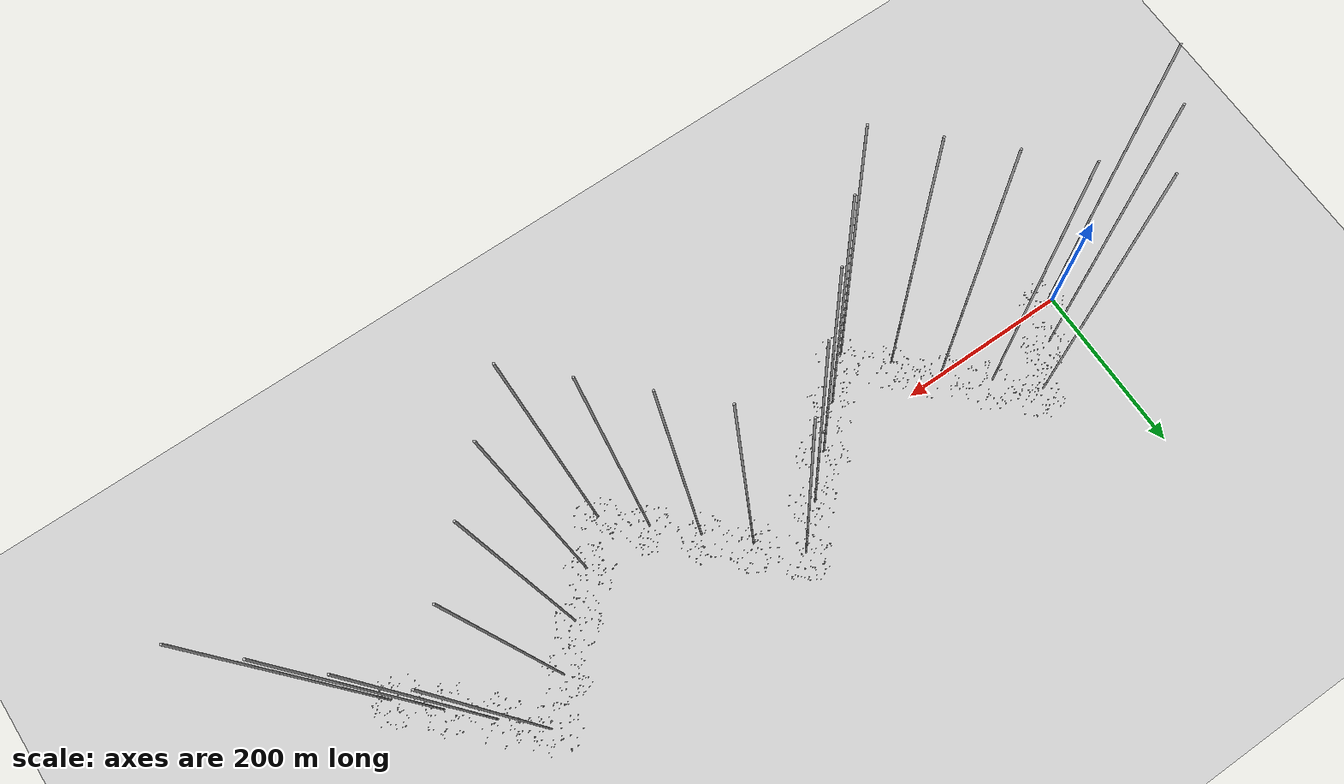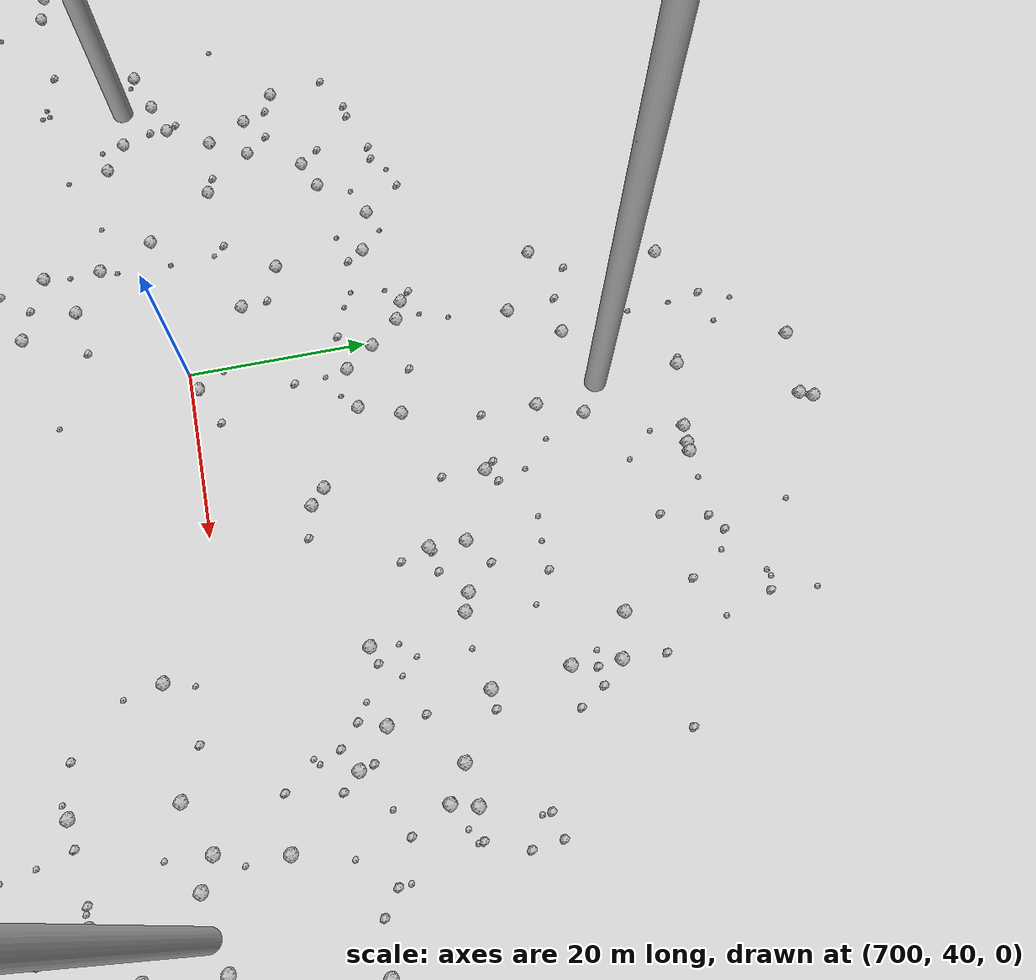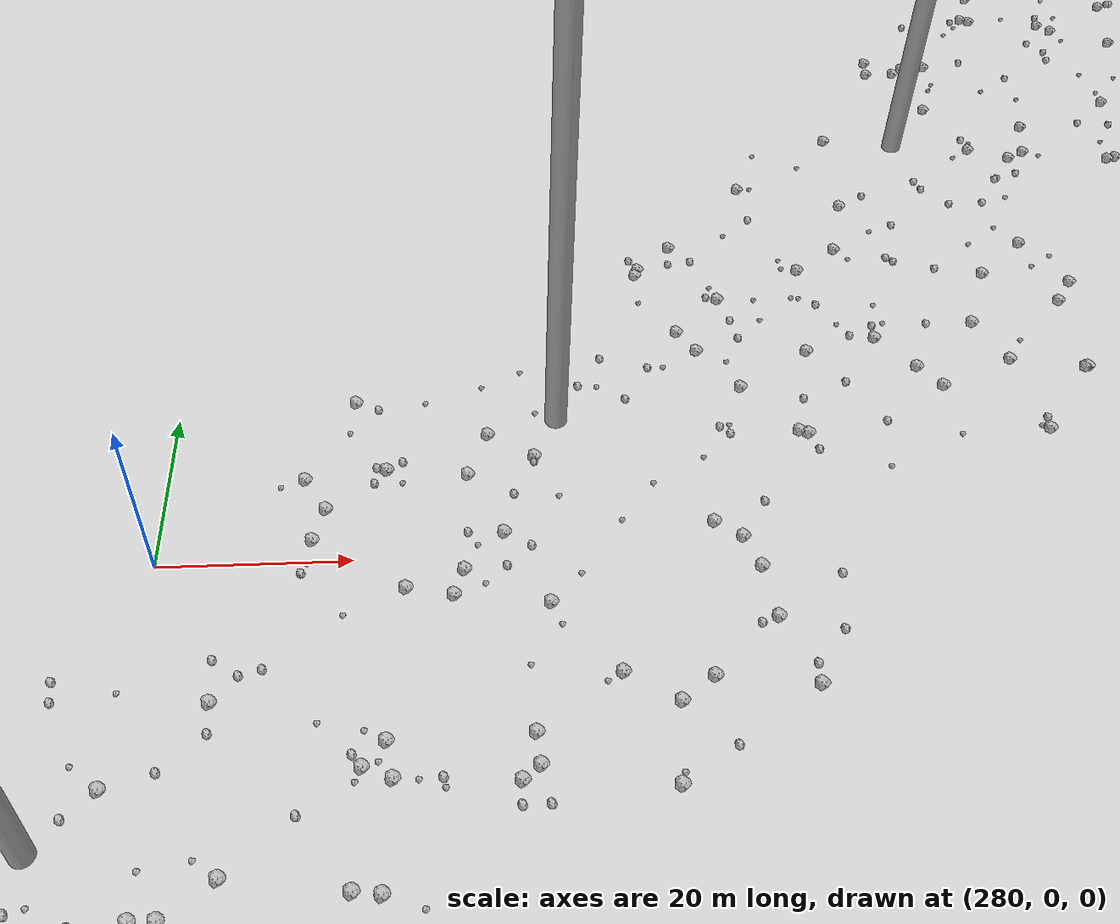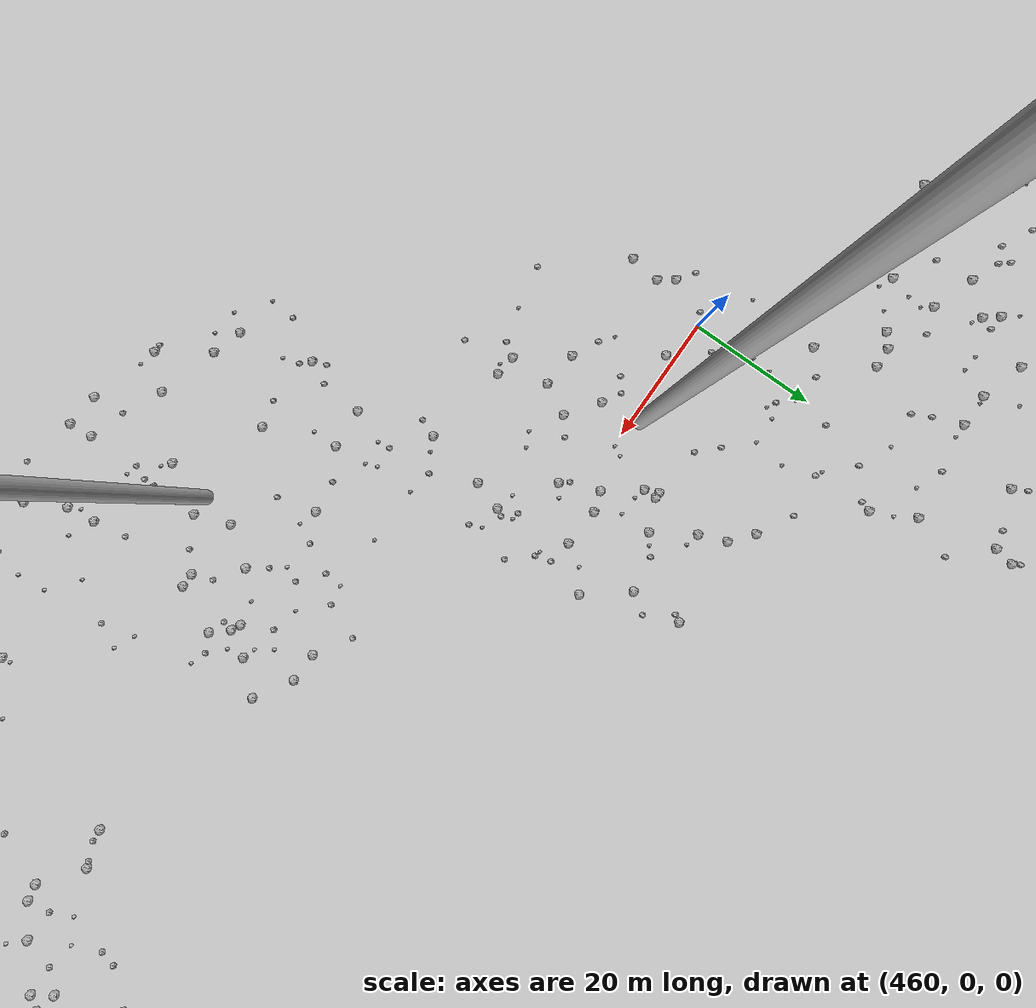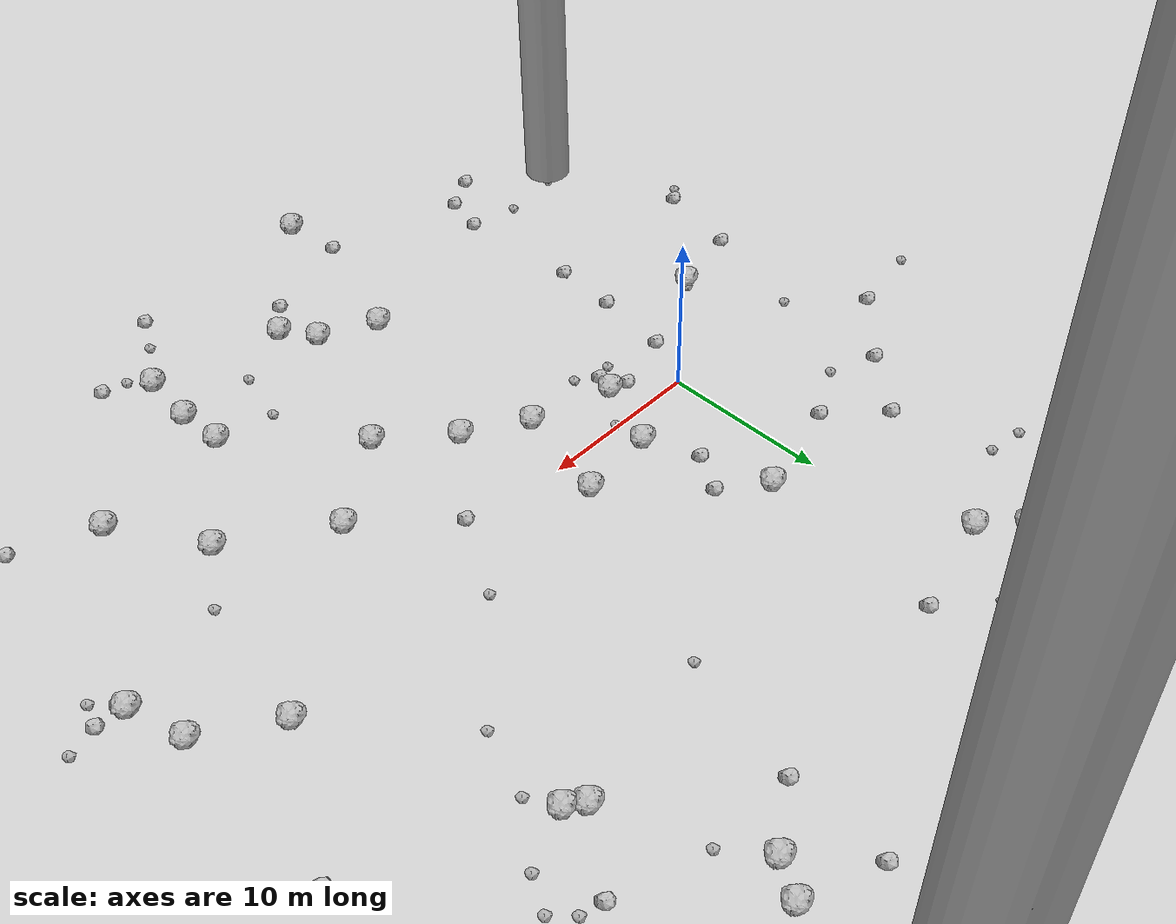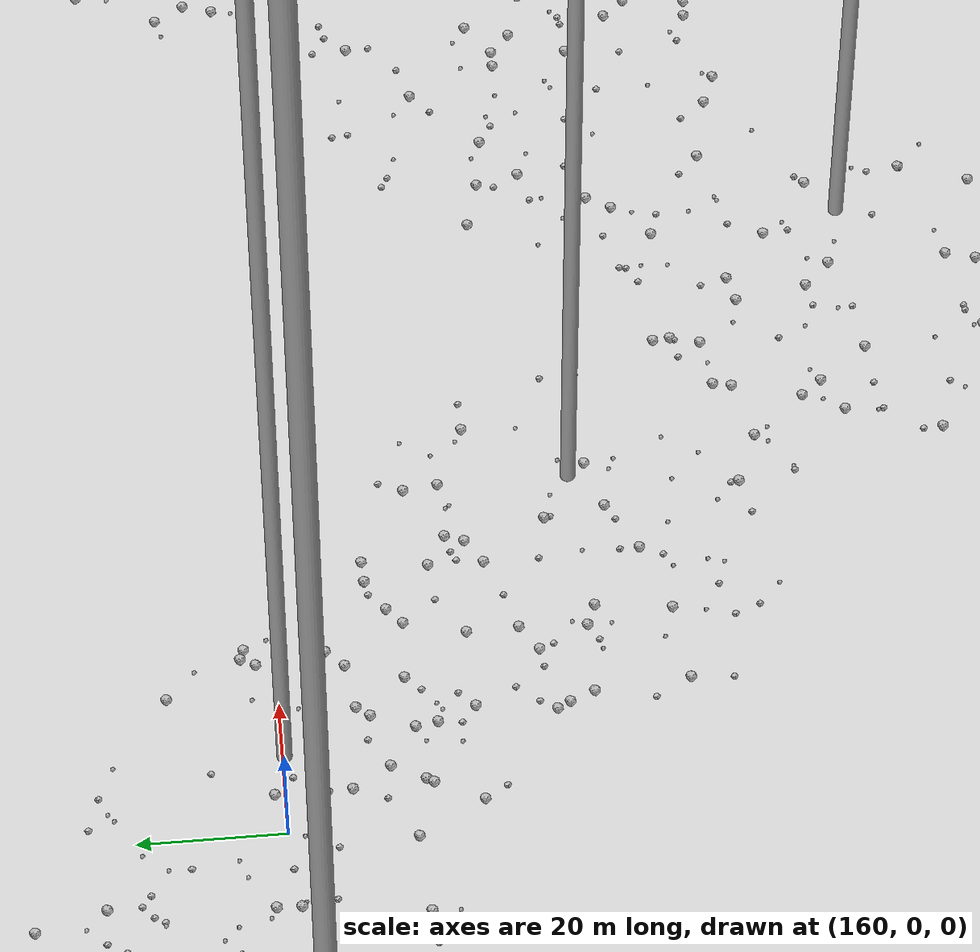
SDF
<sdf version="1.6">
 <world name="default">
  <include><uri>model://custom_ground</uri></include>
  <include><uri>model://sun</uri></include>
  <spherical_coordinates>
   <surface_model>EARTH_WGS84</surface_model>
   <latitude_deg>38.161479</latitude_deg>
   <longitude_deg>-122.454630</longitude_deg>
   <elevation>488.0</elevation>
   <heading_deg>90</heading_deg>
  </spherical_coordinates>
  <model name="rock1_0_0">
   <include><uri>model://rock1</uri><pose>12.210120737058986 -18.466581193428667 0.5 0 0 0</pose></include>
  </model>
  <model name="rock1_0_1">
   <include><uri>model://rock1</uri><pose>13.51467011979259 -20.58209805144698 0.5 0 0 0</pose></include>
  </model>
  <model name="rock1_0_2">
   <include><uri>model://rock1</uri><pose>20.976834868786746 -5.357824327173432 0.5 0 0 0</pose></include>
  </model>
  <model name="rock1_0_3">
   <include><uri>model://rock1</uri><pose>6.374396256742518 -28.488185264887626 0.5 0 0 0</pose></include>
  </model>
  <model name="rock1_0_4">
   <include><uri>model://rock1</uri><pose>26.71174690072492 -9.212716186987468 0.5 0 0 0</pose></include>
  </model>
  <model name="rock1_0_5">
   <include><uri>model://rock1</uri><pose>25.31315330277549 15.417043825029069 0.5 0 0 0</pose></include>
  </model>
  <model name="rock1_0_6">
   <include><uri>model://rock1</uri><pose>3.4534827946943913 -2.348081906730247 0.5 0 0 0</pose></include>
  </model>
  <model name="rock1_0_7">
   <include><uri>model://rock1</uri><pose>-4.152870899165064 21.261191247073384 0.5 0 0 0</pose></include>
  </model>
  <model name="rock1_0_8">
   <include><uri>model://rock1</uri><pose>12.033709989780327 -5.883364822600413 0.5 0 0 0</pose></include>
  </model>
  <model name="rock1_0_9">
   <include><uri>model://rock1</uri><pose>21.736938282522267 -15.692244137602579 0.5 0 0 0</pose></include>
  </model>
  <model name="rock1_0_10">
   <include><uri>model://rock1</uri><pose>35.73615900772557 -3.6536337119357647 0.5 0 0 0</pose></include>
  </model>
  <model name="rock1_0_11">
   <include><uri>model://rock1</uri><pose>9.969265012213558 2.3762110666950065 0.5 0 0 0</pose></include>
  </model>
  <model name="rock1_0_12">
   <include><uri>model://rock1</uri><pose>2.829972278116447 9.390264971898475 0.5 0 0 0</pose></include>
  </model>
  <model name="rock1_0_13">
   <include><uri>model://rock1</uri><pose>8.781611557250809 -16.8828711470224 0.5 0 0 0</pose></include>
  </model>
  <model name="rock1_0_14">
   <include><uri>model://rock1</uri><pose>21.733134406772365 26.09967044643595 0.5 0 0 0</pose></include>
  </model>
  <model name="rock1_0_15">
   <include><uri>model://rock1</uri><pose>20.495723301469347 24.153313202001705 0.5 0 0 0</pose></include>
  </model>
  <model name="rock1_0_16">
   <include><uri>model://rock1</uri><pose>8.44380563563599 -3.7712029076456446 0.5 0 0 0</pose></include>
  </model>
  <model name="rock1_0_17">
   <include><uri>model://rock1</uri><pose>21.871737415834843 -18.6138458616119 0.5 0 0 0</pose></include>
  </model>
  <model name="rock1_0_18">
   <include><uri>model://rock1</uri><pose>30.69914922684844 2.6015854987027893 0.5 0 0 0</pose></include>
  </model>
  <model name="rock1_0_19">
   <include><uri>model://rock1</uri><pose>5.260310927257375 1.9041762050873459 0.5 0 0 0</pose></include>
  </model>
  <model name="rock1_0_20">
   <include><uri>model://rock1</uri><pose>15.780996891880804 -9.215764275393976 0.5 0 0 0</pose></include>
  </model>
  <model name="rock1_0_21">
   <include><uri>model://rock1</uri><pose>-2.0875832033323363 19.243625732345187 0.5 0 0 0</pose></include>
  </model>
  <model name="rock1_0_22">
   <include><uri>model://rock1</uri><pose>-7.2331224198638004 -5.846169200037082 0.5 0 0 0</pose></include>
  </model>
  <model name="rock1_0_23">
   <include><uri>model://rock1</uri><pose>34.82272575136849 -0.15920923674874388 0.5 0 0 0</pose></include>
  </model>
  <model name="rock1_0_24">
   <include><uri>model://rock1</uri><pose>-2.347636350288429 24.12990647884348 0.5 0 0 0</pose></include>
  </model>
  <model name="rock1_0_25">
   <include><uri>model://rock1</uri><pose>21.49164439037949 -22.246047264491928 0.5 0 0 0</pose></include>
  </model>
  <model name="rock1_0_26">
   <include><uri>model://rock1</uri><pose>29.870955154010964 -14.569132193336557 0.5 0 0 0</pose></include>
  </model>
  <model name="rock2_0_0">
   <include><uri>model://rock2</uri><pose>3.0748103188576827 -3.4910692760550077 0.3 0 0 0</pose></include>
  </model>
  <model name="rock2_0_1">
   <include><uri>model://rock2</uri><pose>-13.31053028444079 -12.286566447257051 0.3 0 0 0</pose></include>
  </model>
  <model name="rock2_0_2">
   <include><uri>model://rock2</uri><pose>21.310489338360256 -22.900704936510447 0.3 0 0 0</pose></include>
  </model>
  <model name="rock2_0_3">
   <include><uri>model://rock2</uri><pose>3.946003117438387 5.163685692182874 0.3 0 0 0</pose></include>
  </model>
  <model name="rock2_0_4">
   <include><uri>model://rock2</uri><pose>11.969644833564686 -22.473911159041712 0.3 0 0 0</pose></include>
  </model>
  <model name="rock2_0_5">
   <include><uri>model://rock2</uri><pose>-2.0840303804315 -19.964814406578533 0.3 0 0 0</pose></include>
  </model>
  <model name="rock2_0_6">
   <include><uri>model://rock2</uri><pose>16.214471823967763 -0.8613004986742432 0.3 0 0 0</pose></include>
  </model>
  <model name="rock2_0_7">
   <include><uri>model://rock2</uri><pose>-13.64996568472206 3.631426725542397 0.3 0 0 0</pose></include>
  </model>
  <model name="rock2_0_8">
   <include><uri>model://rock2</uri><pose>-2.2367686055192664 -7.959117385570593 0.3 0 0 0</pose></include>
  </model>
  <model name="rock2_0_9">
   <include><uri>model://rock2</uri><pose>2.2869885962018976 -2.011433069858459 0.3 0 0 0</pose></include>
  </model>
  <model name="rock2_0_10">
   <include><uri>model://rock2</uri><pose>-5.009351243501703 -23.946853909577015 0.3 0 0 0</pose></include>
  </model>
  <model name="rock2_0_11">
   <include><uri>model://rock2</uri><pose>4.102222425538965 20.741619317152157 0.3 0 0 0</pose></include>
  </model>
  <model name="rock2_0_12">
   <include><uri>model://rock2</uri><pose>35.89687202311844 -4.06974831692326 0.3 0 0 0</pose></include>
  </model>
  <model name="rock2_0_13">
   <include><uri>model://rock2</uri><pose>-11.963945608320126 -6.935618145005819 0.3 0 0 0</pose></include>
  </model>
  <model name="rock2_0_14">
   <include><uri>model://rock2</uri><pose>-3.371849882381305 7.872143561426988 0.3 0 0 0</pose></include>
  </model>
  <model name="rock2_0_15">
   <include><uri>model://rock2</uri><pose>-1.5450604663320426 -3.1876797256808302 0.3 0 0 0</pose></include>
  </model>
  <model name="rock2_0_16">
   <include><uri>model://rock2</uri><pose>18.573300054784823 -27.302278877163392 0.3 0 0 0</pose></include>
  </model>
  <model name="rock2_0_17">
   <include><uri>model://rock2</uri><pose>37.394022365852564 -3.8091651058394724 0.3 0 0 0</pose></include>
  </model>
  <model name="rock2_0_18">
   <include><uri>model://rock2</uri><pose>23.981278866925116 -23.730722368636457 0.3 0 0 0</pose></include>
  </model>
  <model name="rock2_0_19">
   <include><uri>model://rock2</uri><pose>-2.776112056968156 -22.586041586109786 0.3 0 0 0</pose></include>
  </model>
  <model name="rock2_0_20">
   <include><uri>model://rock2</uri><pose>-9.599437452681093 7.202485664169373 0.3 0 0 0</pose></include>
  </model>
  <model name="rock2_0_21">
   <include><uri>model://rock2</uri><pose>34.5523769180396 -16.537295114235373 0.3 0 0 0</pose></include>
  </model>
  <model name="rock2_0_22">
   <include><uri>model://rock2</uri><pose>5.9225814935332295 -24.748376374415813 0.3 0 0 0</pose></include>
  </model>
  <model name="rock2_0_23">
   <include><uri>model://rock2</uri><pose>-2.5463423877784663 -12.021655704729067 0.3 0 0 0</pose></include>
  </model>
  <model name="rock2_0_24">
   <include><uri>model://rock2</uri><pose>5.34789658126132 7.423199240184289 0.3 0 0 0</pose></include>
  </model>
  <model name="rock2_0_25">
   <include><uri>model://rock2</uri><pose>16.970154424445163 21.928244841126954 0.3 0 0 0</pose></include>
  </model>
  <model name="rock2_0_26">
   <include><uri>model://rock2</uri><pose>-6.3710953025264985 10.78087395501386 0.3 0 0 0</pose></include>
  </model>
  <model name="rock3_0_0">
   <include><uri>model://rock3</uri><pose>-7.728922917484455 16.72517719239456 0.2 0 0 0</pose></include>
  </model>
  <model name="rock3_0_1">
   <include><uri>model://rock3</uri><pose>-5.20451770374126 -19.42957161972308 0.2 0 0 0</pose></include>
  </model>
  <model name="rock3_0_2">
   <include><uri>model://rock3</uri><pose>4.243135764594221 -4.454921491262226 0.2 0 0 0</pose></include>
  </model>
  <model name="rock3_0_3">
   <include><uri>model://rock3</uri><pose>28.535825018505314 19.67985457256013 0.2 0 0 0</pose></include>
  </model>
  <model name="rock3_0_4">
   <include><uri>model://rock3</uri><pose>22.438560910853674 -23.485219030793747 0.2 0 0 0</pose></include>
  </model>
  <model name="rock3_0_5">
   <include><uri>model://rock3</uri><pose>19.722556362741976 -25.110465455320846 0.2 0 0 0</pose></include>
  </model>
  <model name="rock3_0_6">
   <include><uri>model://rock3</uri><pose>-9.97056866818205 -0.06989695830433007 0.2 0 0 0</pose></include>
  </model>
  <model name="rock3_0_7">
   <include><uri>model://rock3</uri><pose>29.540103991441974 18.57841380575214 0.2 0 0 0</pose></include>
  </model>
  <model name="rock3_0_8">
   <include><uri>model://rock3</uri><pose>29.157827933029054 -5.648855516224021 0.2 0 0 0</pose></include>
  </model>
  <model name="rock3_0_9">
   <include><uri>model://rock3</uri><pose>36.87030567170508 -5.265252002547484 0.2 0 0 0</pose></include>
  </model>
  <model name="rock3_0_10">
   <include><uri>model://rock3</uri><pose>1.2398219174211498 23.22928048810921 0.2 0 0 0</pose></include>
  </model>
  <model name="rock3_0_11">
   <include><uri>model://rock3</uri><pose>24.705129936720482 9.84639841333091 0.2 0 0 0</pose></include>
  </model>
  <model name="rock3_0_12">
   <include><uri>model://rock3</uri><pose>-14.227286408992793 -13.06762583334762 0.2 0 0 0</pose></include>
  </model>
  <model name="rock3_0_13">
   <include><uri>model://rock3</uri><pose>5.292340500827677 -0.10226746059768388 0.2 0 0 0</pose></include>
  </model>
  <model name="rock3_0_14">
   <include><uri>model://rock3</uri><pose>-9.045154011663962 -20.006711568322086 0.2 0 0 0</pose></include>
  </model>
  <model name="rock3_0_15">
   <include><uri>model://rock3</uri><pose>18.20436754831271 -15.066494587396644 0.2 0 0 0</pose></include>
  </model>
  <model name="rock3_0_16">
   <include><uri>model://rock3</uri><pose>14.930366697756263 14.304790066260523 0.2 0 0 0</pose></include>
  </model>
  <model name="rock3_0_17">
   <include><uri>model://rock3</uri><pose>28.503277345635503 16.72886538604844 0.2 0 0 0</pose></include>
  </model>
  <model name="rock3_0_18">
   <include><uri>model://rock3</uri><pose>39.094868054044504 -3.3435214609371755 0.2 0 0 0</pose></include>
  </model>
  <model name="rock3_0_19">
   <include><uri>model://rock3</uri><pose>-6.9800095516571545 -5.472265257897465 0.2 0 0 0</pose></include>
  </model>
  <model name="rock3_0_20">
   <include><uri>model://rock3</uri><pose>-9.977346854077052 17.04823218305173 0.2 0 0 0</pose></include>
  </model>
  <model name="rock3_0_21">
   <include><uri>model://rock3</uri><pose>26.11247525527083 13.665250581961779 0.2 0 0 0</pose></include>
  </model>
  <model name="rock3_0_22">
   <include><uri>model://rock3</uri><pose>1.9931067450294648 -3.87810049085952 0.2 0 0 0</pose></include>
  </model>
  <model name="rock3_0_23">
   <include><uri>model://rock3</uri><pose>18.87958363569176 3.8158633514883746 0.2 0 0 0</pose></include>
  </model>
  <model name="rock3_0_24">
   <include><uri>model://rock3</uri><pose>-18.418988558732316 2.7621392596029324 0.2 0 0 0</pose></include>
  </model>
  <model name="rock3_0_25">
   <include><uri>model://rock3</uri><pose>-6.742945573538863 6.044692190135763 0.2 0 0 0</pose></include>
  </model>
  <model name="rock3_0_26">
   <include><uri>model://rock3</uri><pose>17.33455185651829 -18.516623459738256 0.2 0 0 0</pose></include>
  </model>
  <model name="rock1_1_0">
   <include><uri>model://rock1</uri><pose>21.348054064133553 42.69033790878294 0.5 0 0 0</pose></include>
  </model>
  <model name="rock1_1_1">
   <include><uri>model://rock1</uri><pose>58.574123518884 23.04538532603939 0.5 0 0 0</pose></include>
  </model>
  <model name="rock1_1_2">
   <include><uri>model://rock1</uri><pose>24.339361329997836 16.128828265427035 0.5 0 0 0</pose></include>
  </model>
  <model name="rock1_1_3">
   <include><uri>model://rock1</uri><pose>35.857813335745035 55.98326739831892 0.5 0 0 0</pose></include>
  </model>
  <model name="rock1_1_4">
   <include><uri>model://rock1</uri><pose>51.11551491117006 62.91767408203087 0.5 0 0 0</pose></include>
  </model>
  <model name="rock1_1_5">
   <include><uri>model://rock1</uri><pose>65.86405956339881 39.21649393214839 0.5 0 0 0</pose></include>
  </model>
  <model name="rock1_1_6">
   <include><uri>model://rock1</uri><pose>64.076729990876 44.140422576489634 0.5 0 0 0</pose></include>
  </model>
  <model name="rock1_1_7">
   <include><uri>model://rock1</uri><pose>54.17903635791053 35.9030301162541 0.5 0 0 0</pose></include>
  </model>
  <model name="rock1_1_8">
   <include><uri>model://rock1</uri><pose>33.26516975289138 29.74334882773756 0.5 0 0 0</pose></include>
  </model>
  <model name="rock1_1_9">
   <include><uri>model://rock1</uri><pose>33.559013710321324 16.96395267155848 0.5 0 0 0</pose></include>
  </model>
  <model name="rock1_1_10">
   <include><uri>model://rock1</uri><pose>43.38600914682816 39.978055231910055 0.5 0 0 0</pose></include>
  </model>
  <model name="rock1_1_11">
   <include><uri>model://rock1</uri><pose>55.30618158642549 17.20644319689679 0.5 0 0 0</pose></include>
  </model>
  <model name="rock1_1_12">
   <include><uri>model://rock1</uri><pose>63.16048120650349 49.87674000930536 0.5 0 0 0</pose></include>
  </model>
  <model name="rock1_1_13">
   <include><uri>model://rock1</uri><pose>63.63183174800296 24.342347367274296 0.5 0 0 0</pose></include>
  </model>
  <model name="rock1_1_14">
   <include><uri>model://rock1</uri><pose>56.89851689511102 47.56603262501778 0.5 0 0 0</pose></include>
  </model>
  <model name="rock1_1_15">
   <include><uri>model://rock1</uri><pose>53.43601519498252 54.91743486908511 0.5 0 0 0</pose></include>
  </model>
  <model name="rock1_1_16">
   <include><uri>model://rock1</uri><pose>41.3547001619815 56.2364454384606 0.5 0 0 0</pose></include>
  </model>
  <model name="rock1_1_17">
   <include><uri>model://rock1</uri><pose>58.670865102701754 35.13683075065439 0.5 0 0 0</pose></include>
  </model>
  <model name="rock1_1_18">
   <include><uri>model://rock1</uri><pose>55.34556415967843 62.02724016884742 0.5 0 0 0</pose></include>
  </model>
  <model name="rock1_1_19">
   <include><uri>model://rock1</uri><pose>50.685956076384834 30.563895700029732 0.5 0 0 0</pose></include>
  </model>
  <model name="rock1_1_20">
   <include><uri>model://rock1</uri><pose>33.80016599623299 37.14659208145737 0.5 0 0 0</pose></include>
  </model>
  <model name="rock1_1_21">
   <include><uri>model://rock1</uri><pose>43.163223536768285 51.133602480062976 0.5 0 0 0</pose></include>
  </model>
  <model name="rock1_1_22">
   <include><uri>model://rock1</uri><pose>60.02776720809027 58.85704114102462 0.5 0 0 0</pose></include>
  </model>
  <model name="rock1_1_23">
   <include><uri>model://rock1</uri><pose>52.50697598745189 58.47952822374924 0.5 0 0 0</pose></include>
  </model>
  <model name="rock1_1_24">
   <include><uri>model://rock1</uri><pose>56.66277530985709 27.943596408052965 0.5 0 0 0</pose></include>
  </model>
  <model name="rock1_1_25">
   <include><uri>model://rock1</uri><pose>22.77080957684113 34.03024458161797 0.5 0 0 0</pose></include>
  </model>
  <model name="rock1_1_26">
   <include><uri>model://rock1</uri><pose>50.13522674031593 37.75829800475291 0.5 0 0 0</pose></include>
  </model>
  <model name="rock2_1_0">
   <include><uri>model://rock2</uri><pose>36.54367256380488 53.91395356471626 0.3 0 0 0</pose></include>
  </model>
  <model name="rock2_1_1">
   <include><uri>model://rock2</uri><pose>37.5397930407763 58.80004899875759 0.3 0 0 0</pose></include>
  </model>
  <model name="rock2_1_2">
   <include><uri>model://rock2</uri><pose>60.202336092644636 23.38215180009021 0.3 0 0 0</pose></include>
  </model>
  <model name="rock2_1_3">
   <include><uri>model://rock2</uri><pose>53.42548521780328 33.967112224550135 0.3 0 0 0</pose></include>
  </model>
  <model name="rock2_1_4">
   <include><uri>model://rock2</uri><pose>69.14209532065269 43.48450834216472 0.3 0 0 0</pose></include>
  </model>
  <model name="rock2_1_5">
   <include><uri>model://rock2</uri><pose>35.1448791486922 58.33534472005659 0.3 0 0 0</pose></include>
  </model>
  <model name="rock2_1_6">
   <include><uri>model://rock2</uri><pose>28.96299980968061 22.545657791621288 0.3 0 0 0</pose></include>
  </model>
  <model name="rock2_1_7">
   <include><uri>model://rock2</uri><pose>61.19774297152157 38.60383993330447 0.3 0 0 0</pose></include>
  </model>
  <model name="rock2_1_8">
   <include><uri>model://rock2</uri><pose>27.314195907349173 20.082190941331007 0.3 0 0 0</pose></include>
  </model>
  <model name="rock2_1_9">
   <include><uri>model://rock2</uri><pose>27.484021938843554 53.47781613449582 0.3 0 0 0</pose></include>
  </model>
  <model name="rock2_1_10">
   <include><uri>model://rock2</uri><pose>35.27125232969263 10.613329526915853 0.3 0 0 0</pose></include>
  </model>
  <model name="rock2_1_11">
   <include><uri>model://rock2</uri><pose>17.38762476957348 27.829680281844578 0.3 0 0 0</pose></include>
  </model>
  <model name="rock2_1_12">
   <include><uri>model://rock2</uri><pose>56.9231257774934 54.43840856242451 0.3 0 0 0</pose></include>
  </model>
  <model name="rock2_1_13">
   <include><uri>model://rock2</uri><pose>52.822105373821636 17.575008715097155 0.3 0 0 0</pose></include>
  </model>
  <model name="rock2_1_14">
   <include><uri>model://rock2</uri><pose>63.17402383395787 32.29227316944893 0.3 0 0 0</pose></include>
  </model>
  <model name="rock2_1_15">
   <include><uri>model://rock2</uri><pose>34.586725854715944 58.183680734195164 0.3 0 0 0</pose></include>
  </model>
  <model name="rock2_1_16">
   <include><uri>model://rock2</uri><pose>40.36883669402314 66.80464590272851 0.3 0 0 0</pose></include>
  </model>
  <model name="rock2_1_17">
   <include><uri>model://rock2</uri><pose>30.194209816351513 40.18845346999273 0.3 0 0 0</pose></include>
  </model>
  <model name="rock2_1_18">
   <include><uri>model://rock2</uri><pose>59.151028637670045 60.788004043255526 0.3 0 0 0</pose></include>
  </model>
  <model name="rock2_1_19">
   <include><uri>model://rock2</uri><pose>23.98884253318874 59.46619526999977 0.3 0 0 0</pose></include>
  </model>
  <model name="rock2_1_20">
   <include><uri>model://rock2</uri><pose>24.362830519508 55.584065595804695 0.3 0 0 0</pose></include>
  </model>
  <model name="rock2_1_21">
   <include><uri>model://rock2</uri><pose>40.51204669785021 34.43932736220373 0.3 0 0 0</pose></include>
  </model>
  <model name="rock2_1_22">
   <include><uri>model://rock2</uri><pose>52.46136713476652 43.83700795587172 0.3 0 0 0</pose></include>
  </model>
  <model name="rock2_1_23">
   <include><uri>model://rock2</uri><pose>35.73314904366038 15.605634296492518 0.3 0 0 0</pose></include>
  </model>
  <model name="rock2_1_24">
   <include><uri>model://rock2</uri><pose>37.847987692448015 65.41130474246293 0.3 0 0 0</pose></include>
  </model>
  <model name="rock2_1_25">
   <include><uri>model://rock2</uri><pose>45.110275093895794 29.38746104484836 0.3 0 0 0</pose></include>
  </model>
  <model name="rock2_1_26">
   <include><uri>model://rock2</uri><pose>54.045509581975445 41.7025212228899 0.3 0 0 0</pose></include>
  </model>
  <model name="rock3_1_0">
   <include><uri>model://rock3</uri><pose>40.61602282378868 61.05973500113462 0.2 0 0 0</pose></include>
  </model>
  <model name="rock3_1_1">
   <include><uri>model://rock3</uri><pose>14.491007605678165 50.94472089974043 0.2 0 0 0</pose></include>
  </model>
  <model name="rock3_1_2">
   <include><uri>model://rock3</uri><pose>28.420806958544816 60.043408624617705 0.2 0 0 0</pose></include>
  </model>
  <model name="rock3_1_3">
   <include><uri>model://rock3</uri><pose>31.028373682930674 50.105884092020055 0.2 0 0 0</pose></include>
  </model>
  <model name="rock3_1_4">
   <include><uri>model://rock3</uri><pose>15.757584567687301 49.549251407778954 0.2 0 0 0</pose></include>
  </model>
  <model name="rock3_1_5">
   <include><uri>model://rock3</uri><pose>59.10057443166489 28.117739894899646 0.2 0 0 0</pose></include>
  </model>
  <model name="rock3_1_6">
   <include><uri>model://rock3</uri><pose>47.6442646242551 67.24622186765535 0.2 0 0 0</pose></include>
  </model>
  <model name="rock3_1_7">
   <include><uri>model://rock3</uri><pose>30.291831920064926 62.816147069911025 0.2 0 0 0</pose></include>
  </model>
  <model name="rock3_1_8">
   <include><uri>model://rock3</uri><pose>36.492420503639714 69.2589202645332 0.2 0 0 0</pose></include>
  </model>
  <model name="rock3_1_9">
   <include><uri>model://rock3</uri><pose>36.60848668719568 56.770699477978084 0.2 0 0 0</pose></include>
  </model>
  <model name="rock3_1_10">
   <include><uri>model://rock3</uri><pose>51.50257696628348 20.682001103930464 0.2 0 0 0</pose></include>
  </model>
  <model name="rock3_1_11">
   <include><uri>model://rock3</uri><pose>21.22280670075151 38.18490554608141 0.2 0 0 0</pose></include>
  </model>
  <model name="rock3_1_12">
   <include><uri>model://rock3</uri><pose>53.2011384146793 59.538882429824724 0.2 0 0 0</pose></include>
  </model>
  <model name="rock3_1_13">
   <include><uri>model://rock3</uri><pose>43.26289545996234 21.002013312135922 0.2 0 0 0</pose></include>
  </model>
  <model name="rock3_1_14">
   <include><uri>model://rock3</uri><pose>44.235142797254795 63.8717659424716 0.2 0 0 0</pose></include>
  </model>
  <model name="rock3_1_15">
   <include><uri>model://rock3</uri><pose>31.600186873931207 54.68807713675728 0.2 0 0 0</pose></include>
  </model>
  <model name="rock3_1_16">
   <include><uri>model://rock3</uri><pose>41.38670711601503 24.106448620131022 0.2 0 0 0</pose></include>
  </model>
  <model name="rock3_1_17">
   <include><uri>model://rock3</uri><pose>51.532005026328534 55.9282009800481 0.2 0 0 0</pose></include>
  </model>
  <model name="rock3_1_18">
   <include><uri>model://rock3</uri><pose>22.96931070176481 44.49437672020253 0.2 0 0 0</pose></include>
  </model>
  <model name="rock3_1_19">
   <include><uri>model://rock3</uri><pose>29.636977248746813 48.455545345465424 0.2 0 0 0</pose></include>
  </model>
  <model name="rock3_1_20">
   <include><uri>model://rock3</uri><pose>22.14133686118292 21.750218077366156 0.2 0 0 0</pose></include>
  </model>
  <model name="rock3_1_21">
   <include><uri>model://rock3</uri><pose>53.09050501376517 24.075090552342395 0.2 0 0 0</pose></include>
  </model>
  <model name="rock3_1_22">
   <include><uri>model://rock3</uri><pose>58.310336156673856 39.34174094563525 0.2 0 0 0</pose></include>
  </model>
  <model name="rock3_1_23">
   <include><uri>model://rock3</uri><pose>57.29643675567111 43.46248205820638 0.2 0 0 0</pose></include>
  </model>
  <model name="rock3_1_24">
   <include><uri>model://rock3</uri><pose>50.617944331079116 14.797166836063628 0.2 0 0 0</pose></include>
  </model>
  <model name="rock3_1_25">
   <include><uri>model://rock3</uri><pose>14.625889939879698 40.660913915121455 0.2 0 0 0</pose></include>
  </model>
  <model name="rock3_1_26">
   <include><uri>model://rock3</uri><pose>62.54817002511145 34.574932093113915 0.2 0 0 0</pose></include>
  </model>
  <model name="rock1_2_0">
   <include><uri>model://rock1</uri><pose>72.65408858627652 59.30060809755058 0.5 0 0 0</pose></include>
  </model>
  <model name="rock1_2_1">
   <include><uri>model://rock1</uri><pose>88.6426019824559 72.44566780062055 0.5 0 0 0</pose></include>
  </model>
  <model name="rock1_2_2">
   <include><uri>model://rock1</uri><pose>76.60334237404035 90.79104383281384 0.5 0 0 0</pose></include>
  </model>
  <model name="rock1_2_3">
   <include><uri>model://rock1</uri><pose>86.40983798113587 108.37599885889014 0.5 0 0 0</pose></include>
  </model>
  <model name="rock1_2_4">
   <include><uri>model://rock1</uri><pose>79.68310504995162 96.93531920872383 0.5 0 0 0</pose></include>
  </model>
  <model name="rock1_2_5">
   <include><uri>model://rock1</uri><pose>64.85528983821976 57.625557501733795 0.5 0 0 0</pose></include>
  </model>
  <model name="rock1_2_6">
   <include><uri>model://rock1</uri><pose>103.40614881550238 62.85231756921684 0.5 0 0 0</pose></include>
  </model>
  <model name="rock1_2_7">
   <include><uri>model://rock1</uri><pose>98.75040279410496 67.66040326268073 0.5 0 0 0</pose></include>
  </model>
  <model name="rock1_2_8">
   <include><uri>model://rock1</uri><pose>108.2449348809688 89.55041294134524 0.5 0 0 0</pose></include>
  </model>
  <model name="rock1_2_9">
   <include><uri>model://rock1</uri><pose>60.17299932617845 88.01553860748959 0.5 0 0 0</pose></include>
  </model>
  <model name="rock1_2_10">
   <include><uri>model://rock1</uri><pose>93.97123075424905 82.06575307763262 0.5 0 0 0</pose></include>
  </model>
  <model name="rock1_2_11">
   <include><uri>model://rock1</uri><pose>70.01010380210192 104.67908280553124 0.5 0 0 0</pose></include>
  </model>
  <model name="rock1_2_12">
   <include><uri>model://rock1</uri><pose>88.95665963451893 54.62648679933543 0.5 0 0 0</pose></include>
  </model>
  <model name="rock1_2_13">
   <include><uri>model://rock1</uri><pose>83.06523025991693 94.52504686363889 0.5 0 0 0</pose></include>
  </model>
  <model name="rock1_2_14">
   <include><uri>model://rock1</uri><pose>72.67076649020024 69.94719749978867 0.5 0 0 0</pose></include>
  </model>
  <model name="rock1_2_15">
   <include><uri>model://rock1</uri><pose>78.50038709693713 74.50722785134985 0.5 0 0 0</pose></include>
  </model>
  <model name="rock1_2_16">
   <include><uri>model://rock1</uri><pose>64.87137629155737 56.185862848314365 0.5 0 0 0</pose></include>
  </model>
  <model name="rock1_2_17">
   <include><uri>model://rock1</uri><pose>88.37527142829012 69.58594914924568 0.5 0 0 0</pose></include>
  </model>
  <model name="rock1_2_18">
   <include><uri>model://rock1</uri><pose>83.98597889959883 99.88919507479503 0.5 0 0 0</pose></include>
  </model>
  <model name="rock1_2_19">
   <include><uri>model://rock1</uri><pose>84.17657137822314 79.13788701686389 0.5 0 0 0</pose></include>
  </model>
  <model name="rock1_2_20">
   <include><uri>model://rock1</uri><pose>103.53841308338528 70.91834602162146 0.5 0 0 0</pose></include>
  </model>
  <model name="rock1_2_21">
   <include><uri>model://rock1</uri><pose>101.29629701309341 63.55385803683559 0.5 0 0 0</pose></include>
  </model>
  <model name="rock1_2_22">
   <include><uri>model://rock1</uri><pose>79.95041537304479 82.58306367334454 0.5 0 0 0</pose></include>
  </model>
  <model name="rock1_2_23">
   <include><uri>model://rock1</uri><pose>98.68132275898245 99.31960414291134 0.5 0 0 0</pose></include>
  </model>
  <model name="rock1_2_24">
   <include><uri>model://rock1</uri><pose>70.17490480742623 92.57048344683989 0.5 0 0 0</pose></include>
  </model>
  <model name="rock1_2_25">
   <include><uri>model://rock1</uri><pose>57.64367637231439 81.60510805189384 0.5 0 0 0</pose></include>
  </model>
  <model name="rock1_2_26">
   <include><uri>model://rock1</uri><pose>88.9285496189018 61.2633588524517 0.5 0 0 0</pose></include>
  </model>
  <model name="rock2_2_0">
   <include><uri>model://rock2</uri><pose>65.26772065952994 69.38757655969272 0.3 0 0 0</pose></include>
  </model>
  <model name="rock2_2_1">
   <include><uri>model://rock2</uri><pose>74.4247872788363 98.24474689403189 0.3 0 0 0</pose></include>
  </model>
  <model name="rock2_2_2">
   <include><uri>model://rock2</uri><pose>92.78653417049928 64.89065124065863 0.3 0 0 0</pose></include>
  </model>
  <model name="rock2_2_3">
   <include><uri>model://rock2</uri><pose>70.85803572535139 105.46821689519578 0.3 0 0 0</pose></include>
  </model>
  <model name="rock2_2_4">
   <include><uri>model://rock2</uri><pose>86.11296359681174 98.78415880740097 0.3 0 0 0</pose></include>
  </model>
  <model name="rock2_2_5">
   <include><uri>model://rock2</uri><pose>69.24664351239844 94.0559854081776 0.3 0 0 0</pose></include>
  </model>
  <model name="rock2_2_6">
   <include><uri>model://rock2</uri><pose>76.31691991208308 70.73188617661515 0.3 0 0 0</pose></include>
  </model>
  <model name="rock2_2_7">
   <include><uri>model://rock2</uri><pose>64.95755429872474 104.55728676276487 0.3 0 0 0</pose></include>
  </model>
  <model name="rock2_2_8">
   <include><uri>model://rock2</uri><pose>65.63659485616058 82.93994024808418 0.3 0 0 0</pose></include>
  </model>
  <model name="rock2_2_9">
   <include><uri>model://rock2</uri><pose>87.35896321169912 95.08518582325044 0.3 0 0 0</pose></include>
  </model>
  <model name="rock2_2_10">
   <include><uri>model://rock2</uri><pose>69.98359406011815 73.76303144433712 0.3 0 0 0</pose></include>
  </model>
  <model name="rock2_2_11">
   <include><uri>model://rock2</uri><pose>91.62342909502073 75.8667850163382 0.3 0 0 0</pose></include>
  </model>
  <model name="rock2_2_12">
   <include><uri>model://rock2</uri><pose>84.6652969245303 72.01807952842213 0.3 0 0 0</pose></include>
  </model>
  <model name="rock2_2_13">
   <include><uri>model://rock2</uri><pose>80.83948275932003 56.50806152678854 0.3 0 0 0</pose></include>
  </model>
  <model name="rock2_2_14">
   <include><uri>model://rock2</uri><pose>77.93974947094391 56.093256881575286 0.3 0 0 0</pose></include>
  </model>
  <model name="rock2_2_15">
   <include><uri>model://rock2</uri><pose>63.4734083275002 61.93231305947734 0.3 0 0 0</pose></include>
  </model>
  <model name="rock2_2_16">
   <include><uri>model://rock2</uri><pose>58.65816668810524 59.29361453264924 0.3 0 0 0</pose></include>
  </model>
  <model name="rock2_2_17">
   <include><uri>model://rock2</uri><pose>80.95399451338551 54.12772434747668 0.3 0 0 0</pose></include>
  </model>
  <model name="rock2_2_18">
   <include><uri>model://rock2</uri><pose>89.38317423316508 82.01481044994208 0.3 0 0 0</pose></include>
  </model>
  <model name="rock2_2_19">
   <include><uri>model://rock2</uri><pose>95.36107558912306 77.41400022783776 0.3 0 0 0</pose></include>
  </model>
  <model name="rock2_2_20">
   <include><uri>model://rock2</uri><pose>101.31770724270265 96.40714568017148 0.3 0 0 0</pose></include>
  </model>
  <model name="rock2_2_21">
   <include><uri>model://rock2</uri><pose>79.43940609603797 72.40223993545811 0.3 0 0 0</pose></include>
  </model>
  <model name="rock2_2_22">
   <include><uri>model://rock2</uri><pose>91.06567667642432 100.52420057621532 0.3 0 0 0</pose></include>
  </model>
  <model name="rock2_2_23">
   <include><uri>model://rock2</uri><pose>69.45995312918623 62.73844248516468 0.3 0 0 0</pose></include>
  </model>
  <model name="rock2_2_24">
   <include><uri>model://rock2</uri><pose>68.86452405148965 98.51026335546405 0.3 0 0 0</pose></include>
  </model>
  <model name="rock2_2_25">
   <include><uri>model://rock2</uri><pose>51.629396608889216 72.30004444567356 0.3 0 0 0</pose></include>
  </model>
  <model name="rock2_2_26">
   <include><uri>model://rock2</uri><pose>88.05964544920838 102.94606953861097 0.3 0 0 0</pose></include>
  </model>
  <model name="rock3_2_0">
   <include><uri>model://rock3</uri><pose>64.21895520311993 89.86094401124996 0.2 0 0 0</pose></include>
  </model>
  <model name="rock3_2_1">
   <include><uri>model://rock3</uri><pose>106.95055182577599 84.6676633565378 0.2 0 0 0</pose></include>
  </model>
  <model name="rock3_2_2">
   <include><uri>model://rock3</uri><pose>104.79979813420783 80.94128251417341 0.2 0 0 0</pose></include>
  </model>
  <model name="rock3_2_3">
   <include><uri>model://rock3</uri><pose>85.62884647427528 92.25600107098981 0.2 0 0 0</pose></include>
  </model>
  <model name="rock3_2_4">
   <include><uri>model://rock3</uri><pose>80.53150523124573 67.107146637581 0.2 0 0 0</pose></include>
  </model>
  <model name="rock3_2_5">
   <include><uri>model://rock3</uri><pose>106.27088156931576 73.21936774208389 0.2 0 0 0</pose></include>
  </model>
  <model name="rock3_2_6">
   <include><uri>model://rock3</uri><pose>83.71752112993917 107.77358914541584 0.2 0 0 0</pose></include>
  </model>
  <model name="rock3_2_7">
   <include><uri>model://rock3</uri><pose>81.27828690787837 103.01658098618837 0.2 0 0 0</pose></include>
  </model>
  <model name="rock3_2_8">
   <include><uri>model://rock3</uri><pose>86.25212222525954 62.40262074702488 0.2 0 0 0</pose></include>
  </model>
  <model name="rock3_2_9">
   <include><uri>model://rock3</uri><pose>96.51207217594305 77.19335852310058 0.2 0 0 0</pose></include>
  </model>
  <model name="rock3_2_10">
   <include><uri>model://rock3</uri><pose>94.17668674736328 66.12841772820742 0.2 0 0 0</pose></include>
  </model>
  <model name="rock3_2_11">
   <include><uri>model://rock3</uri><pose>98.78642370702383 69.15156106913325 0.2 0 0 0</pose></include>
  </model>
  <model name="rock3_2_12">
   <include><uri>model://rock3</uri><pose>51.091095513031036 78.77836579790909 0.2 0 0 0</pose></include>
  </model>
  <model name="rock3_2_13">
   <include><uri>model://rock3</uri><pose>62.940712869232165 98.15295576490485 0.2 0 0 0</pose></include>
  </model>
  <model name="rock3_2_14">
   <include><uri>model://rock3</uri><pose>79.3616393234479 76.57524596505138 0.2 0 0 0</pose></include>
  </model>
  <model name="rock3_2_15">
   <include><uri>model://rock3</uri><pose>101.27405694583588 67.05840780765756 0.2 0 0 0</pose></include>
  </model>
  <model name="rock3_2_16">
   <include><uri>model://rock3</uri><pose>98.28350683965675 97.51212057305915 0.2 0 0 0</pose></include>
  </model>
  <model name="rock3_2_17">
   <include><uri>model://rock3</uri><pose>60.74044311175809 66.7350719370824 0.2 0 0 0</pose></include>
  </model>
  <model name="rock3_2_18">
   <include><uri>model://rock3</uri><pose>66.87655052466849 95.58947456342077 0.2 0 0 0</pose></include>
  </model>
  <model name="rock3_2_19">
   <include><uri>model://rock3</uri><pose>83.33617411713583 75.21671887240824 0.2 0 0 0</pose></include>
  </model>
  <model name="rock3_2_20">
   <include><uri>model://rock3</uri><pose>84.248442236431 102.27814493951473 0.2 0 0 0</pose></include>
  </model>
  <model name="rock3_2_21">
   <include><uri>model://rock3</uri><pose>93.2096147420003 57.45793574501312 0.2 0 0 0</pose></include>
  </model>
  <model name="rock3_2_22">
   <include><uri>model://rock3</uri><pose>87.112351706143 68.44814447138083 0.2 0 0 0</pose></include>
  </model>
  <model name="rock3_2_23">
   <include><uri>model://rock3</uri><pose>61.0748656567699 100.59015077867228 0.2 0 0 0</pose></include>
  </model>
  <model name="rock3_2_24">
   <include><uri>model://rock3</uri><pose>56.272926905239544 74.40601366709163 0.2 0 0 0</pose></include>
  </model>
  <model name="rock3_2_25">
   <include><uri>model://rock3</uri><pose>82.66092377779982 53.0035108257959 0.2 0 0 0</pose></include>
  </model>
  <model name="rock3_2_26">
   <include><uri>model://rock3</uri><pose>60.91634484573514 98.10141220566334 0.2 0 0 0</pose></include>
  </model>
  <model name="rock1_3_0">
   <include><uri>model://rock1</uri><pose>107.75223369272591 15.588626987574656 0.5 0 0 0</pose></include>
  </model>
  <model name="rock1_3_1">
   <include><uri>model://rock1</uri><pose>127.58069274486421 11.148357423464052 0.5 0 0 0</pose></include>
  </model>
  <model name="rock1_3_2">
   <include><uri>model://rock1</uri><pose>142.68643333799082 48.06331853232834 0.5 0 0 0</pose></include>
  </model>
  <model name="rock1_3_3">
   <include><uri>model://rock1</uri><pose>103.8926687023299 16.861638627060657 0.5 0 0 0</pose></include>
  </model>
  <model name="rock1_3_4">
   <include><uri>model://rock1</uri><pose>137.98791775374136 32.20220607062018 0.5 0 0 0</pose></include>
  </model>
  <model name="rock1_3_5">
   <include><uri>model://rock1</uri><pose>126.86639776474465 68.29225878362351 0.5 0 0 0</pose></include>
  </model>
  <model name="rock1_3_6">
   <include><uri>model://rock1</uri><pose>101.71687386203703 44.61598726602807 0.5 0 0 0</pose></include>
  </model>
  <model name="rock1_3_7">
   <include><uri>model://rock1</uri><pose>118.98928908957669 62.21270579326931 0.5 0 0 0</pose></include>
  </model>
  <model name="rock1_3_8">
   <include><uri>model://rock1</uri><pose>123.76952520291357 43.534773975785505 0.5 0 0 0</pose></include>
  </model>
  <model name="rock1_3_9">
   <include><uri>model://rock1</uri><pose>129.98068374591966 33.82156503314016 0.5 0 0 0</pose></include>
  </model>
  <model name="rock1_3_10">
   <include><uri>model://rock1</uri><pose>128.0740664669394 34.02357800034129 0.5 0 0 0</pose></include>
  </model>
  <model name="rock1_3_11">
   <include><uri>model://rock1</uri><pose>147.70111878724958 33.70024643537179 0.5 0 0 0</pose></include>
  </model>
  <model name="rock1_3_12">
   <include><uri>model://rock1</uri><pose>121.81127483407712 17.83296239419264 0.5 0 0 0</pose></include>
  </model>
  <model name="rock1_3_13">
   <include><uri>model://rock1</uri><pose>133.54832955649383 50.92491685771196 0.5 0 0 0</pose></include>
  </model>
  <model name="rock1_3_14">
   <include><uri>model://rock1</uri><pose>140.4955629423481 30.06736081103117 0.5 0 0 0</pose></include>
  </model>
  <model name="rock1_3_15">
   <include><uri>model://rock1</uri><pose>96.95275854556981 41.07898703394737 0.5 0 0 0</pose></include>
  </model>
  <model name="rock1_3_16">
   <include><uri>model://rock1</uri><pose>118.13037540451158 67.58265375126173 0.5 0 0 0</pose></include>
  </model>
  <model name="rock1_3_17">
   <include><uri>model://rock1</uri><pose>111.2002734522843 67.7633528990186 0.5 0 0 0</pose></include>
  </model>
  <model name="rock1_3_18">
   <include><uri>model://rock1</uri><pose>126.51021949700207 49.90986017168123 0.5 0 0 0</pose></include>
  </model>
  <model name="rock1_3_19">
   <include><uri>model://rock1</uri><pose>137.27318936516775 24.78296960940267 0.5 0 0 0</pose></include>
  </model>
  <model name="rock1_3_20">
   <include><uri>model://rock1</uri><pose>130.76761668799227 49.668283301527495 0.5 0 0 0</pose></include>
  </model>
  <model name="rock1_3_21">
   <include><uri>model://rock1</uri><pose>125.7484922688989 54.72159490794959 0.5 0 0 0</pose></include>
  </model>
  <model name="rock1_3_22">
   <include><uri>model://rock1</uri><pose>144.70543120681043 56.457003010215146 0.5 0 0 0</pose></include>
  </model>
  <model name="rock1_3_23">
   <include><uri>model://rock1</uri><pose>126.12988427261698 61.85313357524484 0.5 0 0 0</pose></include>
  </model>
  <model name="rock1_3_24">
   <include><uri>model://rock1</uri><pose>100.61502648450193 55.95465688033528 0.5 0 0 0</pose></include>
  </model>
  <model name="rock1_3_25">
   <include><uri>model://rock1</uri><pose>124.63534526908506 15.692640180458504 0.5 0 0 0</pose></include>
  </model>
  <model name="rock1_3_26">
   <include><uri>model://rock1</uri><pose>127.04451341238544 47.64703370224514 0.5 0 0 0</pose></include>
  </model>
  <model name="rock2_3_0">
   <include><uri>model://rock2</uri><pose>117.49852468528078 64.62828178374639 0.3 0 0 0</pose></include>
  </model>
  <model name="rock2_3_1">
   <include><uri>model://rock2</uri><pose>140.09896014500367 57.73263470969359 0.3 0 0 0</pose></include>
  </model>
  <model name="rock2_3_2">
   <include><uri>model://rock2</uri><pose>109.63378698606475 19.040994431392228 0.3 0 0 0</pose></include>
  </model>
  <model name="rock2_3_3">
   <include><uri>model://rock2</uri><pose>103.33852184096321 18.704177877982996 0.3 0 0 0</pose></include>
  </model>
  <model name="rock2_3_4">
   <include><uri>model://rock2</uri><pose>120.0289411193551 31.0426965280556 0.3 0 0 0</pose></include>
  </model>
  <model name="rock2_3_5">
   <include><uri>model://rock2</uri><pose>124.95976210376648 17.180149076748123 0.3 0 0 0</pose></include>
  </model>
  <model name="rock2_3_6">
   <include><uri>model://rock2</uri><pose>115.469425192961 29.403998499078295 0.3 0 0 0</pose></include>
  </model>
  <model name="rock2_3_7">
   <include><uri>model://rock2</uri><pose>111.66426430722083 36.028890035318526 0.3 0 0 0</pose></include>
  </model>
  <model name="rock2_3_8">
   <include><uri>model://rock2</uri><pose>95.21079099427182 44.69836723223346 0.3 0 0 0</pose></include>
  </model>
  <model name="rock2_3_9">
   <include><uri>model://rock2</uri><pose>111.76461455250526 57.80928450044491 0.3 0 0 0</pose></include>
  </model>
  <model name="rock2_3_10">
   <include><uri>model://rock2</uri><pose>143.25587717140553 28.549992644414914 0.3 0 0 0</pose></include>
  </model>
  <model name="rock2_3_11">
   <include><uri>model://rock2</uri><pose>141.8448386545378 48.00283625734776 0.3 0 0 0</pose></include>
  </model>
  <model name="rock2_3_12">
   <include><uri>model://rock2</uri><pose>122.25357270088602 59.69011193218056 0.3 0 0 0</pose></include>
  </model>
  <model name="rock2_3_13">
   <include><uri>model://rock2</uri><pose>109.26410628544808 22.820087216450403 0.3 0 0 0</pose></include>
  </model>
  <model name="rock2_3_14">
   <include><uri>model://rock2</uri><pose>145.33125870186916 24.441327854278363 0.3 0 0 0</pose></include>
  </model>
  <model name="rock2_3_15">
   <include><uri>model://rock2</uri><pose>99.88404064094009 32.69393865654797 0.3 0 0 0</pose></include>
  </model>
  <model name="rock2_3_16">
   <include><uri>model://rock2</uri><pose>116.08202129899229 40.46784558918969 0.3 0 0 0</pose></include>
  </model>
  <model name="rock2_3_17">
   <include><uri>model://rock2</uri><pose>118.72005016849313 15.62025689389701 0.3 0 0 0</pose></include>
  </model>
  <model name="rock2_3_18">
   <include><uri>model://rock2</uri><pose>117.1669694370176 58.80057473749625 0.3 0 0 0</pose></include>
  </model>
  <model name="rock2_3_19">
   <include><uri>model://rock2</uri><pose>135.16368373940043 19.73741933089471 0.3 0 0 0</pose></include>
  </model>
  <model name="rock2_3_20">
   <include><uri>model://rock2</uri><pose>124.40371791910988 12.169814998315442 0.3 0 0 0</pose></include>
  </model>
  <model name="rock2_3_21">
   <include><uri>model://rock2</uri><pose>104.712153547226 55.27528885067888 0.3 0 0 0</pose></include>
  </model>
  <model name="rock2_3_22">
   <include><uri>model://rock2</uri><pose>117.2138465218659 31.498980026161234 0.3 0 0 0</pose></include>
  </model>
  <model name="rock2_3_23">
   <include><uri>model://rock2</uri><pose>114.59840740868093 26.339353888076 0.3 0 0 0</pose></include>
  </model>
  <model name="rock2_3_24">
   <include><uri>model://rock2</uri><pose>141.132987763132 48.721478544267704 0.3 0 0 0</pose></include>
  </model>
  <model name="rock2_3_25">
   <include><uri>model://rock2</uri><pose>112.63702267405671 20.857916889556662 0.3 0 0 0</pose></include>
  </model>
  <model name="rock2_3_26">
   <include><uri>model://rock2</uri><pose>128.42144365673033 33.51400820649184 0.3 0 0 0</pose></include>
  </model>
  <model name="rock3_3_0">
   <include><uri>model://rock3</uri><pose>119.38429394769426 29.690794445741528 0.2 0 0 0</pose></include>
  </model>
  <model name="rock3_3_1">
   <include><uri>model://rock3</uri><pose>121.48357600337339 16.34263719857904 0.2 0 0 0</pose></include>
  </model>
  <model name="rock3_3_2">
   <include><uri>model://rock3</uri><pose>123.63192440673635 32.11642103649908 0.2 0 0 0</pose></include>
  </model>
  <model name="rock3_3_3">
   <include><uri>model://rock3</uri><pose>126.28553984511463 30.31212579267455 0.2 0 0 0</pose></include>
  </model>
  <model name="rock3_3_4">
   <include><uri>model://rock3</uri><pose>117.13499282527256 43.63187738683001 0.2 0 0 0</pose></include>
  </model>
  <model name="rock3_3_5">
   <include><uri>model://rock3</uri><pose>95.16712844506132 51.182345070162974 0.2 0 0 0</pose></include>
  </model>
  <model name="rock3_3_6">
   <include><uri>model://rock3</uri><pose>122.88577900234418 22.482687638547965 0.2 0 0 0</pose></include>
  </model>
  <model name="rock3_3_7">
   <include><uri>model://rock3</uri><pose>98.77795001548259 28.869289255839632 0.2 0 0 0</pose></include>
  </model>
  <model name="rock3_3_8">
   <include><uri>model://rock3</uri><pose>116.51360061544264 59.89250427024273 0.2 0 0 0</pose></include>
  </model>
  <model name="rock3_3_9">
   <include><uri>model://rock3</uri><pose>106.73595472735695 20.728698902923938 0.2 0 0 0</pose></include>
  </model>
  <model name="rock3_3_10">
   <include><uri>model://rock3</uri><pose>113.575018888177 13.727937456111167 0.2 0 0 0</pose></include>
  </model>
  <model name="rock3_3_11">
   <include><uri>model://rock3</uri><pose>98.27041005605108 27.980830670295532 0.2 0 0 0</pose></include>
  </model>
  <model name="rock3_3_12">
   <include><uri>model://rock3</uri><pose>118.93249379423636 59.102666357135256 0.2 0 0 0</pose></include>
  </model>
  <model name="rock3_3_13">
   <include><uri>model://rock3</uri><pose>136.54859303097948 39.74781386891527 0.2 0 0 0</pose></include>
  </model>
  <model name="rock3_3_14">
   <include><uri>model://rock3</uri><pose>102.1148518215539 52.5623792273461 0.2 0 0 0</pose></include>
  </model>
  <model name="rock3_3_15">
   <include><uri>model://rock3</uri><pose>99.99699892573258 59.63540408118509 0.2 0 0 0</pose></include>
  </model>
  <model name="rock3_3_16">
   <include><uri>model://rock3</uri><pose>119.06523632017638 37.07255193396483 0.2 0 0 0</pose></include>
  </model>
  <model name="rock3_3_17">
   <include><uri>model://rock3</uri><pose>136.45961410359723 45.27448217483044 0.2 0 0 0</pose></include>
  </model>
  <model name="rock3_3_18">
   <include><uri>model://rock3</uri><pose>103.93105715400058 18.86170931391451 0.2 0 0 0</pose></include>
  </model>
  <model name="rock3_3_19">
   <include><uri>model://rock3</uri><pose>123.02283869001911 10.778441648221587 0.2 0 0 0</pose></include>
  </model>
  <model name="rock3_3_20">
   <include><uri>model://rock3</uri><pose>98.06475493886985 32.96912216178696 0.2 0 0 0</pose></include>
  </model>
  <model name="rock3_3_21">
   <include><uri>model://rock3</uri><pose>149.0512211191717 38.98241502834003 0.2 0 0 0</pose></include>
  </model>
  <model name="rock3_3_22">
   <include><uri>model://rock3</uri><pose>129.39255548363462 16.911491618780836 0.2 0 0 0</pose></include>
  </model>
  <model name="rock3_3_23">
   <include><uri>model://rock3</uri><pose>136.1819684340294 62.85471343801935 0.2 0 0 0</pose></include>
  </model>
  <model name="rock3_3_24">
   <include><uri>model://rock3</uri><pose>104.56034879885246 56.58955276811647 0.2 0 0 0</pose></include>
  </model>
  <model name="rock3_3_25">
   <include><uri>model://rock3</uri><pose>107.05823189900794 39.8961035517664 0.2 0 0 0</pose></include>
  </model>
  <model name="rock3_3_26">
   <include><uri>model://rock3</uri><pose>105.72088285950089 53.351960411034334 0.2 0 0 0</pose></include>
  </model>
  <model name="rock1_4_0">
   <include><uri>model://rock1</uri><pose>158.2386773762715 -17.057120179176955 0.5 0 0 0</pose></include>
  </model>
  <model name="rock1_4_1">
   <include><uri>model://rock1</uri><pose>188.51218656683673 4.2702526640513625 0.5 0 0 0</pose></include>
  </model>
  <model name="rock1_4_2">
   <include><uri>model://rock1</uri><pose>137.03077907290964 -3.8331354373297764 0.5 0 0 0</pose></include>
  </model>
  <model name="rock1_4_3">
   <include><uri>model://rock1</uri><pose>149.03221803227103 2.2465650554795076 0.5 0 0 0</pose></include>
  </model>
  <model name="rock1_4_4">
   <include><uri>model://rock1</uri><pose>165.95236557643352 1.4352716643296475 0.5 0 0 0</pose></include>
  </model>
  <model name="rock1_4_5">
   <include><uri>model://rock1</uri><pose>138.67139170693392 -9.872992194344185 0.5 0 0 0</pose></include>
  </model>
  <model name="rock1_4_6">
   <include><uri>model://rock1</uri><pose>187.45057404764984 -6.5716923031455465 0.5 0 0 0</pose></include>
  </model>
  <model name="rock1_4_7">
   <include><uri>model://rock1</uri><pose>148.95156163179746 -1.0575789874239803 0.5 0 0 0</pose></include>
  </model>
  <model name="rock1_4_8">
   <include><uri>model://rock1</uri><pose>169.17019111806454 -14.058287331684996 0.5 0 0 0</pose></include>
  </model>
  <model name="rock1_4_9">
   <include><uri>model://rock1</uri><pose>146.96465039506302 -17.875773814668413 0.5 0 0 0</pose></include>
  </model>
  <model name="rock1_4_10">
   <include><uri>model://rock1</uri><pose>150.36375123327934 24.22257783033522 0.5 0 0 0</pose></include>
  </model>
  <model name="rock1_4_11">
   <include><uri>model://rock1</uri><pose>175.43507759985664 -20.797669726798475 0.5 0 0 0</pose></include>
  </model>
  <model name="rock1_4_12">
   <include><uri>model://rock1</uri><pose>166.05493679764174 -8.855758142765126 0.5 0 0 0</pose></include>
  </model>
  <model name="rock1_4_13">
   <include><uri>model://rock1</uri><pose>186.0915437391228 2.775346603505305 0.5 0 0 0</pose></include>
  </model>
  <model name="rock1_4_14">
   <include><uri>model://rock1</uri><pose>185.07593437901244 -9.026089347423692 0.5 0 0 0</pose></include>
  </model>
  <model name="rock1_4_15">
   <include><uri>model://rock1</uri><pose>178.490974357882 -10.082836905768854 0.5 0 0 0</pose></include>
  </model>
  <model name="rock1_4_16">
   <include><uri>model://rock1</uri><pose>166.87241592502465 -18.621045040143258 0.5 0 0 0</pose></include>
  </model>
  <model name="rock1_4_17">
   <include><uri>model://rock1</uri><pose>184.91529509013566 -4.912721017201882 0.5 0 0 0</pose></include>
  </model>
  <model name="rock1_4_18">
   <include><uri>model://rock1</uri><pose>177.0662252732106 -11.87381767033974 0.5 0 0 0</pose></include>
  </model>
  <model name="rock1_4_19">
   <include><uri>model://rock1</uri><pose>137.43037608826518 -17.145052644276856 0.5 0 0 0</pose></include>
  </model>
  <model name="rock1_4_20">
   <include><uri>model://rock1</uri><pose>163.15492389400697 -26.10988709603312 0.5 0 0 0</pose></include>
  </model>
  <model name="rock1_4_21">
   <include><uri>model://rock1</uri><pose>132.98709191167217 -4.708390019460868 0.5 0 0 0</pose></include>
  </model>
  <model name="rock1_4_22">
   <include><uri>model://rock1</uri><pose>182.61837588794822 -16.85442321829202 0.5 0 0 0</pose></include>
  </model>
  <model name="rock1_4_23">
   <include><uri>model://rock1</uri><pose>174.9095929539152 -17.78044758946841 0.5 0 0 0</pose></include>
  </model>
  <model name="rock1_4_24">
   <include><uri>model://rock1</uri><pose>181.62956464213295 14.910201304962271 0.5 0 0 0</pose></include>
  </model>
  <model name="rock1_4_25">
   <include><uri>model://rock1</uri><pose>187.0991441405771 4.78889294884592 0.5 0 0 0</pose></include>
  </model>
  <model name="rock1_4_26">
   <include><uri>model://rock1</uri><pose>166.27040730341872 -19.579570451808305 0.5 0 0 0</pose></include>
  </model>
  <model name="rock2_4_0">
   <include><uri>model://rock2</uri><pose>162.49031410860707 26.124133736363788 0.3 0 0 0</pose></include>
  </model>
  <model name="rock2_4_1">
   <include><uri>model://rock2</uri><pose>173.3654102766302 -11.349090308368279 0.3 0 0 0</pose></include>
  </model>
  <model name="rock2_4_2">
   <include><uri>model://rock2</uri><pose>165.9649245851478 -5.748726497287869 0.3 0 0 0</pose></include>
  </model>
  <model name="rock2_4_3">
   <include><uri>model://rock2</uri><pose>180.5698118641721 -18.99175932696302 0.3 0 0 0</pose></include>
  </model>
  <model name="rock2_4_4">
   <include><uri>model://rock2</uri><pose>142.52441050110016 7.181834308467643 0.3 0 0 0</pose></include>
  </model>
  <model name="rock2_4_5">
   <include><uri>model://rock2</uri><pose>143.93178270234478 21.924821342921653 0.3 0 0 0</pose></include>
  </model>
  <model name="rock2_4_6">
   <include><uri>model://rock2</uri><pose>154.60208051869222 -0.3894426107179356 0.3 0 0 0</pose></include>
  </model>
  <model name="rock2_4_7">
   <include><uri>model://rock2</uri><pose>144.63233412204596 -19.536186353118715 0.3 0 0 0</pose></include>
  </model>
  <model name="rock2_4_8">
   <include><uri>model://rock2</uri><pose>165.95786716557325 1.2859310829053143 0.3 0 0 0</pose></include>
  </model>
  <model name="rock2_4_9">
   <include><uri>model://rock2</uri><pose>148.02008168101784 16.735837959376617 0.3 0 0 0</pose></include>
  </model>
  <model name="rock2_4_10">
   <include><uri>model://rock2</uri><pose>149.67401816708104 -5.783633225630162 0.3 0 0 0</pose></include>
  </model>
  <model name="rock2_4_11">
   <include><uri>model://rock2</uri><pose>167.1415012464878 24.581538533230216 0.3 0 0 0</pose></include>
  </model>
  <model name="rock2_4_12">
   <include><uri>model://rock2</uri><pose>157.39292963062783 -6.498362718844469 0.3 0 0 0</pose></include>
  </model>
  <model name="rock2_4_13">
   <include><uri>model://rock2</uri><pose>142.19358738550338 -18.393797224242082 0.3 0 0 0</pose></include>
  </model>
  <model name="rock2_4_14">
   <include><uri>model://rock2</uri><pose>135.94105562690368 -13.419902877761281 0.3 0 0 0</pose></include>
  </model>
  <model name="rock2_4_15">
   <include><uri>model://rock2</uri><pose>169.80053186896015 9.601688086151164 0.3 0 0 0</pose></include>
  </model>
  <model name="rock2_4_16">
   <include><uri>model://rock2</uri><pose>165.03797962678811 -29.20340437147066 0.3 0 0 0</pose></include>
  </model>
  <model name="rock2_4_17">
   <include><uri>model://rock2</uri><pose>142.8089670982671 13.800645704343232 0.3 0 0 0</pose></include>
  </model>
  <model name="rock2_4_18">
   <include><uri>model://rock2</uri><pose>148.7915774190908 18.124250564278796 0.3 0 0 0</pose></include>
  </model>
  <model name="rock2_4_19">
   <include><uri>model://rock2</uri><pose>152.0692299279813 18.396688462279172 0.3 0 0 0</pose></include>
  </model>
  <model name="rock2_4_20">
   <include><uri>model://rock2</uri><pose>150.489867501394 19.63177426283479 0.3 0 0 0</pose></include>
  </model>
  <model name="rock2_4_21">
   <include><uri>model://rock2</uri><pose>166.6570582094871 -4.901630940938141 0.3 0 0 0</pose></include>
  </model>
  <model name="rock2_4_22">
   <include><uri>model://rock2</uri><pose>145.29840779030144 -14.285448724280785 0.3 0 0 0</pose></include>
  </model>
  <model name="rock2_4_23">
   <include><uri>model://rock2</uri><pose>155.64900654603775 12.917204949513888 0.3 0 0 0</pose></include>
  </model>
  <model name="rock2_4_24">
   <include><uri>model://rock2</uri><pose>164.27995799325146 -13.368316101933988 0.3 0 0 0</pose></include>
  </model>
  <model name="rock2_4_25">
   <include><uri>model://rock2</uri><pose>136.62944108060333 -6.221515092803237 0.3 0 0 0</pose></include>
  </model>
  <model name="rock2_4_26">
   <include><uri>model://rock2</uri><pose>168.38939858688573 -1.132295042993551 0.3 0 0 0</pose></include>
  </model>
  <model name="rock3_4_0">
   <include><uri>model://rock3</uri><pose>155.6952703855687 15.93799362735264 0.2 0 0 0</pose></include>
  </model>
  <model name="rock3_4_1">
   <include><uri>model://rock3</uri><pose>172.21170355250462 -23.882617598683034 0.2 0 0 0</pose></include>
  </model>
  <model name="rock3_4_2">
   <include><uri>model://rock3</uri><pose>178.3578715081089 -20.886204208592787 0.2 0 0 0</pose></include>
  </model>
  <model name="rock3_4_3">
   <include><uri>model://rock3</uri><pose>177.34653906746308 -21.566104960047024 0.2 0 0 0</pose></include>
  </model>
  <model name="rock3_4_4">
   <include><uri>model://rock3</uri><pose>147.67283331361236 27.02072979173481 0.2 0 0 0</pose></include>
  </model>
  <model name="rock3_4_5">
   <include><uri>model://rock3</uri><pose>136.2525150382166 -8.016968524925964 0.2 0 0 0</pose></include>
  </model>
  <model name="rock3_4_6">
   <include><uri>model://rock3</uri><pose>189.93112471224887 1.119949395140008 0.2 0 0 0</pose></include>
  </model>
  <model name="rock3_4_7">
   <include><uri>model://rock3</uri><pose>147.52799987829246 2.964442638366549 0.2 0 0 0</pose></include>
  </model>
  <model name="rock3_4_8">
   <include><uri>model://rock3</uri><pose>145.6714019798704 -8.135917799719653 0.2 0 0 0</pose></include>
  </model>
  <model name="rock3_4_9">
   <include><uri>model://rock3</uri><pose>171.64164580924518 22.444392085017206 0.2 0 0 0</pose></include>
  </model>
  <model name="rock3_4_10">
   <include><uri>model://rock3</uri><pose>163.68104082746873 22.63778033062622 0.2 0 0 0</pose></include>
  </model>
  <model name="rock3_4_11">
   <include><uri>model://rock3</uri><pose>158.13488518848055 19.23336887524229 0.2 0 0 0</pose></include>
  </model>
  <model name="rock3_4_12">
   <include><uri>model://rock3</uri><pose>153.86260710584676 5.635331473220724 0.2 0 0 0</pose></include>
  </model>
  <model name="rock3_4_13">
   <include><uri>model://rock3</uri><pose>144.69996985853268 9.187687354101726 0.2 0 0 0</pose></include>
  </model>
  <model name="rock3_4_14">
   <include><uri>model://rock3</uri><pose>147.51283441614177 16.65893650020719 0.2 0 0 0</pose></include>
  </model>
  <model name="rock3_4_15">
   <include><uri>model://rock3</uri><pose>159.47555414065582 -2.1726207205661865 0.2 0 0 0</pose></include>
  </model>
  <model name="rock3_4_16">
   <include><uri>model://rock3</uri><pose>146.84076844187854 -21.622626322132827 0.2 0 0 0</pose></include>
  </model>
  <model name="rock3_4_17">
   <include><uri>model://rock3</uri><pose>172.66309784844526 -19.099898309632568 0.2 0 0 0</pose></include>
  </model>
  <model name="rock3_4_18">
   <include><uri>model://rock3</uri><pose>185.65753320595405 10.952699046865064 0.2 0 0 0</pose></include>
  </model>
  <model name="rock3_4_19">
   <include><uri>model://rock3</uri><pose>178.96118434736547 -2.5284643910016804 0.2 0 0 0</pose></include>
  </model>
  <model name="rock3_4_20">
   <include><uri>model://rock3</uri><pose>146.54891579680896 7.245710307799747 0.2 0 0 0</pose></include>
  </model>
  <model name="rock3_4_21">
   <include><uri>model://rock3</uri><pose>149.58487658482088 -1.706054789520266 0.2 0 0 0</pose></include>
  </model>
  <model name="rock3_4_22">
   <include><uri>model://rock3</uri><pose>137.4616981808401 13.521985975935031 0.2 0 0 0</pose></include>
  </model>
  <model name="rock3_4_23">
   <include><uri>model://rock3</uri><pose>139.84379023646497 3.8498717004833196 0.2 0 0 0</pose></include>
  </model>
  <model name="rock3_4_24">
   <include><uri>model://rock3</uri><pose>180.77303575013963 3.5261584234223378 0.2 0 0 0</pose></include>
  </model>
  <model name="rock3_4_25">
   <include><uri>model://rock3</uri><pose>164.702336059563 23.460339506171536 0.2 0 0 0</pose></include>
  </model>
  <model name="rock3_4_26">
   <include><uri>model://rock3</uri><pose>156.44017023830648 6.612236478402359 0.2 0 0 0</pose></include>
  </model>
  <model name="rock1_5_0">
   <include><uri>model://rock1</uri><pose>207.6339918650788 -45.804940395532014 0.5 0 0 0</pose></include>
  </model>
  <model name="rock1_5_1">
   <include><uri>model://rock1</uri><pose>177.11633851163987 -38.53628023154688 0.5 0 0 0</pose></include>
  </model>
  <model name="rock1_5_2">
   <include><uri>model://rock1</uri><pose>198.01087030664635 -12.525990402958207 0.5 0 0 0</pose></include>
  </model>
  <model name="rock1_5_3">
   <include><uri>model://rock1</uri><pose>176.1807798256379 -36.794463631270915 0.5 0 0 0</pose></include>
  </model>
  <model name="rock1_5_4">
   <include><uri>model://rock1</uri><pose>203.4586216263039 -26.42893908792213 0.5 0 0 0</pose></include>
  </model>
  <model name="rock1_5_5">
   <include><uri>model://rock1</uri><pose>200.5448870514806 -49.902093680499426 0.5 0 0 0</pose></include>
  </model>
  <model name="rock1_5_6">
   <include><uri>model://rock1</uri><pose>212.742976280854 -23.507407067909085 0.5 0 0 0</pose></include>
  </model>
  <model name="rock1_5_7">
   <include><uri>model://rock1</uri><pose>191.8960030347614 -43.06707584363625 0.5 0 0 0</pose></include>
  </model>
  <model name="rock1_5_8">
   <include><uri>model://rock1</uri><pose>204.4221801147441 -23.824453556037987 0.5 0 0 0</pose></include>
  </model>
  <model name="rock1_5_9">
   <include><uri>model://rock1</uri><pose>178.5058586504843 -41.92744296803552 0.5 0 0 0</pose></include>
  </model>
  <model name="rock1_5_10">
   <include><uri>model://rock1</uri><pose>212.1334656750001 -18.78043493337001 0.5 0 0 0</pose></include>
  </model>
  <model name="rock1_5_11">
   <include><uri>model://rock1</uri><pose>201.13876881570707 -12.36534934259037 0.5 0 0 0</pose></include>
  </model>
  <model name="rock1_5_12">
   <include><uri>model://rock1</uri><pose>185.58470763183217 -35.13458819780488 0.5 0 0 0</pose></include>
  </model>
  <model name="rock1_5_13">
   <include><uri>model://rock1</uri><pose>199.99589737194174 -21.26662563689679 0.5 0 0 0</pose></include>
  </model>
  <model name="rock1_5_14">
   <include><uri>model://rock1</uri><pose>214.61566963005478 -43.633476916543785 0.5 0 0 0</pose></include>
  </model>
  <model name="rock1_5_15">
   <include><uri>model://rock1</uri><pose>189.02515599541172 -25.63109749413161 0.5 0 0 0</pose></include>
  </model>
  <model name="rock1_5_16">
   <include><uri>model://rock1</uri><pose>188.87738713083013 -41.863439270216546 0.5 0 0 0</pose></include>
  </model>
  <model name="rock1_5_17">
   <include><uri>model://rock1</uri><pose>221.41634516494793 -27.4320598526102 0.5 0 0 0</pose></include>
  </model>
  <model name="rock1_5_18">
   <include><uri>model://rock1</uri><pose>177.4962020538049 -25.96409362909821 0.5 0 0 0</pose></include>
  </model>
  <model name="rock1_5_19">
   <include><uri>model://rock1</uri><pose>199.90279678695524 -28.788756161471028 0.5 0 0 0</pose></include>
  </model>
  <model name="rock1_5_20">
   <include><uri>model://rock1</uri><pose>193.4382503859991 -15.145005040199464 0.5 0 0 0</pose></include>
  </model>
  <model name="rock1_5_21">
   <include><uri>model://rock1</uri><pose>206.25269281928294 -37.48138940622768 0.5 0 0 0</pose></include>
  </model>
  <model name="rock1_5_22">
   <include><uri>model://rock1</uri><pose>190.71936798702268 -53.464059863000806 0.5 0 0 0</pose></include>
  </model>
  <model name="rock1_5_23">
   <include><uri>model://rock1</uri><pose>210.10846450910157 -64.38883020044631 0.5 0 0 0</pose></include>
  </model>
  <model name="rock1_5_24">
   <include><uri>model://rock1</uri><pose>191.10129907895575 -17.25067301133584 0.5 0 0 0</pose></include>
  </model>
  <model name="rock1_5_25">
   <include><uri>model://rock1</uri><pose>179.64350955221292 -54.87490015846949 0.5 0 0 0</pose></include>
  </model>
  <model name="rock1_5_26">
   <include><uri>model://rock1</uri><pose>189.29208866557798 -32.67170752428897 0.5 0 0 0</pose></include>
  </model>
  <model name="rock2_5_0">
   <include><uri>model://rock2</uri><pose>194.47341567631412 -21.834162051327446 0.3 0 0 0</pose></include>
  </model>
  <model name="rock2_5_1">
   <include><uri>model://rock2</uri><pose>206.44201309719415 -38.31248543200924 0.3 0 0 0</pose></include>
  </model>
  <model name="rock2_5_2">
   <include><uri>model://rock2</uri><pose>189.03655557988105 -61.79475718648632 0.3 0 0 0</pose></include>
  </model>
  <model name="rock2_5_3">
   <include><uri>model://rock2</uri><pose>177.5385701752014 -34.54037959222418 0.3 0 0 0</pose></include>
  </model>
  <model name="rock2_5_4">
   <include><uri>model://rock2</uri><pose>194.48590224182723 -31.059387979168896 0.3 0 0 0</pose></include>
  </model>
  <model name="rock2_5_5">
   <include><uri>model://rock2</uri><pose>179.95315209708272 -31.514551647980497 0.3 0 0 0</pose></include>
  </model>
  <model name="rock2_5_6">
   <include><uri>model://rock2</uri><pose>186.31297409846897 -37.10304556195335 0.3 0 0 0</pose></include>
  </model>
  <model name="rock2_5_7">
   <include><uri>model://rock2</uri><pose>205.29881267414555 -47.11247125459837 0.3 0 0 0</pose></include>
  </model>
  <model name="rock2_5_8">
   <include><uri>model://rock2</uri><pose>200.464029103443 -25.161616152047692 0.3 0 0 0</pose></include>
  </model>
  <model name="rock2_5_9">
   <include><uri>model://rock2</uri><pose>199.19488378925786 -53.023753045477314 0.3 0 0 0</pose></include>
  </model>
  <model name="rock2_5_10">
   <include><uri>model://rock2</uri><pose>201.882834246158 -24.47660954612391 0.3 0 0 0</pose></include>
  </model>
  <model name="rock2_5_11">
   <include><uri>model://rock2</uri><pose>193.934405060235 -60.067562857177705 0.3 0 0 0</pose></include>
  </model>
  <model name="rock2_5_12">
   <include><uri>model://rock2</uri><pose>190.3390404688687 -65.21760686185569 0.3 0 0 0</pose></include>
  </model>
  <model name="rock2_5_13">
   <include><uri>model://rock2</uri><pose>195.91543105840913 -12.939015978042 0.3 0 0 0</pose></include>
  </model>
  <model name="rock2_5_14">
   <include><uri>model://rock2</uri><pose>182.8441085103263 -35.55646739846804 0.3 0 0 0</pose></include>
  </model>
  <model name="rock2_5_15">
   <include><uri>model://rock2</uri><pose>228.95131193186376 -38.8190023205468 0.3 0 0 0</pose></include>
  </model>
  <model name="rock2_5_16">
   <include><uri>model://rock2</uri><pose>186.45279612229342 -43.28837538588044 0.3 0 0 0</pose></include>
  </model>
  <model name="rock2_5_17">
   <include><uri>model://rock2</uri><pose>205.00881364113008 -65.68161938900381 0.3 0 0 0</pose></include>
  </model>
  <model name="rock2_5_18">
   <include><uri>model://rock2</uri><pose>179.66351175985045 -23.802976947542582 0.3 0 0 0</pose></include>
  </model>
  <model name="rock2_5_19">
   <include><uri>model://rock2</uri><pose>175.0747212131493 -24.018476413017332 0.3 0 0 0</pose></include>
  </model>
  <model name="rock2_5_20">
   <include><uri>model://rock2</uri><pose>199.9124484123087 -36.281020120481905 0.3 0 0 0</pose></include>
  </model>
  <model name="rock2_5_21">
   <include><uri>model://rock2</uri><pose>209.95112964817136 -63.315018548799934 0.3 0 0 0</pose></include>
  </model>
  <model name="rock2_5_22">
   <include><uri>model://rock2</uri><pose>176.9655541167403 -50.020421541107375 0.3 0 0 0</pose></include>
  </model>
  <model name="rock2_5_23">
   <include><uri>model://rock2</uri><pose>225.63606167033595 -27.34374245786804 0.3 0 0 0</pose></include>
  </model>
  <model name="rock2_5_24">
   <include><uri>model://rock2</uri><pose>213.51890157312016 -15.491694694311029 0.3 0 0 0</pose></include>
  </model>
  <model name="rock2_5_25">
   <include><uri>model://rock2</uri><pose>200.4911616201616 -47.284344316512225 0.3 0 0 0</pose></include>
  </model>
  <model name="rock2_5_26">
   <include><uri>model://rock2</uri><pose>179.24321097750038 -60.63879951927796 0.3 0 0 0</pose></include>
  </model>
  <model name="rock3_5_0">
   <include><uri>model://rock3</uri><pose>219.58174452009322 -26.47353546444583 0.2 0 0 0</pose></include>
  </model>
  <model name="rock3_5_1">
   <include><uri>model://rock3</uri><pose>190.01100780392818 -57.96803452156763 0.2 0 0 0</pose></include>
  </model>
  <model name="rock3_5_2">
   <include><uri>model://rock3</uri><pose>209.9275255016302 -38.67349626217113 0.2 0 0 0</pose></include>
  </model>
  <model name="rock3_5_3">
   <include><uri>model://rock3</uri><pose>218.0995245022275 -54.56243520053545 0.2 0 0 0</pose></include>
  </model>
  <model name="rock3_5_4">
   <include><uri>model://rock3</uri><pose>229.15996691863708 -43.893427821735074 0.2 0 0 0</pose></include>
  </model>
  <model name="rock3_5_5">
   <include><uri>model://rock3</uri><pose>199.38181707622005 -53.143971467130584 0.2 0 0 0</pose></include>
  </model>
  <model name="rock3_5_6">
   <include><uri>model://rock3</uri><pose>215.19000074118279 -59.39098051754925 0.2 0 0 0</pose></include>
  </model>
  <model name="rock3_5_7">
   <include><uri>model://rock3</uri><pose>188.97646124935324 -45.16945311178745 0.2 0 0 0</pose></include>
  </model>
  <model name="rock3_5_8">
   <include><uri>model://rock3</uri><pose>197.4437696513794 -61.19415486745288 0.2 0 0 0</pose></include>
  </model>
  <model name="rock3_5_9">
   <include><uri>model://rock3</uri><pose>207.3629269017311 -61.253553526326705 0.2 0 0 0</pose></include>
  </model>
  <model name="rock3_5_10">
   <include><uri>model://rock3</uri><pose>217.55250304853325 -22.980728552816807 0.2 0 0 0</pose></include>
  </model>
  <model name="rock3_5_11">
   <include><uri>model://rock3</uri><pose>219.91886562626084 -18.908451568392977 0.2 0 0 0</pose></include>
  </model>
  <model name="rock3_5_12">
   <include><uri>model://rock3</uri><pose>213.51421263287514 -46.97002459615815 0.2 0 0 0</pose></include>
  </model>
  <model name="rock3_5_13">
   <include><uri>model://rock3</uri><pose>204.32569692793703 -54.1860150777052 0.2 0 0 0</pose></include>
  </model>
  <model name="rock3_5_14">
   <include><uri>model://rock3</uri><pose>198.01522329031548 -59.000116066493185 0.2 0 0 0</pose></include>
  </model>
  <model name="rock3_5_15">
   <include><uri>model://rock3</uri><pose>215.4713784378496 -40.140657343263435 0.2 0 0 0</pose></include>
  </model>
  <model name="rock3_5_16">
   <include><uri>model://rock3</uri><pose>200.70463940963418 -42.241979443019716 0.2 0 0 0</pose></include>
  </model>
  <model name="rock3_5_17">
   <include><uri>model://rock3</uri><pose>189.57635362212184 -39.897228417246374 0.2 0 0 0</pose></include>
  </model>
  <model name="rock3_5_18">
   <include><uri>model://rock3</uri><pose>193.51231592346736 -68.23566636280299 0.2 0 0 0</pose></include>
  </model>
  <model name="rock3_5_19">
   <include><uri>model://rock3</uri><pose>221.10322040882724 -34.888730392582474 0.2 0 0 0</pose></include>
  </model>
  <model name="rock3_5_20">
   <include><uri>model://rock3</uri><pose>186.2459059684419 -52.12773218151325 0.2 0 0 0</pose></include>
  </model>
  <model name="rock3_5_21">
   <include><uri>model://rock3</uri><pose>197.29950585334566 -54.24573860689814 0.2 0 0 0</pose></include>
  </model>
  <model name="rock3_5_22">
   <include><uri>model://rock3</uri><pose>208.91152519582118 -24.376064746836413 0.2 0 0 0</pose></include>
  </model>
  <model name="rock3_5_23">
   <include><uri>model://rock3</uri><pose>209.34389686324275 -24.888435540276 0.2 0 0 0</pose></include>
  </model>
  <model name="rock3_5_24">
   <include><uri>model://rock3</uri><pose>185.0405629558034 -43.65853607727186 0.2 0 0 0</pose></include>
  </model>
  <model name="rock3_5_25">
   <include><uri>model://rock3</uri><pose>211.1922459884687 -55.388508006797714 0.2 0 0 0</pose></include>
  </model>
  <model name="rock3_5_26">
   <include><uri>model://rock3</uri><pose>215.1156199709646 -47.73723260877337 0.2 0 0 0</pose></include>
  </model>
  <model name="rock1_6_0">
   <include><uri>model://rock1</uri><pose>257.65119656468977 -101.4112572081271 0.5 0 0 0</pose></include>
  </model>
  <model name="rock1_6_1">
   <include><uri>model://rock1</uri><pose>239.82346326321206 -67.01618711307515 0.5 0 0 0</pose></include>
  </model>
  <model name="rock1_6_2">
   <include><uri>model://rock1</uri><pose>236.93261801026767 -107.52910306113363 0.5 0 0 0</pose></include>
  </model>
  <model name="rock1_6_3">
   <include><uri>model://rock1</uri><pose>233.14122857520334 -61.324175651846616 0.5 0 0 0</pose></include>
  </model>
  <model name="rock1_6_4">
   <include><uri>model://rock1</uri><pose>216.71080359259255 -93.05170543183237 0.5 0 0 0</pose></include>
  </model>
  <model name="rock1_6_5">
   <include><uri>model://rock1</uri><pose>251.9166825373524 -56.34172793457536 0.5 0 0 0</pose></include>
  </model>
  <model name="rock1_6_6">
   <include><uri>model://rock1</uri><pose>245.08182487546893 -80.38718905852971 0.5 0 0 0</pose></include>
  </model>
  <model name="rock1_6_7">
   <include><uri>model://rock1</uri><pose>258.9570081548277 -78.53041034873513 0.5 0 0 0</pose></include>
  </model>
  <model name="rock1_6_8">
   <include><uri>model://rock1</uri><pose>231.76681873167945 -106.90164876070897 0.5 0 0 0</pose></include>
  </model>
  <model name="rock1_6_9">
   <include><uri>model://rock1</uri><pose>234.2185708265132 -57.26423760840646 0.5 0 0 0</pose></include>
  </model>
  <model name="rock1_6_10">
   <include><uri>model://rock1</uri><pose>244.2530971337342 -100.91328599842441 0.5 0 0 0</pose></include>
  </model>
  <model name="rock1_6_11">
   <include><uri>model://rock1</uri><pose>226.1622416852053 -62.402651083035735 0.5 0 0 0</pose></include>
  </model>
  <model name="rock1_6_12">
   <include><uri>model://rock1</uri><pose>233.12605561839015 -100.5808547376796 0.5 0 0 0</pose></include>
  </model>
  <model name="rock1_6_13">
   <include><uri>model://rock1</uri><pose>260.68318849582465 -91.9147986015102 0.5 0 0 0</pose></include>
  </model>
  <model name="rock1_6_14">
   <include><uri>model://rock1</uri><pose>241.53753561411958 -76.88191877167552 0.5 0 0 0</pose></include>
  </model>
  <model name="rock1_6_15">
   <include><uri>model://rock1</uri><pose>225.68186940580986 -64.93604812971387 0.5 0 0 0</pose></include>
  </model>
  <model name="rock1_6_16">
   <include><uri>model://rock1</uri><pose>243.5869951625313 -66.05439109168414 0.5 0 0 0</pose></include>
  </model>
  <model name="rock1_6_17">
   <include><uri>model://rock1</uri><pose>227.89815320061385 -105.02751525216506 0.5 0 0 0</pose></include>
  </model>
  <model name="rock1_6_18">
   <include><uri>model://rock1</uri><pose>233.96973546134285 -54.90953909550795 0.5 0 0 0</pose></include>
  </model>
  <model name="rock1_6_19">
   <include><uri>model://rock1</uri><pose>223.31899820362293 -74.4528707648867 0.5 0 0 0</pose></include>
  </model>
  <model name="rock1_6_20">
   <include><uri>model://rock1</uri><pose>220.61717970848542 -80.07032672488396 0.5 0 0 0</pose></include>
  </model>
  <model name="rock1_6_21">
   <include><uri>model://rock1</uri><pose>225.57314850285826 -77.24042214595885 0.5 0 0 0</pose></include>
  </model>
  <model name="rock1_6_22">
   <include><uri>model://rock1</uri><pose>250.75721560384267 -71.91114912492245 0.5 0 0 0</pose></include>
  </model>
  <model name="rock1_6_23">
   <include><uri>model://rock1</uri><pose>217.34997143679044 -67.23713624019244 0.5 0 0 0</pose></include>
  </model>
  <model name="rock1_6_24">
   <include><uri>model://rock1</uri><pose>230.63879928201166 -83.91382408369871 0.5 0 0 0</pose></include>
  </model>
  <model name="rock1_6_25">
   <include><uri>model://rock1</uri><pose>245.33100878358493 -96.80488524207404 0.5 0 0 0</pose></include>
  </model>
  <model name="rock1_6_26">
   <include><uri>model://rock1</uri><pose>243.42412377425808 -108.4310346611612 0.5 0 0 0</pose></include>
  </model>
  <model name="rock2_6_0">
   <include><uri>model://rock2</uri><pose>260.38672420434625 -92.10499989276248 0.3 0 0 0</pose></include>
  </model>
  <model name="rock2_6_1">
   <include><uri>model://rock2</uri><pose>233.8728665603461 -57.87412133753763 0.3 0 0 0</pose></include>
  </model>
  <model name="rock2_6_2">
   <include><uri>model://rock2</uri><pose>224.11340955410668 -94.97040431269687 0.3 0 0 0</pose></include>
  </model>
  <model name="rock2_6_3">
   <include><uri>model://rock2</uri><pose>251.09298026508495 -75.41382939305814 0.3 0 0 0</pose></include>
  </model>
  <model name="rock2_6_4">
   <include><uri>model://rock2</uri><pose>236.42708945436178 -98.33359596642833 0.3 0 0 0</pose></include>
  </model>
  <model name="rock2_6_5">
   <include><uri>model://rock2</uri><pose>252.7856415927231 -67.15541804291115 0.3 0 0 0</pose></include>
  </model>
  <model name="rock2_6_6">
   <include><uri>model://rock2</uri><pose>231.0058759919847 -58.16820567094942 0.3 0 0 0</pose></include>
  </model>
  <model name="rock2_6_7">
   <include><uri>model://rock2</uri><pose>211.26244877799772 -72.19011762048552 0.3 0 0 0</pose></include>
  </model>
  <model name="rock2_6_8">
   <include><uri>model://rock2</uri><pose>260.1685141337384 -87.49968637003627 0.3 0 0 0</pose></include>
  </model>
  <model name="rock2_6_9">
   <include><uri>model://rock2</uri><pose>235.62810387208668 -98.43103189542425 0.3 0 0 0</pose></include>
  </model>
  <model name="rock2_6_10">
   <include><uri>model://rock2</uri><pose>238.10815845558207 -77.56002018556109 0.3 0 0 0</pose></include>
  </model>
  <model name="rock2_6_11">
   <include><uri>model://rock2</uri><pose>242.65179162191842 -62.41679084095891 0.3 0 0 0</pose></include>
  </model>
  <model name="rock2_6_12">
   <include><uri>model://rock2</uri><pose>224.62344348138316 -84.47976903494114 0.3 0 0 0</pose></include>
  </model>
  <model name="rock2_6_13">
   <include><uri>model://rock2</uri><pose>230.44012507827432 -102.332557277951 0.3 0 0 0</pose></include>
  </model>
  <model name="rock2_6_14">
   <include><uri>model://rock2</uri><pose>255.24597890928447 -57.40761717954223 0.3 0 0 0</pose></include>
  </model>
  <model name="rock2_6_15">
   <include><uri>model://rock2</uri><pose>216.55321273361812 -90.41500299132363 0.3 0 0 0</pose></include>
  </model>
  <model name="rock2_6_16">
   <include><uri>model://rock2</uri><pose>232.7800965653811 -101.90169499782097 0.3 0 0 0</pose></include>
  </model>
  <model name="rock2_6_17">
   <include><uri>model://rock2</uri><pose>246.59526697507533 -51.44755994394145 0.3 0 0 0</pose></include>
  </model>
  <model name="rock2_6_18">
   <include><uri>model://rock2</uri><pose>260.0932344528232 -77.29130761827511 0.3 0 0 0</pose></include>
  </model>
  <model name="rock2_6_19">
   <include><uri>model://rock2</uri><pose>233.05404461847004 -72.25807965573125 0.3 0 0 0</pose></include>
  </model>
  <model name="rock2_6_20">
   <include><uri>model://rock2</uri><pose>252.77311429983155 -87.45248376986166 0.3 0 0 0</pose></include>
  </model>
  <model name="rock2_6_21">
   <include><uri>model://rock2</uri><pose>261.84864878044147 -61.25934954649168 0.3 0 0 0</pose></include>
  </model>
  <model name="rock2_6_22">
   <include><uri>model://rock2</uri><pose>246.41155144683447 -52.37480539495829 0.3 0 0 0</pose></include>
  </model>
  <model name="rock2_6_23">
   <include><uri>model://rock2</uri><pose>244.01117783445648 -53.84323935903497 0.3 0 0 0</pose></include>
  </model>
  <model name="rock2_6_24">
   <include><uri>model://rock2</uri><pose>237.52227461042918 -82.9864273839583 0.3 0 0 0</pose></include>
  </model>
  <model name="rock2_6_25">
   <include><uri>model://rock2</uri><pose>243.12698210724324 -106.11761395011696 0.3 0 0 0</pose></include>
  </model>
  <model name="rock2_6_26">
   <include><uri>model://rock2</uri><pose>220.34735097071928 -85.36725934831838 0.3 0 0 0</pose></include>
  </model>
  <model name="rock3_6_0">
   <include><uri>model://rock3</uri><pose>229.7624701575142 -62.12515180570461 0.2 0 0 0</pose></include>
  </model>
  <model name="rock3_6_1">
   <include><uri>model://rock3</uri><pose>246.74283644702132 -54.5558127054962 0.2 0 0 0</pose></include>
  </model>
  <model name="rock3_6_2">
   <include><uri>model://rock3</uri><pose>246.09645623739095 -77.6565330418263 0.2 0 0 0</pose></include>
  </model>
  <model name="rock3_6_3">
   <include><uri>model://rock3</uri><pose>246.56845842992942 -58.225988879267106 0.2 0 0 0</pose></include>
  </model>
  <model name="rock3_6_4">
   <include><uri>model://rock3</uri><pose>256.9970214024492 -66.10399933980632 0.2 0 0 0</pose></include>
  </model>
  <model name="rock3_6_5">
   <include><uri>model://rock3</uri><pose>233.0806419337401 -99.42690372428629 0.2 0 0 0</pose></include>
  </model>
  <model name="rock3_6_6">
   <include><uri>model://rock3</uri><pose>249.2914502054437 -102.57090803061412 0.2 0 0 0</pose></include>
  </model>
  <model name="rock3_6_7">
   <include><uri>model://rock3</uri><pose>216.26497878929385 -69.07811580079334 0.2 0 0 0</pose></include>
  </model>
  <model name="rock3_6_8">
   <include><uri>model://rock3</uri><pose>223.42994472040192 -101.12356850696742 0.2 0 0 0</pose></include>
  </model>
  <model name="rock3_6_9">
   <include><uri>model://rock3</uri><pose>234.79934464027707 -76.15608348498618 0.2 0 0 0</pose></include>
  </model>
  <model name="rock3_6_10">
   <include><uri>model://rock3</uri><pose>220.20003489556845 -84.69619152886503 0.2 0 0 0</pose></include>
  </model>
  <model name="rock3_6_11">
   <include><uri>model://rock3</uri><pose>261.0213694101425 -85.52193122595153 0.2 0 0 0</pose></include>
  </model>
  <model name="rock3_6_12">
   <include><uri>model://rock3</uri><pose>227.48654225987332 -76.02616532893369 0.2 0 0 0</pose></include>
  </model>
  <model name="rock3_6_13">
   <include><uri>model://rock3</uri><pose>255.43062315557046 -62.03966635834649 0.2 0 0 0</pose></include>
  </model>
  <model name="rock3_6_14">
   <include><uri>model://rock3</uri><pose>211.97654175748187 -72.11284001448143 0.2 0 0 0</pose></include>
  </model>
  <model name="rock3_6_15">
   <include><uri>model://rock3</uri><pose>249.41559302074063 -95.79868581555148 0.2 0 0 0</pose></include>
  </model>
  <model name="rock3_6_16">
   <include><uri>model://rock3</uri><pose>222.54318845254966 -77.32614827231922 0.2 0 0 0</pose></include>
  </model>
  <model name="rock3_6_17">
   <include><uri>model://rock3</uri><pose>257.63439007971823 -65.82597952948746 0.2 0 0 0</pose></include>
  </model>
  <model name="rock3_6_18">
   <include><uri>model://rock3</uri><pose>231.47220052584657 -93.7975092045816 0.2 0 0 0</pose></include>
  </model>
  <model name="rock3_6_19">
   <include><uri>model://rock3</uri><pose>222.93668540819124 -96.94590536252956 0.2 0 0 0</pose></include>
  </model>
  <model name="rock3_6_20">
   <include><uri>model://rock3</uri><pose>218.57760416028182 -69.18020598793191 0.2 0 0 0</pose></include>
  </model>
  <model name="rock3_6_21">
   <include><uri>model://rock3</uri><pose>268.64330786983874 -72.28321417061395 0.2 0 0 0</pose></include>
  </model>
  <model name="rock3_6_22">
   <include><uri>model://rock3</uri><pose>237.42302255406216 -81.01913657967617 0.2 0 0 0</pose></include>
  </model>
  <model name="rock3_6_23">
   <include><uri>model://rock3</uri><pose>236.1740649893256 -66.30473014377633 0.2 0 0 0</pose></include>
  </model>
  <model name="rock3_6_24">
   <include><uri>model://rock3</uri><pose>252.48504543354807 -74.8058178005421 0.2 0 0 0</pose></include>
  </model>
  <model name="rock3_6_25">
   <include><uri>model://rock3</uri><pose>248.65452864651127 -81.71510277037817 0.2 0 0 0</pose></include>
  </model>
  <model name="rock3_6_26">
   <include><uri>model://rock3</uri><pose>264.2998861668928 -95.46795417550312 0.2 0 0 0</pose></include>
  </model>
  <model name="rock1_7_0">
   <include><uri>model://rock1</uri><pose>274.0418404348264 -65.94073563381458 0.5 0 0 0</pose></include>
  </model>
  <model name="rock1_7_1">
   <include><uri>model://rock1</uri><pose>287.21810768645213 -16.174701505205093 0.5 0 0 0</pose></include>
  </model>
  <model name="rock1_7_2">
   <include><uri>model://rock1</uri><pose>264.75592757571826 -64.04016454349382 0.5 0 0 0</pose></include>
  </model>
  <model name="rock1_7_3">
   <include><uri>model://rock1</uri><pose>301.16411446698777 -34.84921794463629 0.5 0 0 0</pose></include>
  </model>
  <model name="rock1_7_4">
   <include><uri>model://rock1</uri><pose>262.20129700299566 -32.79095584978587 0.5 0 0 0</pose></include>
  </model>
  <model name="rock1_7_5">
   <include><uri>model://rock1</uri><pose>278.3653867712782 -24.63590845795555 0.5 0 0 0</pose></include>
  </model>
  <model name="rock1_7_6">
   <include><uri>model://rock1</uri><pose>292.07098042203836 -49.362826018044515 0.5 0 0 0</pose></include>
  </model>
  <model name="rock1_7_7">
   <include><uri>model://rock1</uri><pose>256.8629618478718 -51.17833336015712 0.5 0 0 0</pose></include>
  </model>
  <model name="rock1_7_8">
   <include><uri>model://rock1</uri><pose>304.413958481696 -24.585841080988615 0.5 0 0 0</pose></include>
  </model>
  <model name="rock1_7_9">
   <include><uri>model://rock1</uri><pose>285.1455671506209 -36.704568902719785 0.5 0 0 0</pose></include>
  </model>
  <model name="rock1_7_10">
   <include><uri>model://rock1</uri><pose>278.38794035335906 -67.59007514050681 0.5 0 0 0</pose></include>
  </model>
  <model name="rock1_7_11">
   <include><uri>model://rock1</uri><pose>269.573053194411 -33.80623495210427 0.5 0 0 0</pose></include>
  </model>
  <model name="rock1_7_12">
   <include><uri>model://rock1</uri><pose>258.7889778615747 -47.827611524816206 0.5 0 0 0</pose></include>
  </model>
  <model name="rock1_7_13">
   <include><uri>model://rock1</uri><pose>282.7693301576635 -36.709173370708534 0.5 0 0 0</pose></include>
  </model>
  <model name="rock1_7_14">
   <include><uri>model://rock1</uri><pose>295.4773895627228 -51.90868045667041 0.5 0 0 0</pose></include>
  </model>
  <model name="rock1_7_15">
   <include><uri>model://rock1</uri><pose>292.8168108750974 -56.15721940599722 0.5 0 0 0</pose></include>
  </model>
  <model name="rock1_7_16">
   <include><uri>model://rock1</uri><pose>295.6191166807115 -38.37906252987786 0.5 0 0 0</pose></include>
  </model>
  <model name="rock1_7_17">
   <include><uri>model://rock1</uri><pose>303.7343715953886 -35.174083451357326 0.5 0 0 0</pose></include>
  </model>
  <model name="rock1_7_18">
   <include><uri>model://rock1</uri><pose>289.8146473260651 -33.273544562455825 0.5 0 0 0</pose></include>
  </model>
  <model name="rock1_7_19">
   <include><uri>model://rock1</uri><pose>284.56809751115634 -47.153184168217656 0.5 0 0 0</pose></include>
  </model>
  <model name="rock1_7_20">
   <include><uri>model://rock1</uri><pose>292.03028019028335 -64.78471527910501 0.5 0 0 0</pose></include>
  </model>
  <model name="rock1_7_21">
   <include><uri>model://rock1</uri><pose>290.36578549146105 -53.197096417286545 0.5 0 0 0</pose></include>
  </model>
  <model name="rock1_7_22">
   <include><uri>model://rock1</uri><pose>299.2547886790591 -39.2116293654843 0.5 0 0 0</pose></include>
  </model>
  <model name="rock1_7_23">
   <include><uri>model://rock1</uri><pose>288.0403354577703 -39.36894072931925 0.5 0 0 0</pose></include>
  </model>
  <model name="rock1_7_24">
   <include><uri>model://rock1</uri><pose>255.51878014139703 -30.985855082626365 0.5 0 0 0</pose></include>
  </model>
  <model name="rock1_7_25">
   <include><uri>model://rock1</uri><pose>289.5400360536644 -64.58241930742783 0.5 0 0 0</pose></include>
  </model>
  <model name="rock1_7_26">
   <include><uri>model://rock1</uri><pose>263.61205797846213 -38.643479628677504 0.5 0 0 0</pose></include>
  </model>
  <model name="rock2_7_0">
   <include><uri>model://rock2</uri><pose>289.5980204475322 -13.278668640088902 0.3 0 0 0</pose></include>
  </model>
  <model name="rock2_7_1">
   <include><uri>model://rock2</uri><pose>291.8038729071013 -12.652603088772139 0.3 0 0 0</pose></include>
  </model>
  <model name="rock2_7_2">
   <include><uri>model://rock2</uri><pose>283.89151226311674 -54.9094394277521 0.3 0 0 0</pose></include>
  </model>
  <model name="rock2_7_3">
   <include><uri>model://rock2</uri><pose>264.47646821878277 -20.456334841829822 0.3 0 0 0</pose></include>
  </model>
  <model name="rock2_7_4">
   <include><uri>model://rock2</uri><pose>272.69184940609426 -46.11216519837737 0.3 0 0 0</pose></include>
  </model>
  <model name="rock2_7_5">
   <include><uri>model://rock2</uri><pose>287.34752407193076 -19.342193564811538 0.3 0 0 0</pose></include>
  </model>
  <model name="rock2_7_6">
   <include><uri>model://rock2</uri><pose>272.0823845767639 -13.235751238909906 0.3 0 0 0</pose></include>
  </model>
  <model name="rock2_7_7">
   <include><uri>model://rock2</uri><pose>261.705303469973 -35.183158377776905 0.3 0 0 0</pose></include>
  </model>
  <model name="rock2_7_8">
   <include><uri>model://rock2</uri><pose>286.97139259053745 -11.439805910668085 0.3 0 0 0</pose></include>
  </model>
  <model name="rock2_7_9">
   <include><uri>model://rock2</uri><pose>271.4596776838729 -62.45374183978778 0.3 0 0 0</pose></include>
  </model>
  <model name="rock2_7_10">
   <include><uri>model://rock2</uri><pose>295.95188806385084 -27.724823565200893 0.3 0 0 0</pose></include>
  </model>
  <model name="rock2_7_11">
   <include><uri>model://rock2</uri><pose>272.3696137677891 -15.46636899002803 0.3 0 0 0</pose></include>
  </model>
  <model name="rock2_7_12">
   <include><uri>model://rock2</uri><pose>289.4298253160073 -46.90969560984746 0.3 0 0 0</pose></include>
  </model>
  <model name="rock2_7_13">
   <include><uri>model://rock2</uri><pose>295.069882005774 -65.6841499557769 0.3 0 0 0</pose></include>
  </model>
  <model name="rock2_7_14">
   <include><uri>model://rock2</uri><pose>275.4546700125815 -27.252729903505895 0.3 0 0 0</pose></include>
  </model>
  <model name="rock2_7_15">
   <include><uri>model://rock2</uri><pose>277.56670982314824 -51.0511612049184 0.3 0 0 0</pose></include>
  </model>
  <model name="rock2_7_16">
   <include><uri>model://rock2</uri><pose>302.32255029669705 -44.4890423580569 0.3 0 0 0</pose></include>
  </model>
  <model name="rock2_7_17">
   <include><uri>model://rock2</uri><pose>290.68253123634236 -46.665200293444514 0.3 0 0 0</pose></include>
  </model>
  <model name="rock2_7_18">
   <include><uri>model://rock2</uri><pose>307.6228098438284 -42.32459066654046 0.3 0 0 0</pose></include>
  </model>
  <model name="rock2_7_19">
   <include><uri>model://rock2</uri><pose>272.3040120960835 -35.58945897036595 0.3 0 0 0</pose></include>
  </model>
  <model name="rock2_7_20">
   <include><uri>model://rock2</uri><pose>259.1364336644845 -40.02780637976314 0.3 0 0 0</pose></include>
  </model>
  <model name="rock2_7_21">
   <include><uri>model://rock2</uri><pose>252.13276268407188 -49.698355666672015 0.3 0 0 0</pose></include>
  </model>
  <model name="rock2_7_22">
   <include><uri>model://rock2</uri><pose>262.96348767314976 -19.55343469954135 0.3 0 0 0</pose></include>
  </model>
  <model name="rock2_7_23">
   <include><uri>model://rock2</uri><pose>295.9481671044882 -45.87324872783176 0.3 0 0 0</pose></include>
  </model>
  <model name="rock2_7_24">
   <include><uri>model://rock2</uri><pose>283.1832731577754 -23.083258128516 0.3 0 0 0</pose></include>
  </model>
  <model name="rock2_7_25">
   <include><uri>model://rock2</uri><pose>285.20676760913886 -63.24616493082679 0.3 0 0 0</pose></include>
  </model>
  <model name="rock2_7_26">
   <include><uri>model://rock2</uri><pose>264.566510752196 -45.35685376204517 0.3 0 0 0</pose></include>
  </model>
  <model name="rock3_7_0">
   <include><uri>model://rock3</uri><pose>274.4022253348574 -39.31232522594922 0.2 0 0 0</pose></include>
  </model>
  <model name="rock3_7_1">
   <include><uri>model://rock3</uri><pose>277.63486767569833 -36.691324821866715 0.2 0 0 0</pose></include>
  </model>
  <model name="rock3_7_2">
   <include><uri>model://rock3</uri><pose>286.88518970910974 -62.49309202341911 0.2 0 0 0</pose></include>
  </model>
  <model name="rock3_7_3">
   <include><uri>model://rock3</uri><pose>277.70388992918896 -58.43305174254036 0.2 0 0 0</pose></include>
  </model>
  <model name="rock3_7_4">
   <include><uri>model://rock3</uri><pose>267.6972356206612 -21.598468777324584 0.2 0 0 0</pose></include>
  </model>
  <model name="rock3_7_5">
   <include><uri>model://rock3</uri><pose>255.91595365096 -54.098935853906596 0.2 0 0 0</pose></include>
  </model>
  <model name="rock3_7_6">
   <include><uri>model://rock3</uri><pose>301.33533332767144 -34.60361103752684 0.2 0 0 0</pose></include>
  </model>
  <model name="rock3_7_7">
   <include><uri>model://rock3</uri><pose>259.33044200945847 -41.729074308668054 0.2 0 0 0</pose></include>
  </model>
  <model name="rock3_7_8">
   <include><uri>model://rock3</uri><pose>278.41863564493303 -44.587593542968705 0.2 0 0 0</pose></include>
  </model>
  <model name="rock3_7_9">
   <include><uri>model://rock3</uri><pose>255.669673275892 -44.41765883181324 0.2 0 0 0</pose></include>
  </model>
  <model name="rock3_7_10">
   <include><uri>model://rock3</uri><pose>301.6614592683404 -19.575961424784957 0.2 0 0 0</pose></include>
  </model>
  <model name="rock3_7_11">
   <include><uri>model://rock3</uri><pose>251.3784674338665 -40.60572709549119 0.2 0 0 0</pose></include>
  </model>
  <model name="rock3_7_12">
   <include><uri>model://rock3</uri><pose>274.0332674721403 -35.12626302990093 0.2 0 0 0</pose></include>
  </model>
  <model name="rock3_7_13">
   <include><uri>model://rock3</uri><pose>307.36942156815917 -36.53567086169677 0.2 0 0 0</pose></include>
  </model>
  <model name="rock3_7_14">
   <include><uri>model://rock3</uri><pose>269.4803531407378 -34.1229026911321 0.2 0 0 0</pose></include>
  </model>
  <model name="rock3_7_15">
   <include><uri>model://rock3</uri><pose>269.8479863753578 -49.843965928740104 0.2 0 0 0</pose></include>
  </model>
  <model name="rock3_7_16">
   <include><uri>model://rock3</uri><pose>279.17640184038464 -66.27189678258496 0.2 0 0 0</pose></include>
  </model>
  <model name="rock3_7_17">
   <include><uri>model://rock3</uri><pose>287.41457777533856 -31.48076786302935 0.2 0 0 0</pose></include>
  </model>
  <model name="rock3_7_18">
   <include><uri>model://rock3</uri><pose>282.81517455602796 -32.25235992501126 0.2 0 0 0</pose></include>
  </model>
  <model name="rock3_7_19">
   <include><uri>model://rock3</uri><pose>278.37199447821484 -14.690418575953323 0.2 0 0 0</pose></include>
  </model>
  <model name="rock3_7_20">
   <include><uri>model://rock3</uri><pose>300.98242022536795 -24.717440880247885 0.2 0 0 0</pose></include>
  </model>
  <model name="rock3_7_21">
   <include><uri>model://rock3</uri><pose>303.0543374817328 -22.781305810625305 0.2 0 0 0</pose></include>
  </model>
  <model name="rock3_7_22">
   <include><uri>model://rock3</uri><pose>279.6632823482616 -43.93341616499991 0.2 0 0 0</pose></include>
  </model>
  <model name="rock3_7_23">
   <include><uri>model://rock3</uri><pose>275.36755885477174 -22.16195759886095 0.2 0 0 0</pose></include>
  </model>
  <model name="rock3_7_24">
   <include><uri>model://rock3</uri><pose>267.1769968748851 -40.24657330690207 0.2 0 0 0</pose></include>
  </model>
  <model name="rock3_7_25">
   <include><uri>model://rock3</uri><pose>291.86651518946957 -45.68903702961466 0.2 0 0 0</pose></include>
  </model>
  <model name="rock3_7_26">
   <include><uri>model://rock3</uri><pose>266.9138260483077 -32.51254959317794 0.2 0 0 0</pose></include>
  </model>
  <model name="rock1_8_0">
   <include><uri>model://rock1</uri><pose>301.59179173659874 -23.355541404057558 0.5 0 0 0</pose></include>
  </model>
  <model name="rock1_8_1">
   <include><uri>model://rock1</uri><pose>303.7676122132538 -20.79929578953019 0.5 0 0 0</pose></include>
  </model>
  <model name="rock1_8_2">
   <include><uri>model://rock1</uri><pose>334.6360887998172 -15.18194496232846 0.5 0 0 0</pose></include>
  </model>
  <model name="rock1_8_3">
   <include><uri>model://rock1</uri><pose>317.4743139438756 -20.456728299320332 0.5 0 0 0</pose></include>
  </model>
  <model name="rock1_8_4">
   <include><uri>model://rock1</uri><pose>341.79620955592094 -8.744314855879018 0.5 0 0 0</pose></include>
  </model>
  <model name="rock1_8_5">
   <include><uri>model://rock1</uri><pose>317.701550662596 -23.740812209225886 0.5 0 0 0</pose></include>
  </model>
  <model name="rock1_8_6">
   <include><uri>model://rock1</uri><pose>315.36527702388395 2.738503976324729 0.5 0 0 0</pose></include>
  </model>
  <model name="rock1_8_7">
   <include><uri>model://rock1</uri><pose>331.16877045548273 -17.749531596324623 0.5 0 0 0</pose></include>
  </model>
  <model name="rock1_8_8">
   <include><uri>model://rock1</uri><pose>311.1956146777758 -1.8184335463701444 0.5 0 0 0</pose></include>
  </model>
  <model name="rock1_8_9">
   <include><uri>model://rock1</uri><pose>337.14015326728133 3.240548803934537 0.5 0 0 0</pose></include>
  </model>
  <model name="rock1_8_10">
   <include><uri>model://rock1</uri><pose>311.7517627171951 10.66932953682386 0.5 0 0 0</pose></include>
  </model>
  <model name="rock1_8_11">
   <include><uri>model://rock1</uri><pose>305.32706341032736 -3.8655976977454856 0.5 0 0 0</pose></include>
  </model>
  <model name="rock1_8_12">
   <include><uri>model://rock1</uri><pose>299.4927344889779 21.646774631088135 0.5 0 0 0</pose></include>
  </model>
  <model name="rock1_8_13">
   <include><uri>model://rock1</uri><pose>341.1493249437796 -2.6182447393972055 0.5 0 0 0</pose></include>
  </model>
  <model name="rock1_8_14">
   <include><uri>model://rock1</uri><pose>315.98686094078965 -25.196328541152944 0.5 0 0 0</pose></include>
  </model>
  <model name="rock1_8_15">
   <include><uri>model://rock1</uri><pose>310.1192754787564 -4.864713944604901 0.5 0 0 0</pose></include>
  </model>
  <model name="rock1_8_16">
   <include><uri>model://rock1</uri><pose>344.5033145405384 -16.474675469712906 0.5 0 0 0</pose></include>
  </model>
  <model name="rock1_8_17">
   <include><uri>model://rock1</uri><pose>295.66952778171924 2.481464427260242 0.5 0 0 0</pose></include>
  </model>
  <model name="rock1_8_18">
   <include><uri>model://rock1</uri><pose>303.12983392872167 11.619207293262406 0.5 0 0 0</pose></include>
  </model>
  <model name="rock1_8_19">
   <include><uri>model://rock1</uri><pose>326.00374010149466 -14.412209535539183 0.5 0 0 0</pose></include>
  </model>
  <model name="rock1_8_20">
   <include><uri>model://rock1</uri><pose>296.8503434509028 6.512828497003014 0.5 0 0 0</pose></include>
  </model>
  <model name="rock1_8_21">
   <include><uri>model://rock1</uri><pose>330.12080796427716 -26.21302151229458 0.5 0 0 0</pose></include>
  </model>
  <model name="rock1_8_22">
   <include><uri>model://rock1</uri><pose>318.98997852844246 12.980140768813477 0.5 0 0 0</pose></include>
  </model>
  <model name="rock1_8_23">
   <include><uri>model://rock1</uri><pose>314.02930500639997 16.276158348242213 0.5 0 0 0</pose></include>
  </model>
  <model name="rock1_8_24">
   <include><uri>model://rock1</uri><pose>319.67607876754244 -6.160044569814179 0.5 0 0 0</pose></include>
  </model>
  <model name="rock1_8_25">
   <include><uri>model://rock1</uri><pose>294.4944900479235 10.592067391792504 0.5 0 0 0</pose></include>
  </model>
  <model name="rock1_8_26">
   <include><uri>model://rock1</uri><pose>339.83057245085183 1.1986093790775527 0.5 0 0 0</pose></include>
  </model>
  <model name="rock2_8_0">
   <include><uri>model://rock2</uri><pose>322.31514466337677 23.63673148207289 0.3 0 0 0</pose></include>
  </model>
  <model name="rock2_8_1">
   <include><uri>model://rock2</uri><pose>340.6409764479818 15.54753557854196 0.3 0 0 0</pose></include>
  </model>
  <model name="rock2_8_2">
   <include><uri>model://rock2</uri><pose>308.91405557275436 -24.511979365625983 0.3 0 0 0</pose></include>
  </model>
  <model name="rock2_8_3">
   <include><uri>model://rock2</uri><pose>318.07035114229853 1.059945467820313 0.3 0 0 0</pose></include>
  </model>
  <model name="rock2_8_4">
   <include><uri>model://rock2</uri><pose>315.8281938571431 -27.49665460089184 0.3 0 0 0</pose></include>
  </model>
  <model name="rock2_8_5">
   <include><uri>model://rock2</uri><pose>315.49328017645405 -1.3542298288657975 0.3 0 0 0</pose></include>
  </model>
  <model name="rock2_8_6">
   <include><uri>model://rock2</uri><pose>318.8660211781528 12.41511212715102 0.3 0 0 0</pose></include>
  </model>
  <model name="rock2_8_7">
   <include><uri>model://rock2</uri><pose>327.2493690530656 27.721186308532403 0.3 0 0 0</pose></include>
  </model>
  <model name="rock2_8_8">
   <include><uri>model://rock2</uri><pose>344.6238786253833 -14.120860596886251 0.3 0 0 0</pose></include>
  </model>
  <model name="rock2_8_9">
   <include><uri>model://rock2</uri><pose>318.40463351701595 -27.472036339658693 0.3 0 0 0</pose></include>
  </model>
  <model name="rock2_8_10">
   <include><uri>model://rock2</uri><pose>332.612826460889 26.048455678484068 0.3 0 0 0</pose></include>
  </model>
  <model name="rock2_8_11">
   <include><uri>model://rock2</uri><pose>301.8155480962288 9.968962141529005 0.3 0 0 0</pose></include>
  </model>
  <model name="rock2_8_12">
   <include><uri>model://rock2</uri><pose>300.63546236224533 -21.966501027866048 0.3 0 0 0</pose></include>
  </model>
  <model name="rock2_8_13">
   <include><uri>model://rock2</uri><pose>349.06893360767356 -3.721012801129831 0.3 0 0 0</pose></include>
  </model>
  <model name="rock2_8_14">
   <include><uri>model://rock2</uri><pose>294.75273088414656 -1.5268802271432875 0.3 0 0 0</pose></include>
  </model>
  <model name="rock2_8_15">
   <include><uri>model://rock2</uri><pose>335.77022768970545 -22.416861228383997 0.3 0 0 0</pose></include>
  </model>
  <model name="rock2_8_16">
   <include><uri>model://rock2</uri><pose>304.77792298573036 12.839588273857792 0.3 0 0 0</pose></include>
  </model>
  <model name="rock2_8_17">
   <include><uri>model://rock2</uri><pose>316.5575765721989 7.929087784140748 0.3 0 0 0</pose></include>
  </model>
  <model name="rock2_8_18">
   <include><uri>model://rock2</uri><pose>324.40570572267126 23.47394220133937 0.3 0 0 0</pose></include>
  </model>
  <model name="rock2_8_19">
   <include><uri>model://rock2</uri><pose>329.58575562893304 21.233157372831847 0.3 0 0 0</pose></include>
  </model>
  <model name="rock2_8_20">
   <include><uri>model://rock2</uri><pose>339.6111636844997 16.57816840124977 0.3 0 0 0</pose></include>
  </model>
  <model name="rock2_8_21">
   <include><uri>model://rock2</uri><pose>340.04697772375226 -9.28297667338192 0.3 0 0 0</pose></include>
  </model>
  <model name="rock2_8_22">
   <include><uri>model://rock2</uri><pose>311.6145550167376 3.0263839979703917 0.3 0 0 0</pose></include>
  </model>
  <model name="rock2_8_23">
   <include><uri>model://rock2</uri><pose>342.82127051921066 5.876066820659112 0.3 0 0 0</pose></include>
  </model>
  <model name="rock2_8_24">
   <include><uri>model://rock2</uri><pose>301.98489518482495 20.66161543903859 0.3 0 0 0</pose></include>
  </model>
  <model name="rock2_8_25">
   <include><uri>model://rock2</uri><pose>347.9653787944232 -10.372433501055134 0.3 0 0 0</pose></include>
  </model>
  <model name="rock2_8_26">
   <include><uri>model://rock2</uri><pose>302.01032618897074 12.122686812663027 0.3 0 0 0</pose></include>
  </model>
  <model name="rock3_8_0">
   <include><uri>model://rock3</uri><pose>306.703350245116 -24.667347378599434 0.2 0 0 0</pose></include>
  </model>
  <model name="rock3_8_1">
   <include><uri>model://rock3</uri><pose>304.7870788949116 9.908630993705536 0.2 0 0 0</pose></include>
  </model>
  <model name="rock3_8_2">
   <include><uri>model://rock3</uri><pose>340.7178066777175 16.84198987916657 0.2 0 0 0</pose></include>
  </model>
  <model name="rock3_8_3">
   <include><uri>model://rock3</uri><pose>320.5835444805128 -8.661985514764027 0.2 0 0 0</pose></include>
  </model>
  <model name="rock3_8_4">
   <include><uri>model://rock3</uri><pose>291.9117875576067 9.799738616224872 0.2 0 0 0</pose></include>
  </model>
  <model name="rock3_8_5">
   <include><uri>model://rock3</uri><pose>327.62766251649 3.964115407875809 0.2 0 0 0</pose></include>
  </model>
  <model name="rock3_8_6">
   <include><uri>model://rock3</uri><pose>313.5196077382274 23.63900214769791 0.2 0 0 0</pose></include>
  </model>
  <model name="rock3_8_7">
   <include><uri>model://rock3</uri><pose>324.4465345928549 -15.235769552581374 0.2 0 0 0</pose></include>
  </model>
  <model name="rock3_8_8">
   <include><uri>model://rock3</uri><pose>331.3955657362763 8.834040494327382 0.2 0 0 0</pose></include>
  </model>
  <model name="rock3_8_9">
   <include><uri>model://rock3</uri><pose>312.5634635037511 1.316577257432641 0.2 0 0 0</pose></include>
  </model>
  <model name="rock3_8_10">
   <include><uri>model://rock3</uri><pose>322.913953280785 -2.648684046159204 0.2 0 0 0</pose></include>
  </model>
  <model name="rock3_8_11">
   <include><uri>model://rock3</uri><pose>295.2717195194049 -0.3100887336990823 0.2 0 0 0</pose></include>
  </model>
  <model name="rock3_8_12">
   <include><uri>model://rock3</uri><pose>319.34541797490243 19.452858409133185 0.2 0 0 0</pose></include>
  </model>
  <model name="rock3_8_13">
   <include><uri>model://rock3</uri><pose>321.2813100797821 7.489945978336671 0.2 0 0 0</pose></include>
  </model>
  <model name="rock3_8_14">
   <include><uri>model://rock3</uri><pose>326.5398192447443 23.2549826375661 0.2 0 0 0</pose></include>
  </model>
  <model name="rock3_8_15">
   <include><uri>model://rock3</uri><pose>297.29138175407036 -18.63672327587909 0.2 0 0 0</pose></include>
  </model>
  <model name="rock3_8_16">
   <include><uri>model://rock3</uri><pose>302.995305092978 11.721629161089233 0.2 0 0 0</pose></include>
  </model>
  <model name="rock3_8_17">
   <include><uri>model://rock3</uri><pose>313.25707685989846 -3.511150632173546 0.2 0 0 0</pose></include>
  </model>
  <model name="rock3_8_18">
   <include><uri>model://rock3</uri><pose>294.65184318371996 -1.7090950994908454 0.2 0 0 0</pose></include>
  </model>
  <model name="rock3_8_19">
   <include><uri>model://rock3</uri><pose>299.1613551815545 -6.772301846425719 0.2 0 0 0</pose></include>
  </model>
  <model name="rock3_8_20">
   <include><uri>model://rock3</uri><pose>330.52465616646555 -24.970683658626857 0.2 0 0 0</pose></include>
  </model>
  <model name="rock3_8_21">
   <include><uri>model://rock3</uri><pose>317.94519438098865 25.874964425273397 0.2 0 0 0</pose></include>
  </model>
  <model name="rock3_8_22">
   <include><uri>model://rock3</uri><pose>317.2955249242874 -13.160299246989922 0.2 0 0 0</pose></include>
  </model>
  <model name="rock3_8_23">
   <include><uri>model://rock3</uri><pose>298.9417178516303 17.24161644545711 0.2 0 0 0</pose></include>
  </model>
  <model name="rock3_8_24">
   <include><uri>model://rock3</uri><pose>337.2671277248893 12.211852828305673 0.2 0 0 0</pose></include>
  </model>
  <model name="rock3_8_25">
   <include><uri>model://rock3</uri><pose>307.16061666421166 21.41407279301179 0.2 0 0 0</pose></include>
  </model>
  <model name="rock3_8_26">
   <include><uri>model://rock3</uri><pose>309.1101239191826 -25.56061596846154 0.2 0 0 0</pose></include>
  </model>
  <model name="rock1_9_0">
   <include><uri>model://rock1</uri><pose>382.9584403423066 23.994583258757363 0.5 0 0 0</pose></include>
  </model>
  <model name="rock1_9_1">
   <include><uri>model://rock1</uri><pose>338.5880009297643 28.409474933915714 0.5 0 0 0</pose></include>
  </model>
  <model name="rock1_9_2">
   <include><uri>model://rock1</uri><pose>371.8668657936802 31.847965183600216 0.5 0 0 0</pose></include>
  </model>
  <model name="rock1_9_3">
   <include><uri>model://rock1</uri><pose>361.33191088318614 68.33962833039294 0.5 0 0 0</pose></include>
  </model>
  <model name="rock1_9_4">
   <include><uri>model://rock1</uri><pose>363.5765656944674 24.842867433121988 0.5 0 0 0</pose></include>
  </model>
  <model name="rock1_9_5">
   <include><uri>model://rock1</uri><pose>375.49284112962977 40.472503320511535 0.5 0 0 0</pose></include>
  </model>
  <model name="rock1_9_6">
   <include><uri>model://rock1</uri><pose>333.2202179825478 42.91547529413744 0.5 0 0 0</pose></include>
  </model>
  <model name="rock1_9_7">
   <include><uri>model://rock1</uri><pose>383.2698721708153 24.070857936338008 0.5 0 0 0</pose></include>
  </model>
  <model name="rock1_9_8">
   <include><uri>model://rock1</uri><pose>365.89282044646296 21.727241211881896 0.5 0 0 0</pose></include>
  </model>
  <model name="rock1_9_9">
   <include><uri>model://rock1</uri><pose>336.6588162175398 31.604875919534898 0.5 0 0 0</pose></include>
  </model>
  <model name="rock1_9_10">
   <include><uri>model://rock1</uri><pose>351.3523002778999 27.82792094796631 0.5 0 0 0</pose></include>
  </model>
  <model name="rock1_9_11">
   <include><uri>model://rock1</uri><pose>348.2911558939698 15.517603976778215 0.5 0 0 0</pose></include>
  </model>
  <model name="rock1_9_12">
   <include><uri>model://rock1</uri><pose>342.2662368716274 37.11462572022688 0.5 0 0 0</pose></include>
  </model>
  <model name="rock1_9_13">
   <include><uri>model://rock1</uri><pose>337.51927074637297 46.83754832773896 0.5 0 0 0</pose></include>
  </model>
  <model name="rock1_9_14">
   <include><uri>model://rock1</uri><pose>352.8336056888752 41.951235546455464 0.5 0 0 0</pose></include>
  </model>
  <model name="rock1_9_15">
   <include><uri>model://rock1</uri><pose>383.3859088024422 35.2220228021183 0.5 0 0 0</pose></include>
  </model>
  <model name="rock1_9_16">
   <include><uri>model://rock1</uri><pose>381.6675409064875 46.00665822964693 0.5 0 0 0</pose></include>
  </model>
  <model name="rock1_9_17">
   <include><uri>model://rock1</uri><pose>358.14058456307504 45.697492069083395 0.5 0 0 0</pose></include>
  </model>
  <model name="rock1_9_18">
   <include><uri>model://rock1</uri><pose>359.74019562354306 29.727607129775972 0.5 0 0 0</pose></include>
  </model>
  <model name="rock1_9_19">
   <include><uri>model://rock1</uri><pose>349.2418447395264 15.110099424538818 0.5 0 0 0</pose></include>
  </model>
  <model name="rock1_9_20">
   <include><uri>model://rock1</uri><pose>375.9904992849606 14.724609175818422 0.5 0 0 0</pose></include>
  </model>
  <model name="rock1_9_21">
   <include><uri>model://rock1</uri><pose>342.8454078215609 22.372166543705525 0.5 0 0 0</pose></include>
  </model>
  <model name="rock1_9_22">
   <include><uri>model://rock1</uri><pose>360.610247387436 54.26792049361194 0.5 0 0 0</pose></include>
  </model>
  <model name="rock1_9_23">
   <include><uri>model://rock1</uri><pose>374.62248938757637 25.578869713616236 0.5 0 0 0</pose></include>
  </model>
  <model name="rock1_9_24">
   <include><uri>model://rock1</uri><pose>385.71491696919804 38.521294790393824 0.5 0 0 0</pose></include>
  </model>
  <model name="rock1_9_25">
   <include><uri>model://rock1</uri><pose>332.7977739557241 41.83499279153841 0.5 0 0 0</pose></include>
  </model>
  <model name="rock1_9_26">
   <include><uri>model://rock1</uri><pose>347.91525275448356 58.20661047486705 0.5 0 0 0</pose></include>
  </model>
  <model name="rock2_9_0">
   <include><uri>model://rock2</uri><pose>354.9377292718462 22.882141246074163 0.3 0 0 0</pose></include>
  </model>
  <model name="rock2_9_1">
   <include><uri>model://rock2</uri><pose>365.10828075920335 43.40785750606241 0.3 0 0 0</pose></include>
  </model>
  <model name="rock2_9_2">
   <include><uri>model://rock2</uri><pose>364.00001379024786 56.492389071951514 0.3 0 0 0</pose></include>
  </model>
  <model name="rock2_9_3">
   <include><uri>model://rock2</uri><pose>337.089228529919 43.94622436311149 0.3 0 0 0</pose></include>
  </model>
  <model name="rock2_9_4">
   <include><uri>model://rock2</uri><pose>332.28416589731773 44.81215881877569 0.3 0 0 0</pose></include>
  </model>
  <model name="rock2_9_5">
   <include><uri>model://rock2</uri><pose>375.00138971904124 54.39719715519919 0.3 0 0 0</pose></include>
  </model>
  <model name="rock2_9_6">
   <include><uri>model://rock2</uri><pose>359.88972654299096 31.945833995297875 0.3 0 0 0</pose></include>
  </model>
  <model name="rock2_9_7">
   <include><uri>model://rock2</uri><pose>339.89744379013973 44.3772465449117 0.3 0 0 0</pose></include>
  </model>
  <model name="rock2_9_8">
   <include><uri>model://rock2</uri><pose>369.90051959772603 41.84671181092777 0.3 0 0 0</pose></include>
  </model>
  <model name="rock2_9_9">
   <include><uri>model://rock2</uri><pose>364.3391591712355 44.13781611790725 0.3 0 0 0</pose></include>
  </model>
  <model name="rock2_9_10">
   <include><uri>model://rock2</uri><pose>379.39287853593856 54.53320319871311 0.3 0 0 0</pose></include>
  </model>
  <model name="rock2_9_11">
   <include><uri>model://rock2</uri><pose>372.1068141261618 57.635737170212835 0.3 0 0 0</pose></include>
  </model>
  <model name="rock2_9_12">
   <include><uri>model://rock2</uri><pose>356.91978933644606 30.416892400605008 0.3 0 0 0</pose></include>
  </model>
  <model name="rock2_9_13">
   <include><uri>model://rock2</uri><pose>349.64733864923807 20.460031063547454 0.3 0 0 0</pose></include>
  </model>
  <model name="rock2_9_14">
   <include><uri>model://rock2</uri><pose>353.96693160205086 35.906406096407224 0.3 0 0 0</pose></include>
  </model>
  <model name="rock2_9_15">
   <include><uri>model://rock2</uri><pose>349.98537767704784 12.858555622300853 0.3 0 0 0</pose></include>
  </model>
  <model name="rock2_9_16">
   <include><uri>model://rock2</uri><pose>376.2073065455164 16.50191838297488 0.3 0 0 0</pose></include>
  </model>
  <model name="rock2_9_17">
   <include><uri>model://rock2</uri><pose>371.5448018673065 59.268390550302705 0.3 0 0 0</pose></include>
  </model>
  <model name="rock2_9_18">
   <include><uri>model://rock2</uri><pose>382.37139249580923 59.33956554461071 0.3 0 0 0</pose></include>
  </model>
  <model name="rock2_9_19">
   <include><uri>model://rock2</uri><pose>366.49428224992425 50.42951797509197 0.3 0 0 0</pose></include>
  </model>
  <model name="rock2_9_20">
   <include><uri>model://rock2</uri><pose>366.41167409271264 32.07842307335569 0.3 0 0 0</pose></include>
  </model>
  <model name="rock2_9_21">
   <include><uri>model://rock2</uri><pose>348.33488719080054 52.16681186601541 0.3 0 0 0</pose></include>
  </model>
  <model name="rock2_9_22">
   <include><uri>model://rock2</uri><pose>382.7316174694651 59.56177681603204 0.3 0 0 0</pose></include>
  </model>
  <model name="rock2_9_23">
   <include><uri>model://rock2</uri><pose>343.7719549297738 30.528926704682455 0.3 0 0 0</pose></include>
  </model>
  <model name="rock2_9_24">
   <include><uri>model://rock2</uri><pose>343.2537041073176 33.56810767508853 0.3 0 0 0</pose></include>
  </model>
  <model name="rock2_9_25">
   <include><uri>model://rock2</uri><pose>358.3062677299819 16.684595474138714 0.3 0 0 0</pose></include>
  </model>
  <model name="rock2_9_26">
   <include><uri>model://rock2</uri><pose>340.9604975657694 37.697862678099 0.3 0 0 0</pose></include>
  </model>
  <model name="rock3_9_0">
   <include><uri>model://rock3</uri><pose>351.26540888874774 37.26757927092332 0.2 0 0 0</pose></include>
  </model>
  <model name="rock3_9_1">
   <include><uri>model://rock3</uri><pose>355.8005529742175 32.3969222509997 0.2 0 0 0</pose></include>
  </model>
  <model name="rock3_9_2">
   <include><uri>model://rock3</uri><pose>350.89240045406297 44.157448785597026 0.2 0 0 0</pose></include>
  </model>
  <model name="rock3_9_3">
   <include><uri>model://rock3</uri><pose>376.8196031346544 28.815230916736233 0.2 0 0 0</pose></include>
  </model>
  <model name="rock3_9_4">
   <include><uri>model://rock3</uri><pose>363.44562216200325 49.29346484971777 0.2 0 0 0</pose></include>
  </model>
  <model name="rock3_9_5">
   <include><uri>model://rock3</uri><pose>344.71991674730424 49.12766347957504 0.2 0 0 0</pose></include>
  </model>
  <model name="rock3_9_6">
   <include><uri>model://rock3</uri><pose>384.87813920148113 43.67200483126772 0.2 0 0 0</pose></include>
  </model>
  <model name="rock3_9_7">
   <include><uri>model://rock3</uri><pose>357.3065117604575 10.13154012659096 0.2 0 0 0</pose></include>
  </model>
  <model name="rock3_9_8">
   <include><uri>model://rock3</uri><pose>366.14869427771714 14.429279116652156 0.2 0 0 0</pose></include>
  </model>
  <model name="rock3_9_9">
   <include><uri>model://rock3</uri><pose>346.86383988771274 33.50731426113003 0.2 0 0 0</pose></include>
  </model>
  <model name="rock3_9_10">
   <include><uri>model://rock3</uri><pose>359.60802503227035 44.0930878775597 0.2 0 0 0</pose></include>
  </model>
  <model name="rock3_9_11">
   <include><uri>model://rock3</uri><pose>350.99232347327944 42.60336619342154 0.2 0 0 0</pose></include>
  </model>
  <model name="rock3_9_12">
   <include><uri>model://rock3</uri><pose>379.48666579075467 49.38390884483378 0.2 0 0 0</pose></include>
  </model>
  <model name="rock3_9_13">
   <include><uri>model://rock3</uri><pose>352.14573456919 37.08827586775162 0.2 0 0 0</pose></include>
  </model>
  <model name="rock3_9_14">
   <include><uri>model://rock3</uri><pose>375.401090475 46.3289517190644 0.2 0 0 0</pose></include>
  </model>
  <model name="rock3_9_15">
   <include><uri>model://rock3</uri><pose>341.5995148031168 39.42300107521206 0.2 0 0 0</pose></include>
  </model>
  <model name="rock3_9_16">
   <include><uri>model://rock3</uri><pose>382.1064441129693 41.79202111814936 0.2 0 0 0</pose></include>
  </model>
  <model name="rock3_9_17">
   <include><uri>model://rock3</uri><pose>375.26973464461884 15.320525778148578 0.2 0 0 0</pose></include>
  </model>
  <model name="rock3_9_18">
   <include><uri>model://rock3</uri><pose>334.4289671509981 26.105130003990183 0.2 0 0 0</pose></include>
  </model>
  <model name="rock3_9_19">
   <include><uri>model://rock3</uri><pose>360.890708779884 35.51389182861774 0.2 0 0 0</pose></include>
  </model>
  <model name="rock3_9_20">
   <include><uri>model://rock3</uri><pose>356.6599653930675 62.857526547479324 0.2 0 0 0</pose></include>
  </model>
  <model name="rock3_9_21">
   <include><uri>model://rock3</uri><pose>351.1048370330961 65.66407020867953 0.2 0 0 0</pose></include>
  </model>
  <model name="rock3_9_22">
   <include><uri>model://rock3</uri><pose>361.29645306005165 32.336182137056 0.2 0 0 0</pose></include>
  </model>
  <model name="rock3_9_23">
   <include><uri>model://rock3</uri><pose>332.7211393652841 37.10669958485482 0.2 0 0 0</pose></include>
  </model>
  <model name="rock3_9_24">
   <include><uri>model://rock3</uri><pose>341.8372845382069 26.68516641648037 0.2 0 0 0</pose></include>
  </model>
  <model name="rock3_9_25">
   <include><uri>model://rock3</uri><pose>346.6704652764672 37.01597638794601 0.2 0 0 0</pose></include>
  </model>
  <model name="rock3_9_26">
   <include><uri>model://rock3</uri><pose>349.5639102639566 58.58686444069893 0.2 0 0 0</pose></include>
  </model>
  <model name="rock1_10_0">
   <include><uri>model://rock1</uri><pose>370.6550129708079 84.19737617999238 0.5 0 0 0</pose></include>
  </model>
  <model name="rock1_10_1">
   <include><uri>model://rock1</uri><pose>398.7654605259488 62.929840848434495 0.5 0 0 0</pose></include>
  </model>
  <model name="rock1_10_2">
   <include><uri>model://rock1</uri><pose>427.6907042083625 68.70963412983642 0.5 0 0 0</pose></include>
  </model>
  <model name="rock1_10_3">
   <include><uri>model://rock1</uri><pose>385.51230943666985 63.63486561525291 0.5 0 0 0</pose></include>
  </model>
  <model name="rock1_10_4">
   <include><uri>model://rock1</uri><pose>376.77043996040777 75.10408973808981 0.5 0 0 0</pose></include>
  </model>
  <model name="rock1_10_5">
   <include><uri>model://rock1</uri><pose>410.3874303865732 101.13471551003258 0.5 0 0 0</pose></include>
  </model>
  <model name="rock1_10_6">
   <include><uri>model://rock1</uri><pose>374.5085217811798 84.21714014062674 0.5 0 0 0</pose></include>
  </model>
  <model name="rock1_10_7">
   <include><uri>model://rock1</uri><pose>399.94257764678474 63.248281891685146 0.5 0 0 0</pose></include>
  </model>
  <model name="rock1_10_8">
   <include><uri>model://rock1</uri><pose>414.25831337572913 84.86370014840767 0.5 0 0 0</pose></include>
  </model>
  <model name="rock1_10_9">
   <include><uri>model://rock1</uri><pose>388.1791634020947 98.2473881925122 0.5 0 0 0</pose></include>
  </model>
  <model name="rock1_10_10">
   <include><uri>model://rock1</uri><pose>399.3164632829001 96.22887241202469 0.5 0 0 0</pose></include>
  </model>
  <model name="rock1_10_11">
   <include><uri>model://rock1</uri><pose>376.04640993277394 85.4264618677565 0.5 0 0 0</pose></include>
  </model>
  <model name="rock1_10_12">
   <include><uri>model://rock1</uri><pose>371.01141643485045 87.04881913909742 0.5 0 0 0</pose></include>
  </model>
  <model name="rock1_10_13">
   <include><uri>model://rock1</uri><pose>389.3571908102284 97.74979576468249 0.5 0 0 0</pose></include>
  </model>
  <model name="rock1_10_14">
   <include><uri>model://rock1</uri><pose>419.39923237856135 93.27904103359228 0.5 0 0 0</pose></include>
  </model>
  <model name="rock1_10_15">
   <include><uri>model://rock1</uri><pose>379.397654018784 85.71945339697041 0.5 0 0 0</pose></include>
  </model>
  <model name="rock1_10_16">
   <include><uri>model://rock1</uri><pose>380.527533151092 65.63179044936389 0.5 0 0 0</pose></include>
  </model>
  <model name="rock1_10_17">
   <include><uri>model://rock1</uri><pose>422.4116475251576 68.1047743173216 0.5 0 0 0</pose></include>
  </model>
  <model name="rock1_10_18">
   <include><uri>model://rock1</uri><pose>411.27549782081667 104.23421088492964 0.5 0 0 0</pose></include>
  </model>
  <model name="rock1_10_19">
   <include><uri>model://rock1</uri><pose>408.5365589615238 91.07628004423101 0.5 0 0 0</pose></include>
  </model>
  <model name="rock1_10_20">
   <include><uri>model://rock1</uri><pose>389.1619684659576 70.51564792092165 0.5 0 0 0</pose></include>
  </model>
  <model name="rock1_10_21">
   <include><uri>model://rock1</uri><pose>402.35152362848737 75.93760837727592 0.5 0 0 0</pose></include>
  </model>
  <model name="rock1_10_22">
   <include><uri>model://rock1</uri><pose>390.5631670167549 104.14596400167665 0.5 0 0 0</pose></include>
  </model>
  <model name="rock1_10_23">
   <include><uri>model://rock1</uri><pose>394.8103027921561 107.54007815073172 0.5 0 0 0</pose></include>
  </model>
  <model name="rock1_10_24">
   <include><uri>model://rock1</uri><pose>387.81113741963867 64.87420855895688 0.5 0 0 0</pose></include>
  </model>
  <model name="rock1_10_25">
   <include><uri>model://rock1</uri><pose>425.0016805153491 90.47171910986995 0.5 0 0 0</pose></include>
  </model>
  <model name="rock1_10_26">
   <include><uri>model://rock1</uri><pose>400.89138000002407 94.68261554163595 0.5 0 0 0</pose></include>
  </model>
  <model name="rock2_10_0">
   <include><uri>model://rock2</uri><pose>401.4535898655212 109.93333338211154 0.3 0 0 0</pose></include>
  </model>
  <model name="rock2_10_1">
   <include><uri>model://rock2</uri><pose>417.06591637231946 96.03766270817977 0.3 0 0 0</pose></include>
  </model>
  <model name="rock2_10_2">
   <include><uri>model://rock2</uri><pose>380.19473938396595 68.15980144542135 0.3 0 0 0</pose></include>
  </model>
  <model name="rock2_10_3">
   <include><uri>model://rock2</uri><pose>425.3737910417902 82.23843031933173 0.3 0 0 0</pose></include>
  </model>
  <model name="rock2_10_4">
   <include><uri>model://rock2</uri><pose>412.08299766000675 102.28251410610267 0.3 0 0 0</pose></include>
  </model>
  <model name="rock2_10_5">
   <include><uri>model://rock2</uri><pose>385.442037005744 104.09636141441163 0.3 0 0 0</pose></include>
  </model>
  <model name="rock2_10_6">
   <include><uri>model://rock2</uri><pose>408.9413720262579 56.3645970311088 0.3 0 0 0</pose></include>
  </model>
  <model name="rock2_10_7">
   <include><uri>model://rock2</uri><pose>385.5582499510808 60.55081419101819 0.3 0 0 0</pose></include>
  </model>
  <model name="rock2_10_8">
   <include><uri>model://rock2</uri><pose>412.51021416771624 102.26106677629261 0.3 0 0 0</pose></include>
  </model>
  <model name="rock2_10_9">
   <include><uri>model://rock2</uri><pose>396.43548689856266 91.6881583609428 0.3 0 0 0</pose></include>
  </model>
  <model name="rock2_10_10">
   <include><uri>model://rock2</uri><pose>414.41511283707916 98.84907978716404 0.3 0 0 0</pose></include>
  </model>
  <model name="rock2_10_11">
   <include><uri>model://rock2</uri><pose>397.48281075217847 71.4532417985057 0.3 0 0 0</pose></include>
  </model>
  <model name="rock2_10_12">
   <include><uri>model://rock2</uri><pose>420.90535846247855 90.49730555251875 0.3 0 0 0</pose></include>
  </model>
  <model name="rock2_10_13">
   <include><uri>model://rock2</uri><pose>390.5553031810924 82.75187568531074 0.3 0 0 0</pose></include>
  </model>
  <model name="rock2_10_14">
   <include><uri>model://rock2</uri><pose>378.90761022540414 96.79006890332948 0.3 0 0 0</pose></include>
  </model>
  <model name="rock2_10_15">
   <include><uri>model://rock2</uri><pose>384.90692736625 87.00683596208069 0.3 0 0 0</pose></include>
  </model>
  <model name="rock2_10_16">
   <include><uri>model://rock2</uri><pose>427.9987525044923 84.6467583014662 0.3 0 0 0</pose></include>
  </model>
  <model name="rock2_10_17">
   <include><uri>model://rock2</uri><pose>418.0494209081332 62.69590705647353 0.3 0 0 0</pose></include>
  </model>
  <model name="rock2_10_18">
   <include><uri>model://rock2</uri><pose>405.3175356738112 107.72229408154118 0.3 0 0 0</pose></include>
  </model>
  <model name="rock2_10_19">
   <include><uri>model://rock2</uri><pose>397.99765270546214 87.19388077126594 0.3 0 0 0</pose></include>
  </model>
  <model name="rock2_10_20">
   <include><uri>model://rock2</uri><pose>386.5697190771608 98.02773566567842 0.3 0 0 0</pose></include>
  </model>
  <model name="rock2_10_21">
   <include><uri>model://rock2</uri><pose>408.41124847447094 82.04413095812785 0.3 0 0 0</pose></include>
  </model>
  <model name="rock2_10_22">
   <include><uri>model://rock2</uri><pose>399.80228703776754 98.65667385921438 0.3 0 0 0</pose></include>
  </model>
  <model name="rock2_10_23">
   <include><uri>model://rock2</uri><pose>398.19178824999403 89.27784743835171 0.3 0 0 0</pose></include>
  </model>
  <model name="rock2_10_24">
   <include><uri>model://rock2</uri><pose>401.6520913240415 70.91912037110784 0.3 0 0 0</pose></include>
  </model>
  <model name="rock2_10_25">
   <include><uri>model://rock2</uri><pose>419.2310785121163 78.59246607901531 0.3 0 0 0</pose></include>
  </model>
  <model name="rock2_10_26">
   <include><uri>model://rock2</uri><pose>425.3208060476727 93.39333757743455 0.3 0 0 0</pose></include>
  </model>
  <model name="rock3_10_0">
   <include><uri>model://rock3</uri><pose>402.5284977975131 78.66200133051144 0.2 0 0 0</pose></include>
  </model>
  <model name="rock3_10_1">
   <include><uri>model://rock3</uri><pose>390.71029309488193 77.50574677125336 0.2 0 0 0</pose></include>
  </model>
  <model name="rock3_10_2">
   <include><uri>model://rock3</uri><pose>380.0269587880403 94.98863747846983 0.2 0 0 0</pose></include>
  </model>
  <model name="rock3_10_3">
   <include><uri>model://rock3</uri><pose>394.59495370375384 98.6816706752872 0.2 0 0 0</pose></include>
  </model>
  <model name="rock3_10_4">
   <include><uri>model://rock3</uri><pose>401.6673944957495 51.80939276498938 0.2 0 0 0</pose></include>
  </model>
  <model name="rock3_10_5">
   <include><uri>model://rock3</uri><pose>423.7350139709519 65.37421765336859 0.2 0 0 0</pose></include>
  </model>
  <model name="rock3_10_6">
   <include><uri>model://rock3</uri><pose>402.67065903176297 98.74278568787571 0.2 0 0 0</pose></include>
  </model>
  <model name="rock3_10_7">
   <include><uri>model://rock3</uri><pose>402.2566922626667 103.69172496524578 0.2 0 0 0</pose></include>
  </model>
  <model name="rock3_10_8">
   <include><uri>model://rock3</uri><pose>415.77692246146074 95.14590734133895 0.2 0 0 0</pose></include>
  </model>
  <model name="rock3_10_9">
   <include><uri>model://rock3</uri><pose>415.3444269251761 82.78815466029562 0.2 0 0 0</pose></include>
  </model>
  <model name="rock3_10_10">
   <include><uri>model://rock3</uri><pose>426.0738784697741 91.65649291578134 0.2 0 0 0</pose></include>
  </model>
  <model name="rock3_10_11">
   <include><uri>model://rock3</uri><pose>378.16463285882213 64.28923136962834 0.2 0 0 0</pose></include>
  </model>
  <model name="rock3_10_12">
   <include><uri>model://rock3</uri><pose>413.04760514488896 85.86809704788814 0.2 0 0 0</pose></include>
  </model>
  <model name="rock3_10_13">
   <include><uri>model://rock3</uri><pose>381.0839701492093 67.34893360905069 0.2 0 0 0</pose></include>
  </model>
  <model name="rock3_10_14">
   <include><uri>model://rock3</uri><pose>389.8538082752586 64.28431455953272 0.2 0 0 0</pose></include>
  </model>
  <model name="rock3_10_15">
   <include><uri>model://rock3</uri><pose>378.80034705900664 80.21414418791161 0.2 0 0 0</pose></include>
  </model>
  <model name="rock3_10_16">
   <include><uri>model://rock3</uri><pose>401.6847892082658 83.3262834448121 0.2 0 0 0</pose></include>
  </model>
  <model name="rock3_10_17">
   <include><uri>model://rock3</uri><pose>386.7298334338026 96.59889169370602 0.2 0 0 0</pose></include>
  </model>
  <model name="rock3_10_18">
   <include><uri>model://rock3</uri><pose>399.29555239338055 67.04203135847679 0.2 0 0 0</pose></include>
  </model>
  <model name="rock3_10_19">
   <include><uri>model://rock3</uri><pose>401.9257361452554 92.41362740253712 0.2 0 0 0</pose></include>
  </model>
  <model name="rock3_10_20">
   <include><uri>model://rock3</uri><pose>384.70494195205356 94.59811511027512 0.2 0 0 0</pose></include>
  </model>
  <model name="rock3_10_21">
   <include><uri>model://rock3</uri><pose>382.7610327734803 55.498185675621365 0.2 0 0 0</pose></include>
  </model>
  <model name="rock3_10_22">
   <include><uri>model://rock3</uri><pose>379.55114656173316 81.57624307740943 0.2 0 0 0</pose></include>
  </model>
  <model name="rock3_10_23">
   <include><uri>model://rock3</uri><pose>407.36477423728786 64.2491743786086 0.2 0 0 0</pose></include>
  </model>
  <model name="rock3_10_24">
   <include><uri>model://rock3</uri><pose>386.25594338849345 79.66456419134877 0.2 0 0 0</pose></include>
  </model>
  <model name="rock3_10_25">
   <include><uri>model://rock3</uri><pose>387.4795556556179 105.84855803072068 0.2 0 0 0</pose></include>
  </model>
  <model name="rock3_10_26">
   <include><uri>model://rock3</uri><pose>406.3695724476307 82.26171540698365 0.2 0 0 0</pose></include>
  </model>
  <model name="rock1_11_0">
   <include><uri>model://rock1</uri><pose>436.2606209572361 59.356038448686455 0.5 0 0 0</pose></include>
  </model>
  <model name="rock1_11_1">
   <include><uri>model://rock1</uri><pose>442.36956649593026 12.67461739117714 0.5 0 0 0</pose></include>
  </model>
  <model name="rock1_11_2">
   <include><uri>model://rock1</uri><pose>434.4584137768256 54.02866055700227 0.5 0 0 0</pose></include>
  </model>
  <model name="rock1_11_3">
   <include><uri>model://rock1</uri><pose>464.82896508108826 43.28560428939776 0.5 0 0 0</pose></include>
  </model>
  <model name="rock1_11_4">
   <include><uri>model://rock1</uri><pose>449.7592314174209 25.357206378664884 0.5 0 0 0</pose></include>
  </model>
  <model name="rock1_11_5">
   <include><uri>model://rock1</uri><pose>437.3410340475231 43.06263309407404 0.5 0 0 0</pose></include>
  </model>
  <model name="rock1_11_6">
   <include><uri>model://rock1</uri><pose>424.07299352497444 64.00204491353443 0.5 0 0 0</pose></include>
  </model>
  <model name="rock1_11_7">
   <include><uri>model://rock1</uri><pose>437.3588872617636 19.75841114769503 0.5 0 0 0</pose></include>
  </model>
  <model name="rock1_11_8">
   <include><uri>model://rock1</uri><pose>444.2200217438275 40.92638692081526 0.5 0 0 0</pose></include>
  </model>
  <model name="rock1_11_9">
   <include><uri>model://rock1</uri><pose>452.8050888475836 15.970492759285143 0.5 0 0 0</pose></include>
  </model>
  <model name="rock1_11_10">
   <include><uri>model://rock1</uri><pose>462.4920364711949 58.5241940251681 0.5 0 0 0</pose></include>
  </model>
  <model name="rock1_11_11">
   <include><uri>model://rock1</uri><pose>422.9816009441906 15.579373350953365 0.5 0 0 0</pose></include>
  </model>
  <model name="rock1_11_12">
   <include><uri>model://rock1</uri><pose>426.378067145825 50.435579606948586 0.5 0 0 0</pose></include>
  </model>
  <model name="rock1_11_13">
   <include><uri>model://rock1</uri><pose>434.56130098179665 34.1116825082293 0.5 0 0 0</pose></include>
  </model>
  <model name="rock1_11_14">
   <include><uri>model://rock1</uri><pose>416.1957473279567 34.56259743595007 0.5 0 0 0</pose></include>
  </model>
  <model name="rock1_11_15">
   <include><uri>model://rock1</uri><pose>449.41242021831863 40.973412942471725 0.5 0 0 0</pose></include>
  </model>
  <model name="rock1_11_16">
   <include><uri>model://rock1</uri><pose>443.5335030864303 65.04627389733909 0.5 0 0 0</pose></include>
  </model>
  <model name="rock1_11_17">
   <include><uri>model://rock1</uri><pose>435.16791395646527 46.72427744579601 0.5 0 0 0</pose></include>
  </model>
  <model name="rock1_11_18">
   <include><uri>model://rock1</uri><pose>442.27000335295963 66.20685419419553 0.5 0 0 0</pose></include>
  </model>
  <model name="rock1_11_19">
   <include><uri>model://rock1</uri><pose>468.2289976300083 36.6848203422783 0.5 0 0 0</pose></include>
  </model>
  <model name="rock1_11_20">
   <include><uri>model://rock1</uri><pose>453.3021698897061 52.147047130895665 0.5 0 0 0</pose></include>
  </model>
  <model name="rock1_11_21">
   <include><uri>model://rock1</uri><pose>446.57687570304006 25.192490090510532 0.5 0 0 0</pose></include>
  </model>
  <model name="rock1_11_22">
   <include><uri>model://rock1</uri><pose>432.81026539686326 36.33554823577899 0.5 0 0 0</pose></include>
  </model>
  <model name="rock1_11_23">
   <include><uri>model://rock1</uri><pose>430.7266103987208 29.675298978600967 0.5 0 0 0</pose></include>
  </model>
  <model name="rock1_11_24">
   <include><uri>model://rock1</uri><pose>461.96742768138097 55.353386811107704 0.5 0 0 0</pose></include>
  </model>
  <model name="rock1_11_25">
   <include><uri>model://rock1</uri><pose>444.58903557616907 23.561171522705315 0.5 0 0 0</pose></include>
  </model>
  <model name="rock1_11_26">
   <include><uri>model://rock1</uri><pose>437.3997636010647 27.27493737570829 0.5 0 0 0</pose></include>
  </model>
  <model name="rock2_11_0">
   <include><uri>model://rock2</uri><pose>417.60644475978677 33.58873695225263 0.3 0 0 0</pose></include>
  </model>
  <model name="rock2_11_1">
   <include><uri>model://rock2</uri><pose>452.00420245199933 54.53061149589108 0.3 0 0 0</pose></include>
  </model>
  <model name="rock2_11_2">
   <include><uri>model://rock2</uri><pose>435.142583275964 36.250382881786535 0.3 0 0 0</pose></include>
  </model>
  <model name="rock2_11_3">
   <include><uri>model://rock2</uri><pose>452.0408907616572 65.80643523754037 0.3 0 0 0</pose></include>
  </model>
  <model name="rock2_11_4">
   <include><uri>model://rock2</uri><pose>423.81237290131975 30.532446164976747 0.3 0 0 0</pose></include>
  </model>
  <model name="rock2_11_5">
   <include><uri>model://rock2</uri><pose>431.24580865189625 23.66260634101497 0.3 0 0 0</pose></include>
  </model>
  <model name="rock2_11_6">
   <include><uri>model://rock2</uri><pose>461.77927714502255 59.80978359904409 0.3 0 0 0</pose></include>
  </model>
  <model name="rock2_11_7">
   <include><uri>model://rock2</uri><pose>432.18320434940085 59.60043145738499 0.3 0 0 0</pose></include>
  </model>
  <model name="rock2_11_8">
   <include><uri>model://rock2</uri><pose>457.0180256743238 42.36563474015182 0.3 0 0 0</pose></include>
  </model>
  <model name="rock2_11_9">
   <include><uri>model://rock2</uri><pose>438.0017637938522 63.99094544179329 0.3 0 0 0</pose></include>
  </model>
  <model name="rock2_11_10">
   <include><uri>model://rock2</uri><pose>467.630320582796 35.17214728408199 0.3 0 0 0</pose></include>
  </model>
  <model name="rock2_11_11">
   <include><uri>model://rock2</uri><pose>423.5609547998545 45.410135598062205 0.3 0 0 0</pose></include>
  </model>
  <model name="rock2_11_12">
   <include><uri>model://rock2</uri><pose>452.55353839747244 33.70337612264194 0.3 0 0 0</pose></include>
  </model>
  <model name="rock2_11_13">
   <include><uri>model://rock2</uri><pose>440.7722802633 69.44560984111777 0.3 0 0 0</pose></include>
  </model>
  <model name="rock2_11_14">
   <include><uri>model://rock2</uri><pose>451.12068926845785 36.52410492412043 0.3 0 0 0</pose></include>
  </model>
  <model name="rock2_11_15">
   <include><uri>model://rock2</uri><pose>414.4485892348959 45.262499463377495 0.3 0 0 0</pose></include>
  </model>
  <model name="rock2_11_16">
   <include><uri>model://rock2</uri><pose>418.1274543672703 55.91754945466552 0.3 0 0 0</pose></include>
  </model>
  <model name="rock2_11_17">
   <include><uri>model://rock2</uri><pose>456.1978199047474 18.913774447837845 0.3 0 0 0</pose></include>
  </model>
  <model name="rock2_11_18">
   <include><uri>model://rock2</uri><pose>426.3098122620486 31.599453338299146 0.3 0 0 0</pose></include>
  </model>
  <model name="rock2_11_19">
   <include><uri>model://rock2</uri><pose>453.52705155724783 64.17163824383127 0.3 0 0 0</pose></include>
  </model>
  <model name="rock2_11_20">
   <include><uri>model://rock2</uri><pose>425.0935563723937 33.04688844088409 0.3 0 0 0</pose></include>
  </model>
  <model name="rock2_11_21">
   <include><uri>model://rock2</uri><pose>441.3177811462166 28.797980182095053 0.3 0 0 0</pose></include>
  </model>
  <model name="rock2_11_22">
   <include><uri>model://rock2</uri><pose>459.08697415205705 54.806368246785865 0.3 0 0 0</pose></include>
  </model>
  <model name="rock2_11_23">
   <include><uri>model://rock2</uri><pose>461.2965604415253 24.224210549334835 0.3 0 0 0</pose></include>
  </model>
  <model name="rock2_11_24">
   <include><uri>model://rock2</uri><pose>463.4268004229047 31.70746407933742 0.3 0 0 0</pose></include>
  </model>
  <model name="rock2_11_25">
   <include><uri>model://rock2</uri><pose>467.25893023463203 49.941611245890805 0.3 0 0 0</pose></include>
  </model>
  <model name="rock2_11_26">
   <include><uri>model://rock2</uri><pose>419.1652301583135 32.92997990726505 0.3 0 0 0</pose></include>
  </model>
  <model name="rock3_11_0">
   <include><uri>model://rock3</uri><pose>440.7276723685836 51.2892526814096 0.2 0 0 0</pose></include>
  </model>
  <model name="rock3_11_1">
   <include><uri>model://rock3</uri><pose>413.8263474011142 28.220155930741285 0.2 0 0 0</pose></include>
  </model>
  <model name="rock3_11_2">
   <include><uri>model://rock3</uri><pose>439.9045810817125 36.74077534259725 0.2 0 0 0</pose></include>
  </model>
  <model name="rock3_11_3">
   <include><uri>model://rock3</uri><pose>435.90451143668827 33.369866254344345 0.2 0 0 0</pose></include>
  </model>
  <model name="rock3_11_4">
   <include><uri>model://rock3</uri><pose>415.8246197586348 27.13231342936422 0.2 0 0 0</pose></include>
  </model>
  <model name="rock3_11_5">
   <include><uri>model://rock3</uri><pose>422.4561878705693 45.65698973017105 0.2 0 0 0</pose></include>
  </model>
  <model name="rock3_11_6">
   <include><uri>model://rock3</uri><pose>451.52979153106793 41.13591867216458 0.2 0 0 0</pose></include>
  </model>
  <model name="rock3_11_7">
   <include><uri>model://rock3</uri><pose>437.0648189631295 57.16032543976964 0.2 0 0 0</pose></include>
  </model>
  <model name="rock3_11_8">
   <include><uri>model://rock3</uri><pose>420.0169673170323 54.90248363851826 0.2 0 0 0</pose></include>
  </model>
  <model name="rock3_11_9">
   <include><uri>model://rock3</uri><pose>467.3637675299982 27.72490620578176 0.2 0 0 0</pose></include>
  </model>
  <model name="rock3_11_10">
   <include><uri>model://rock3</uri><pose>442.21616598899357 14.1860096444296 0.2 0 0 0</pose></include>
  </model>
  <model name="rock3_11_11">
   <include><uri>model://rock3</uri><pose>442.0656250122402 21.550628133582915 0.2 0 0 0</pose></include>
  </model>
  <model name="rock3_11_12">
   <include><uri>model://rock3</uri><pose>420.20307445221994 50.363370688255955 0.2 0 0 0</pose></include>
  </model>
  <model name="rock3_11_13">
   <include><uri>model://rock3</uri><pose>439.39282217202333 18.870173190556304 0.2 0 0 0</pose></include>
  </model>
  <model name="rock3_11_14">
   <include><uri>model://rock3</uri><pose>445.2936171137394 41.27630391966336 0.2 0 0 0</pose></include>
  </model>
  <model name="rock3_11_15">
   <include><uri>model://rock3</uri><pose>426.6153445324701 53.94451600789807 0.2 0 0 0</pose></include>
  </model>
  <model name="rock3_11_16">
   <include><uri>model://rock3</uri><pose>438.14527440561744 23.39222013339702 0.2 0 0 0</pose></include>
  </model>
  <model name="rock3_11_17">
   <include><uri>model://rock3</uri><pose>430.92141319117684 38.73762614490029 0.2 0 0 0</pose></include>
  </model>
  <model name="rock3_11_18">
   <include><uri>model://rock3</uri><pose>433.03172544346126 19.02566763374538 0.2 0 0 0</pose></include>
  </model>
  <model name="rock3_11_19">
   <include><uri>model://rock3</uri><pose>446.8860143548385 53.40995952065374 0.2 0 0 0</pose></include>
  </model>
  <model name="rock3_11_20">
   <include><uri>model://rock3</uri><pose>442.1521540321945 46.340022622019454 0.2 0 0 0</pose></include>
  </model>
  <model name="rock3_11_21">
   <include><uri>model://rock3</uri><pose>466.68537304206393 40.26656850405089 0.2 0 0 0</pose></include>
  </model>
  <model name="rock3_11_22">
   <include><uri>model://rock3</uri><pose>438.45663258901425 25.763709944049978 0.2 0 0 0</pose></include>
  </model>
  <model name="rock3_11_23">
   <include><uri>model://rock3</uri><pose>461.19691635033445 40.6379652668656 0.2 0 0 0</pose></include>
  </model>
  <model name="rock3_11_24">
   <include><uri>model://rock3</uri><pose>442.43288962364494 36.54972270260377 0.2 0 0 0</pose></include>
  </model>
  <model name="rock3_11_25">
   <include><uri>model://rock3</uri><pose>445.0394107088443 69.01263005881947 0.2 0 0 0</pose></include>
  </model>
  <model name="rock3_11_26">
   <include><uri>model://rock3</uri><pose>458.31354930725223 34.056940508037584 0.2 0 0 0</pose></include>
  </model>
  <model name="rock1_12_0">
   <include><uri>model://rock1</uri><pose>483.273522549364 -20.425142350545435 0.5 0 0 0</pose></include>
  </model>
  <model name="rock1_12_1">
   <include><uri>model://rock1</uri><pose>480.70735814184513 24.898704744924103 0.5 0 0 0</pose></include>
  </model>
  <model name="rock1_12_2">
   <include><uri>model://rock1</uri><pose>474.642747893609 -12.899994619478015 0.5 0 0 0</pose></include>
  </model>
  <model name="rock1_12_3">
   <include><uri>model://rock1</uri><pose>499.8130624036631 -8.828640635403218 0.5 0 0 0</pose></include>
  </model>
  <model name="rock1_12_4">
   <include><uri>model://rock1</uri><pose>457.40032643819046 -13.809218499824897 0.5 0 0 0</pose></include>
  </model>
  <model name="rock1_12_5">
   <include><uri>model://rock1</uri><pose>498.1280678960113 23.00474485403332 0.5 0 0 0</pose></include>
  </model>
  <model name="rock1_12_6">
   <include><uri>model://rock1</uri><pose>498.26262728188755 14.830964768897609 0.5 0 0 0</pose></include>
  </model>
  <model name="rock1_12_7">
   <include><uri>model://rock1</uri><pose>466.5238363929152 -1.4128623891731777 0.5 0 0 0</pose></include>
  </model>
  <model name="rock1_12_8">
   <include><uri>model://rock1</uri><pose>503.2762453548577 8.467395264841912 0.5 0 0 0</pose></include>
  </model>
  <model name="rock1_12_9">
   <include><uri>model://rock1</uri><pose>497.9708487240062 2.7914273214208976 0.5 0 0 0</pose></include>
  </model>
  <model name="rock1_12_10">
   <include><uri>model://rock1</uri><pose>477.82725968770575 -5.234184165995941 0.5 0 0 0</pose></include>
  </model>
  <model name="rock1_12_11">
   <include><uri>model://rock1</uri><pose>457.9387894605667 -9.051463532168224 0.5 0 0 0</pose></include>
  </model>
  <model name="rock1_12_12">
   <include><uri>model://rock1</uri><pose>484.0297189917614 9.531449243101399 0.5 0 0 0</pose></include>
  </model>
  <model name="rock1_12_13">
   <include><uri>model://rock1</uri><pose>482.6734188101493 -8.826977777789402 0.5 0 0 0</pose></include>
  </model>
  <model name="rock1_12_14">
   <include><uri>model://rock1</uri><pose>480.01631037651936 -19.998438910902543 0.5 0 0 0</pose></include>
  </model>
  <model name="rock1_12_15">
   <include><uri>model://rock1</uri><pose>491.42399132349675 -3.573042904597589 0.5 0 0 0</pose></include>
  </model>
  <model name="rock1_12_16">
   <include><uri>model://rock1</uri><pose>484.9261825643337 9.5073410927494 0.5 0 0 0</pose></include>
  </model>
  <model name="rock1_12_17">
   <include><uri>model://rock1</uri><pose>480.21251047130346 -13.489704923686137 0.5 0 0 0</pose></include>
  </model>
  <model name="rock1_12_18">
   <include><uri>model://rock1</uri><pose>491.95316374365086 3.2221449881121487 0.5 0 0 0</pose></include>
  </model>
  <model name="rock1_12_19">
   <include><uri>model://rock1</uri><pose>456.28643673180903 -6.717294685874268 0.5 0 0 0</pose></include>
  </model>
  <model name="rock1_12_20">
   <include><uri>model://rock1</uri><pose>452.07974039987664 9.170462043802146 0.5 0 0 0</pose></include>
  </model>
  <model name="rock1_12_21">
   <include><uri>model://rock1</uri><pose>488.8331631413457 2.22558355087304 0.5 0 0 0</pose></include>
  </model>
  <model name="rock1_12_22">
   <include><uri>model://rock1</uri><pose>489.70748792871206 11.670441116033828 0.5 0 0 0</pose></include>
  </model>
  <model name="rock1_12_23">
   <include><uri>model://rock1</uri><pose>485.7983008220556 17.820552126078162 0.5 0 0 0</pose></include>
  </model>
  <model name="rock1_12_24">
   <include><uri>model://rock1</uri><pose>484.9042597154939 7.451707932498898 0.5 0 0 0</pose></include>
  </model>
  <model name="rock1_12_25">
   <include><uri>model://rock1</uri><pose>498.3486688160148 -13.4292609751692 0.5 0 0 0</pose></include>
  </model>
  <model name="rock1_12_26">
   <include><uri>model://rock1</uri><pose>484.1369805016633 22.023985334564905 0.5 0 0 0</pose></include>
  </model>
  <model name="rock2_12_0">
   <include><uri>model://rock2</uri><pose>475.0039561237248 -3.59590949892587 0.3 0 0 0</pose></include>
  </model>
  <model name="rock2_12_1">
   <include><uri>model://rock2</uri><pose>481.93673953702404 -27.395528409244815 0.3 0 0 0</pose></include>
  </model>
  <model name="rock2_12_2">
   <include><uri>model://rock2</uri><pose>478.56976280894315 -22.13603558106054 0.3 0 0 0</pose></include>
  </model>
  <model name="rock2_12_3">
   <include><uri>model://rock2</uri><pose>501.4074318983091 -20.214873481837433 0.3 0 0 0</pose></include>
  </model>
  <model name="rock2_12_4">
   <include><uri>model://rock2</uri><pose>462.11780617066836 3.9165423338724423 0.3 0 0 0</pose></include>
  </model>
  <model name="rock2_12_5">
   <include><uri>model://rock2</uri><pose>455.8280850946145 10.428978807251866 0.3 0 0 0</pose></include>
  </model>
  <model name="rock2_12_6">
   <include><uri>model://rock2</uri><pose>492.58770321994916 13.990789874576038 0.3 0 0 0</pose></include>
  </model>
  <model name="rock2_12_7">
   <include><uri>model://rock2</uri><pose>505.3814088770143 -3.5982407487191317 0.3 0 0 0</pose></include>
  </model>
  <model name="rock2_12_8">
   <include><uri>model://rock2</uri><pose>500.3272788484736 17.974812715177826 0.3 0 0 0</pose></include>
  </model>
  <model name="rock2_12_9">
   <include><uri>model://rock2</uri><pose>468.3998627887736 27.229345731140825 0.3 0 0 0</pose></include>
  </model>
  <model name="rock2_12_10">
   <include><uri>model://rock2</uri><pose>500.4345632146146 -7.699797447282361 0.3 0 0 0</pose></include>
  </model>
  <model name="rock2_12_11">
   <include><uri>model://rock2</uri><pose>497.4692331939029 21.953233639380585 0.3 0 0 0</pose></include>
  </model>
  <model name="rock2_12_12">
   <include><uri>model://rock2</uri><pose>490.33463526264285 -2.2335926786986526 0.3 0 0 0</pose></include>
  </model>
  <model name="rock2_12_13">
   <include><uri>model://rock2</uri><pose>470.5552343491592 -10.850371588970038 0.3 0 0 0</pose></include>
  </model>
  <model name="rock2_12_14">
   <include><uri>model://rock2</uri><pose>453.64648808662304 -4.854879383053834 0.3 0 0 0</pose></include>
  </model>
  <model name="rock2_12_15">
   <include><uri>model://rock2</uri><pose>498.62594774371246 -5.901129874804209 0.3 0 0 0</pose></include>
  </model>
  <model name="rock2_12_16">
   <include><uri>model://rock2</uri><pose>472.9412807599574 -5.145270968876275 0.3 0 0 0</pose></include>
  </model>
  <model name="rock2_12_17">
   <include><uri>model://rock2</uri><pose>501.6639968273952 2.2307725424180234 0.3 0 0 0</pose></include>
  </model>
  <model name="rock2_12_18">
   <include><uri>model://rock2</uri><pose>473.0411740010955 13.327201261618903 0.3 0 0 0</pose></include>
  </model>
  <model name="rock2_12_19">
   <include><uri>model://rock2</uri><pose>475.2148243480675 27.98253462756187 0.3 0 0 0</pose></include>
  </model>
  <model name="rock2_12_20">
   <include><uri>model://rock2</uri><pose>504.2015061120821 -10.932713663520769 0.3 0 0 0</pose></include>
  </model>
  <model name="rock2_12_21">
   <include><uri>model://rock2</uri><pose>475.9497735643526 10.432626599488074 0.3 0 0 0</pose></include>
  </model>
  <model name="rock2_12_22">
   <include><uri>model://rock2</uri><pose>485.2610273945845 -6.699108656397382 0.3 0 0 0</pose></include>
  </model>
  <model name="rock2_12_23">
   <include><uri>model://rock2</uri><pose>466.59593166729525 -24.846716412973986 0.3 0 0 0</pose></include>
  </model>
  <model name="rock2_12_24">
   <include><uri>model://rock2</uri><pose>458.1331697010966 -0.8971571040232504 0.3 0 0 0</pose></include>
  </model>
  <model name="rock2_12_25">
   <include><uri>model://rock2</uri><pose>462.80621102064026 16.17512881538994 0.3 0 0 0</pose></include>
  </model>
  <model name="rock2_12_26">
   <include><uri>model://rock2</uri><pose>502.3395148325571 -0.19946131620990215 0.3 0 0 0</pose></include>
  </model>
  <model name="rock3_12_0">
   <include><uri>model://rock3</uri><pose>462.1198511662728 4.64527285189142 0.2 0 0 0</pose></include>
  </model>
  <model name="rock3_12_1">
   <include><uri>model://rock3</uri><pose>503.4229492722164 -9.0880257059749 0.2 0 0 0</pose></include>
  </model>
  <model name="rock3_12_2">
   <include><uri>model://rock3</uri><pose>474.9295246478435 -12.7252352018074 0.2 0 0 0</pose></include>
  </model>
  <model name="rock3_12_3">
   <include><uri>model://rock3</uri><pose>468.5612869383696 -9.251174221779817 0.2 0 0 0</pose></include>
  </model>
  <model name="rock3_12_4">
   <include><uri>model://rock3</uri><pose>487.6151936456345 -11.659576661346328 0.2 0 0 0</pose></include>
  </model>
  <model name="rock3_12_5">
   <include><uri>model://rock3</uri><pose>452.04992907053514 4.4963175754492255 0.2 0 0 0</pose></include>
  </model>
  <model name="rock3_12_6">
   <include><uri>model://rock3</uri><pose>482.81462269302574 1.6678051980747988 0.2 0 0 0</pose></include>
  </model>
  <model name="rock3_12_7">
   <include><uri>model://rock3</uri><pose>469.3623010962876 17.18139347595445 0.2 0 0 0</pose></include>
  </model>
  <model name="rock3_12_8">
   <include><uri>model://rock3</uri><pose>465.12791185933514 17.047718409379783 0.2 0 0 0</pose></include>
  </model>
  <model name="rock3_12_9">
   <include><uri>model://rock3</uri><pose>481.81229313442174 -21.03898949005731 0.2 0 0 0</pose></include>
  </model>
  <model name="rock3_12_10">
   <include><uri>model://rock3</uri><pose>459.4968463889332 12.659345829625316 0.2 0 0 0</pose></include>
  </model>
  <model name="rock3_12_11">
   <include><uri>model://rock3</uri><pose>464.14118529987064 15.463090116206466 0.2 0 0 0</pose></include>
  </model>
  <model name="rock3_12_12">
   <include><uri>model://rock3</uri><pose>489.8552007068969 -10.620685629798139 0.2 0 0 0</pose></include>
  </model>
  <model name="rock3_12_13">
   <include><uri>model://rock3</uri><pose>473.3208066882835 -23.65192101251628 0.2 0 0 0</pose></include>
  </model>
  <model name="rock3_12_14">
   <include><uri>model://rock3</uri><pose>489.7573800009654 6.8387604133632465 0.2 0 0 0</pose></include>
  </model>
  <model name="rock3_12_15">
   <include><uri>model://rock3</uri><pose>460.7660401835013 18.438129568282314 0.2 0 0 0</pose></include>
  </model>
  <model name="rock3_12_16">
   <include><uri>model://rock3</uri><pose>487.95028668617977 17.3912858184939 0.2 0 0 0</pose></include>
  </model>
  <model name="rock3_12_17">
   <include><uri>model://rock3</uri><pose>459.25681026582123 9.640649217071484 0.2 0 0 0</pose></include>
  </model>
  <model name="rock3_12_18">
   <include><uri>model://rock3</uri><pose>482.06443465219684 0.147418806359628 0.2 0 0 0</pose></include>
  </model>
  <model name="rock3_12_19">
   <include><uri>model://rock3</uri><pose>470.0209223690309 22.24003842720598 0.2 0 0 0</pose></include>
  </model>
  <model name="rock3_12_20">
   <include><uri>model://rock3</uri><pose>496.91907666928864 -8.137001225916205 0.2 0 0 0</pose></include>
  </model>
  <model name="rock3_12_21">
   <include><uri>model://rock3</uri><pose>491.26263989997994 12.879290663335453 0.2 0 0 0</pose></include>
  </model>
  <model name="rock3_12_22">
   <include><uri>model://rock3</uri><pose>499.7596330825995 -6.105083194048884 0.2 0 0 0</pose></include>
  </model>
  <model name="rock3_12_23">
   <include><uri>model://rock3</uri><pose>486.6432514852092 7.044875738120595 0.2 0 0 0</pose></include>
  </model>
  <model name="rock3_12_24">
   <include><uri>model://rock3</uri><pose>493.20155877956074 -2.2139770261183322 0.2 0 0 0</pose></include>
  </model>
  <model name="rock3_12_25">
   <include><uri>model://rock3</uri><pose>501.47326009899245 0.035503461005276904 0.2 0 0 0</pose></include>
  </model>
  <model name="rock3_12_26">
   <include><uri>model://rock3</uri><pose>499.93160608509686 6.121776010601593 0.2 0 0 0</pose></include>
  </model>
  <model name="rock1_13_0">
   <include><uri>model://rock1</uri><pose>537.3607522561832 -30.79422210144704 0.5 0 0 0</pose></include>
  </model>
  <model name="rock1_13_1">
   <include><uri>model://rock1</uri><pose>506.1013416579301 -33.927686304867805 0.5 0 0 0</pose></include>
  </model>
  <model name="rock1_13_2">
   <include><uri>model://rock1</uri><pose>520.8684781150587 -67.7575452464901 0.5 0 0 0</pose></include>
  </model>
  <model name="rock1_13_3">
   <include><uri>model://rock1</uri><pose>510.06115458956924 -44.60918620851587 0.5 0 0 0</pose></include>
  </model>
  <model name="rock1_13_4">
   <include><uri>model://rock1</uri><pose>525.8939676115527 -64.703352479862 0.5 0 0 0</pose></include>
  </model>
  <model name="rock1_13_5">
   <include><uri>model://rock1</uri><pose>536.2255001884531 -40.444440398670814 0.5 0 0 0</pose></include>
  </model>
  <model name="rock1_13_6">
   <include><uri>model://rock1</uri><pose>515.791315149997 -30.714450838453438 0.5 0 0 0</pose></include>
  </model>
  <model name="rock1_13_7">
   <include><uri>model://rock1</uri><pose>497.74143919130944 -44.206256985772285 0.5 0 0 0</pose></include>
  </model>
  <model name="rock1_13_8">
   <include><uri>model://rock1</uri><pose>526.1785171861696 -68.35469650438262 0.5 0 0 0</pose></include>
  </model>
  <model name="rock1_13_9">
   <include><uri>model://rock1</uri><pose>533.3981724674494 -18.743178798568437 0.5 0 0 0</pose></include>
  </model>
  <model name="rock1_13_10">
   <include><uri>model://rock1</uri><pose>534.0304500324023 -40.434015820831085 0.5 0 0 0</pose></include>
  </model>
  <model name="rock1_13_11">
   <include><uri>model://rock1</uri><pose>543.7503084330806 -22.373750524253296 0.5 0 0 0</pose></include>
  </model>
  <model name="rock1_13_12">
   <include><uri>model://rock1</uri><pose>505.0945381401957 -57.04394833451906 0.5 0 0 0</pose></include>
  </model>
  <model name="rock1_13_13">
   <include><uri>model://rock1</uri><pose>524.6480200163891 -39.97906227393301 0.5 0 0 0</pose></include>
  </model>
  <model name="rock1_13_14">
   <include><uri>model://rock1</uri><pose>500.4176426236932 -55.56763682988594 0.5 0 0 0</pose></include>
  </model>
  <model name="rock1_13_15">
   <include><uri>model://rock1</uri><pose>535.9984243510344 -56.90500046270864 0.5 0 0 0</pose></include>
  </model>
  <model name="rock1_13_16">
   <include><uri>model://rock1</uri><pose>539.6568192318443 -26.931975360782467 0.5 0 0 0</pose></include>
  </model>
  <model name="rock1_13_17">
   <include><uri>model://rock1</uri><pose>496.5023859264351 -22.90452190239617 0.5 0 0 0</pose></include>
  </model>
  <model name="rock1_13_18">
   <include><uri>model://rock1</uri><pose>528.6711132350646 -34.366731904613374 0.5 0 0 0</pose></include>
  </model>
  <model name="rock1_13_19">
   <include><uri>model://rock1</uri><pose>535.9488569364908 -30.105264694694142 0.5 0 0 0</pose></include>
  </model>
  <model name="rock1_13_20">
   <include><uri>model://rock1</uri><pose>514.4256122405675 -59.957962928367195 0.5 0 0 0</pose></include>
  </model>
  <model name="rock1_13_21">
   <include><uri>model://rock1</uri><pose>526.5716599581535 -45.32070808043106 0.5 0 0 0</pose></include>
  </model>
  <model name="rock1_13_22">
   <include><uri>model://rock1</uri><pose>499.9115724315958 -34.310117362295905 0.5 0 0 0</pose></include>
  </model>
  <model name="rock1_13_23">
   <include><uri>model://rock1</uri><pose>522.194482847032 -52.4304711289285 0.5 0 0 0</pose></include>
  </model>
  <model name="rock1_13_24">
   <include><uri>model://rock1</uri><pose>538.0384628515155 -18.87339559936295 0.5 0 0 0</pose></include>
  </model>
  <model name="rock1_13_25">
   <include><uri>model://rock1</uri><pose>510.1291883734146 -64.36668777127933 0.5 0 0 0</pose></include>
  </model>
  <model name="rock1_13_26">
   <include><uri>model://rock1</uri><pose>539.5759215894889 -33.31005098970714 0.5 0 0 0</pose></include>
  </model>
  <model name="rock2_13_0">
   <include><uri>model://rock2</uri><pose>532.9278418552759 -37.3807463054717 0.3 0 0 0</pose></include>
  </model>
  <model name="rock2_13_1">
   <include><uri>model://rock2</uri><pose>508.919841636848 -64.41114853826821 0.3 0 0 0</pose></include>
  </model>
  <model name="rock2_13_2">
   <include><uri>model://rock2</uri><pose>533.7061652096809 -25.668303364515516 0.3 0 0 0</pose></include>
  </model>
  <model name="rock2_13_3">
   <include><uri>model://rock2</uri><pose>501.7034964850239 -27.230524487680718 0.3 0 0 0</pose></include>
  </model>
  <model name="rock2_13_4">
   <include><uri>model://rock2</uri><pose>542.3828723767175 -32.017047596464344 0.3 0 0 0</pose></include>
  </model>
  <model name="rock2_13_5">
   <include><uri>model://rock2</uri><pose>494.06819884536264 -50.45754747108951 0.3 0 0 0</pose></include>
  </model>
  <model name="rock2_13_6">
   <include><uri>model://rock2</uri><pose>535.2011069453193 -51.84231436020093 0.3 0 0 0</pose></include>
  </model>
  <model name="rock2_13_7">
   <include><uri>model://rock2</uri><pose>526.6465431100045 -31.52054913461967 0.3 0 0 0</pose></include>
  </model>
  <model name="rock2_13_8">
   <include><uri>model://rock2</uri><pose>525.7782562309495 -20.84664438691491 0.3 0 0 0</pose></include>
  </model>
  <model name="rock2_13_9">
   <include><uri>model://rock2</uri><pose>525.9909533543391 -27.166305769225488 0.3 0 0 0</pose></include>
  </model>
  <model name="rock2_13_10">
   <include><uri>model://rock2</uri><pose>496.93012266681893 -42.191277222428404 0.3 0 0 0</pose></include>
  </model>
  <model name="rock2_13_11">
   <include><uri>model://rock2</uri><pose>525.66751953434 -56.64959221325685 0.3 0 0 0</pose></include>
  </model>
  <model name="rock2_13_12">
   <include><uri>model://rock2</uri><pose>495.39555069924364 -25.626818289315842 0.3 0 0 0</pose></include>
  </model>
  <model name="rock2_13_13">
   <include><uri>model://rock2</uri><pose>499.46141241144244 -40.84832337302413 0.3 0 0 0</pose></include>
  </model>
  <model name="rock2_13_14">
   <include><uri>model://rock2</uri><pose>520.1757229391751 -28.675932294299955 0.3 0 0 0</pose></include>
  </model>
  <model name="rock2_13_15">
   <include><uri>model://rock2</uri><pose>517.3405226563559 -36.721187355829464 0.3 0 0 0</pose></include>
  </model>
  <model name="rock2_13_16">
   <include><uri>model://rock2</uri><pose>499.1101867415999 -45.653156079500064 0.3 0 0 0</pose></include>
  </model>
  <model name="rock2_13_17">
   <include><uri>model://rock2</uri><pose>531.2180817521439 -42.89767114858434 0.3 0 0 0</pose></include>
  </model>
  <model name="rock2_13_18">
   <include><uri>model://rock2</uri><pose>505.8901297534027 -45.55143107644812 0.3 0 0 0</pose></include>
  </model>
  <model name="rock2_13_19">
   <include><uri>model://rock2</uri><pose>522.4473934004187 -24.164983758075728 0.3 0 0 0</pose></include>
  </model>
  <model name="rock2_13_20">
   <include><uri>model://rock2</uri><pose>547.6953673061054 -47.197182100780815 0.3 0 0 0</pose></include>
  </model>
  <model name="rock2_13_21">
   <include><uri>model://rock2</uri><pose>526.5761742945111 -52.808240734068555 0.3 0 0 0</pose></include>
  </model>
  <model name="rock2_13_22">
   <include><uri>model://rock2</uri><pose>510.7354983661224 -31.261645225725438 0.3 0 0 0</pose></include>
  </model>
  <model name="rock2_13_23">
   <include><uri>model://rock2</uri><pose>520.4146277014787 -62.94107368763571 0.3 0 0 0</pose></include>
  </model>
  <model name="rock2_13_24">
   <include><uri>model://rock2</uri><pose>537.0429690700894 -32.415755546672436 0.3 0 0 0</pose></include>
  </model>
  <model name="rock2_13_25">
   <include><uri>model://rock2</uri><pose>527.9887510462154 -15.330171494602851 0.3 0 0 0</pose></include>
  </model>
  <model name="rock2_13_26">
   <include><uri>model://rock2</uri><pose>526.5840019660509 -54.485068934762616 0.3 0 0 0</pose></include>
  </model>
  <model name="rock3_13_0">
   <include><uri>model://rock3</uri><pose>502.6433930284499 -58.747205443612145 0.2 0 0 0</pose></include>
  </model>
  <model name="rock3_13_1">
   <include><uri>model://rock3</uri><pose>506.1879502466142 -37.92734303374359 0.2 0 0 0</pose></include>
  </model>
  <model name="rock3_13_2">
   <include><uri>model://rock3</uri><pose>505.0022867668363 -27.17299172076065 0.2 0 0 0</pose></include>
  </model>
  <model name="rock3_13_3">
   <include><uri>model://rock3</uri><pose>501.94172146801463 -29.21370341919512 0.2 0 0 0</pose></include>
  </model>
  <model name="rock3_13_4">
   <include><uri>model://rock3</uri><pose>498.4822141437358 -58.19498135861515 0.2 0 0 0</pose></include>
  </model>
  <model name="rock3_13_5">
   <include><uri>model://rock3</uri><pose>525.0027047110922 -29.486366441273482 0.2 0 0 0</pose></include>
  </model>
  <model name="rock3_13_6">
   <include><uri>model://rock3</uri><pose>498.6076861041261 -21.94979115570461 0.2 0 0 0</pose></include>
  </model>
  <model name="rock3_13_7">
   <include><uri>model://rock3</uri><pose>527.4582454859478 -57.153905278746805 0.2 0 0 0</pose></include>
  </model>
  <model name="rock3_13_8">
   <include><uri>model://rock3</uri><pose>522.7265568648912 -21.37016663660684 0.2 0 0 0</pose></include>
  </model>
  <model name="rock3_13_9">
   <include><uri>model://rock3</uri><pose>493.75079868138675 -54.45798169481687 0.2 0 0 0</pose></include>
  </model>
  <model name="rock3_13_10">
   <include><uri>model://rock3</uri><pose>532.2327608379278 -30.86249257285484 0.2 0 0 0</pose></include>
  </model>
  <model name="rock3_13_11">
   <include><uri>model://rock3</uri><pose>529.574644932731 -24.666358042738473 0.2 0 0 0</pose></include>
  </model>
  <model name="rock3_13_12">
   <include><uri>model://rock3</uri><pose>514.2234716929208 -21.16676870221064 0.2 0 0 0</pose></include>
  </model>
  <model name="rock3_13_13">
   <include><uri>model://rock3</uri><pose>518.6207670366214 -31.65254016971253 0.2 0 0 0</pose></include>
  </model>
  <model name="rock3_13_14">
   <include><uri>model://rock3</uri><pose>505.68771471521313 -28.900670574206366 0.2 0 0 0</pose></include>
  </model>
  <model name="rock3_13_15">
   <include><uri>model://rock3</uri><pose>549.6175063314096 -43.59598902730539 0.2 0 0 0</pose></include>
  </model>
  <model name="rock3_13_16">
   <include><uri>model://rock3</uri><pose>544.8615280479162 -32.8586693037743 0.2 0 0 0</pose></include>
  </model>
  <model name="rock3_13_17">
   <include><uri>model://rock3</uri><pose>536.0774848136764 -23.907462956014726 0.2 0 0 0</pose></include>
  </model>
  <model name="rock3_13_18">
   <include><uri>model://rock3</uri><pose>540.0376269611502 -29.673443476315285 0.2 0 0 0</pose></include>
  </model>
  <model name="rock3_13_19">
   <include><uri>model://rock3</uri><pose>512.8402169498814 -65.13412920219244 0.2 0 0 0</pose></include>
  </model>
  <model name="rock3_13_20">
   <include><uri>model://rock3</uri><pose>505.2381742072545 -20.949072599164623 0.2 0 0 0</pose></include>
  </model>
  <model name="rock3_13_21">
   <include><uri>model://rock3</uri><pose>499.8469858197862 -48.221395907227986 0.2 0 0 0</pose></include>
  </model>
  <model name="rock3_13_22">
   <include><uri>model://rock3</uri><pose>535.692574468424 -59.681338116054654 0.2 0 0 0</pose></include>
  </model>
  <model name="rock3_13_23">
   <include><uri>model://rock3</uri><pose>546.4779459749623 -42.11143248605252 0.2 0 0 0</pose></include>
  </model>
  <model name="rock3_13_24">
   <include><uri>model://rock3</uri><pose>544.1099920707545 -53.408877019697215 0.2 0 0 0</pose></include>
  </model>
  <model name="rock3_13_25">
   <include><uri>model://rock3</uri><pose>537.8051243079481 -26.34482162177578 0.2 0 0 0</pose></include>
  </model>
  <model name="rock3_13_26">
   <include><uri>model://rock3</uri><pose>523.5392280837655 -53.694254412612395 0.2 0 0 0</pose></include>
  </model>
  <model name="rock1_14_0">
   <include><uri>model://rock1</uri><pose>537.1834481288532 -74.67174350147491 0.5 0 0 0</pose></include>
  </model>
  <model name="rock1_14_1">
   <include><uri>model://rock1</uri><pose>550.3401158094416 -95.620821211019 0.5 0 0 0</pose></include>
  </model>
  <model name="rock1_14_2">
   <include><uri>model://rock1</uri><pose>562.4293758075976 -90.51717503628612 0.5 0 0 0</pose></include>
  </model>
  <model name="rock1_14_3">
   <include><uri>model://rock1</uri><pose>549.0501928663075 -67.45170084752733 0.5 0 0 0</pose></include>
  </model>
  <model name="rock1_14_4">
   <include><uri>model://rock1</uri><pose>560.886733085673 -92.73633625584046 0.5 0 0 0</pose></include>
  </model>
  <model name="rock1_14_5">
   <include><uri>model://rock1</uri><pose>569.8039936240439 -95.25231707478109 0.5 0 0 0</pose></include>
  </model>
  <model name="rock1_14_6">
   <include><uri>model://rock1</uri><pose>564.144962777602 -87.75527886072427 0.5 0 0 0</pose></include>
  </model>
  <model name="rock1_14_7">
   <include><uri>model://rock1</uri><pose>567.5676155208299 -84.63860232035015 0.5 0 0 0</pose></include>
  </model>
  <model name="rock1_14_8">
   <include><uri>model://rock1</uri><pose>557.7641521299997 -73.76714165700815 0.5 0 0 0</pose></include>
  </model>
  <model name="rock1_14_9">
   <include><uri>model://rock1</uri><pose>560.2452345378136 -56.22637777333209 0.5 0 0 0</pose></include>
  </model>
  <model name="rock1_14_10">
   <include><uri>model://rock1</uri><pose>577.9120231472838 -56.968316918616814 0.5 0 0 0</pose></include>
  </model>
  <model name="rock1_14_11">
   <include><uri>model://rock1</uri><pose>536.5243532748206 -61.3700999323268 0.5 0 0 0</pose></include>
  </model>
  <model name="rock1_14_12">
   <include><uri>model://rock1</uri><pose>573.553384673928 -106.44403765504379 0.5 0 0 0</pose></include>
  </model>
  <model name="rock1_14_13">
   <include><uri>model://rock1</uri><pose>578.5212282327748 -81.84761691469703 0.5 0 0 0</pose></include>
  </model>
  <model name="rock1_14_14">
   <include><uri>model://rock1</uri><pose>578.8273862197323 -56.76166211123957 0.5 0 0 0</pose></include>
  </model>
  <model name="rock1_14_15">
   <include><uri>model://rock1</uri><pose>540.6395183814017 -73.81816496518181 0.5 0 0 0</pose></include>
  </model>
  <model name="rock1_14_16">
   <include><uri>model://rock1</uri><pose>565.0520981698452 -83.55163669233036 0.5 0 0 0</pose></include>
  </model>
  <model name="rock1_14_17">
   <include><uri>model://rock1</uri><pose>580.5342381102614 -100.72640285777211 0.5 0 0 0</pose></include>
  </model>
  <model name="rock1_14_18">
   <include><uri>model://rock1</uri><pose>567.3039574835466 -89.35038737947272 0.5 0 0 0</pose></include>
  </model>
  <model name="rock1_14_19">
   <include><uri>model://rock1</uri><pose>574.1064696656015 -59.50143541550685 0.5 0 0 0</pose></include>
  </model>
  <model name="rock1_14_20">
   <include><uri>model://rock1</uri><pose>565.9398825152518 -70.82717025493305 0.5 0 0 0</pose></include>
  </model>
  <model name="rock1_14_21">
   <include><uri>model://rock1</uri><pose>561.670203286355 -84.36050720442618 0.5 0 0 0</pose></include>
  </model>
  <model name="rock1_14_22">
   <include><uri>model://rock1</uri><pose>539.6943578273215 -67.18657518367567 0.5 0 0 0</pose></include>
  </model>
  <model name="rock1_14_23">
   <include><uri>model://rock1</uri><pose>559.3087665580393 -61.728174961905886 0.5 0 0 0</pose></include>
  </model>
  <model name="rock1_14_24">
   <include><uri>model://rock1</uri><pose>539.0923148065257 -93.45876277780451 0.5 0 0 0</pose></include>
  </model>
  <model name="rock1_14_25">
   <include><uri>model://rock1</uri><pose>556.5714988647743 -61.05636281099073 0.5 0 0 0</pose></include>
  </model>
  <model name="rock1_14_26">
   <include><uri>model://rock1</uri><pose>548.1279314644934 -66.15680055486747 0.5 0 0 0</pose></include>
  </model>
  <model name="rock2_14_0">
   <include><uri>model://rock2</uri><pose>551.1765894590992 -64.28021000702051 0.3 0 0 0</pose></include>
  </model>
  <model name="rock2_14_1">
   <include><uri>model://rock2</uri><pose>550.2849039551654 -86.24703783387235 0.3 0 0 0</pose></include>
  </model>
  <model name="rock2_14_2">
   <include><uri>model://rock2</uri><pose>558.0118851909056 -66.59729795928567 0.3 0 0 0</pose></include>
  </model>
  <model name="rock2_14_3">
   <include><uri>model://rock2</uri><pose>554.9268828373707 -100.55894119171353 0.3 0 0 0</pose></include>
  </model>
  <model name="rock2_14_4">
   <include><uri>model://rock2</uri><pose>582.8434822896958 -70.38576256797384 0.3 0 0 0</pose></include>
  </model>
  <model name="rock2_14_5">
   <include><uri>model://rock2</uri><pose>556.9123365609424 -70.1304200245952 0.3 0 0 0</pose></include>
  </model>
  <model name="rock2_14_6">
   <include><uri>model://rock2</uri><pose>566.9016105169499 -89.72815181563527 0.3 0 0 0</pose></include>
  </model>
  <model name="rock2_14_7">
   <include><uri>model://rock2</uri><pose>544.8791634016018 -90.23224315249554 0.3 0 0 0</pose></include>
  </model>
  <model name="rock2_14_8">
   <include><uri>model://rock2</uri><pose>539.1928649197064 -73.18756692426231 0.3 0 0 0</pose></include>
  </model>
  <model name="rock2_14_9">
   <include><uri>model://rock2</uri><pose>561.1629685441784 -73.73409355976801 0.3 0 0 0</pose></include>
  </model>
  <model name="rock2_14_10">
   <include><uri>model://rock2</uri><pose>534.5239768684763 -70.41536183424422 0.3 0 0 0</pose></include>
  </model>
  <model name="rock2_14_11">
   <include><uri>model://rock2</uri><pose>559.4982549958829 -67.33779498335055 0.3 0 0 0</pose></include>
  </model>
  <model name="rock2_14_12">
   <include><uri>model://rock2</uri><pose>586.9732240795611 -90.45450882591189 0.3 0 0 0</pose></include>
  </model>
  <model name="rock2_14_13">
   <include><uri>model://rock2</uri><pose>537.5241116127852 -84.22937242993932 0.3 0 0 0</pose></include>
  </model>
  <model name="rock2_14_14">
   <include><uri>model://rock2</uri><pose>585.0156759223619 -65.26966356242102 0.3 0 0 0</pose></include>
  </model>
  <model name="rock2_14_15">
   <include><uri>model://rock2</uri><pose>545.1462140697444 -96.21428411953131 0.3 0 0 0</pose></include>
  </model>
  <model name="rock2_14_16">
   <include><uri>model://rock2</uri><pose>565.8570604869152 -80.65564490116833 0.3 0 0 0</pose></include>
  </model>
  <model name="rock2_14_17">
   <include><uri>model://rock2</uri><pose>582.6318087306173 -63.005656583270074 0.3 0 0 0</pose></include>
  </model>
  <model name="rock2_14_18">
   <include><uri>model://rock2</uri><pose>562.4681512607281 -107.28801800507175 0.3 0 0 0</pose></include>
  </model>
  <model name="rock2_14_19">
   <include><uri>model://rock2</uri><pose>571.9348296785801 -88.95081665069955 0.3 0 0 0</pose></include>
  </model>
  <model name="rock2_14_20">
   <include><uri>model://rock2</uri><pose>538.9541064933292 -80.74191122349404 0.3 0 0 0</pose></include>
  </model>
  <model name="rock2_14_21">
   <include><uri>model://rock2</uri><pose>565.7197191859311 -67.70894219322763 0.3 0 0 0</pose></include>
  </model>
  <model name="rock2_14_22">
   <include><uri>model://rock2</uri><pose>579.8184648839429 -84.29539568184939 0.3 0 0 0</pose></include>
  </model>
  <model name="rock2_14_23">
   <include><uri>model://rock2</uri><pose>546.3407463540382 -93.10188757386805 0.3 0 0 0</pose></include>
  </model>
  <model name="rock2_14_24">
   <include><uri>model://rock2</uri><pose>561.4016337838531 -99.49320569291551 0.3 0 0 0</pose></include>
  </model>
  <model name="rock2_14_25">
   <include><uri>model://rock2</uri><pose>581.9201034281112 -82.59075237701238 0.3 0 0 0</pose></include>
  </model>
  <model name="rock2_14_26">
   <include><uri>model://rock2</uri><pose>588.1853280662076 -74.0097684325355 0.3 0 0 0</pose></include>
  </model>
  <model name="rock3_14_0">
   <include><uri>model://rock3</uri><pose>543.2407183788749 -93.56035386476653 0.2 0 0 0</pose></include>
  </model>
  <model name="rock3_14_1">
   <include><uri>model://rock3</uri><pose>573.2958933607665 -69.35552113117897 0.2 0 0 0</pose></include>
  </model>
  <model name="rock3_14_2">
   <include><uri>model://rock3</uri><pose>565.3360553999848 -73.43497550942018 0.2 0 0 0</pose></include>
  </model>
  <model name="rock3_14_3">
   <include><uri>model://rock3</uri><pose>575.1958148752288 -104.38941712263627 0.2 0 0 0</pose></include>
  </model>
  <model name="rock3_14_4">
   <include><uri>model://rock3</uri><pose>546.3620186903083 -101.11800214953851 0.2 0 0 0</pose></include>
  </model>
  <model name="rock3_14_5">
   <include><uri>model://rock3</uri><pose>570.9314393424695 -106.74875245833492 0.2 0 0 0</pose></include>
  </model>
  <model name="rock3_14_6">
   <include><uri>model://rock3</uri><pose>562.1428479476799 -102.78456674582752 0.2 0 0 0</pose></include>
  </model>
  <model name="rock3_14_7">
   <include><uri>model://rock3</uri><pose>540.7538895655965 -76.87789276154889 0.2 0 0 0</pose></include>
  </model>
  <model name="rock3_14_8">
   <include><uri>model://rock3</uri><pose>560.2409630209639 -55.015266202583206 0.2 0 0 0</pose></include>
  </model>
  <model name="rock3_14_9">
   <include><uri>model://rock3</uri><pose>557.8087055329158 -60.93645482122125 0.2 0 0 0</pose></include>
  </model>
  <model name="rock3_14_10">
   <include><uri>model://rock3</uri><pose>552.3018324483775 -63.503448164162904 0.2 0 0 0</pose></include>
  </model>
  <model name="rock3_14_11">
   <include><uri>model://rock3</uri><pose>549.0197147601937 -61.64538279469803 0.2 0 0 0</pose></include>
  </model>
  <model name="rock3_14_12">
   <include><uri>model://rock3</uri><pose>574.8005532245631 -87.59561349010815 0.2 0 0 0</pose></include>
  </model>
  <model name="rock3_14_13">
   <include><uri>model://rock3</uri><pose>548.6012989174402 -57.12201255736646 0.2 0 0 0</pose></include>
  </model>
  <model name="rock3_14_14">
   <include><uri>model://rock3</uri><pose>566.8168040392522 -72.62442252577836 0.2 0 0 0</pose></include>
  </model>
  <model name="rock3_14_15">
   <include><uri>model://rock3</uri><pose>567.6333402160006 -50.992158997348064 0.2 0 0 0</pose></include>
  </model>
  <model name="rock3_14_16">
   <include><uri>model://rock3</uri><pose>557.9987668667484 -71.49123046167703 0.2 0 0 0</pose></include>
  </model>
  <model name="rock3_14_17">
   <include><uri>model://rock3</uri><pose>560.5442402653155 -75.5527654606446 0.2 0 0 0</pose></include>
  </model>
  <model name="rock3_14_18">
   <include><uri>model://rock3</uri><pose>567.5648590631677 -73.36229549725275 0.2 0 0 0</pose></include>
  </model>
  <model name="rock3_14_19">
   <include><uri>model://rock3</uri><pose>537.9713302653413 -70.05008784472582 0.2 0 0 0</pose></include>
  </model>
  <model name="rock3_14_20">
   <include><uri>model://rock3</uri><pose>555.4285288551418 -67.07060986437881 0.2 0 0 0</pose></include>
  </model>
  <model name="rock3_14_21">
   <include><uri>model://rock3</uri><pose>581.2444051296461 -84.78111524392625 0.2 0 0 0</pose></include>
  </model>
  <model name="rock3_14_22">
   <include><uri>model://rock3</uri><pose>539.9381636115288 -58.93696237896677 0.2 0 0 0</pose></include>
  </model>
  <model name="rock3_14_23">
   <include><uri>model://rock3</uri><pose>565.6776033668684 -78.47755669450433 0.2 0 0 0</pose></include>
  </model>
  <model name="rock3_14_24">
   <include><uri>model://rock3</uri><pose>544.5063339770718 -93.40003582119556 0.2 0 0 0</pose></include>
  </model>
  <model name="rock3_14_25">
   <include><uri>model://rock3</uri><pose>562.3882585375933 -67.41539548789417 0.2 0 0 0</pose></include>
  </model>
  <model name="rock3_14_26">
   <include><uri>model://rock3</uri><pose>560.3183413884684 -73.8919367549074 0.2 0 0 0</pose></include>
  </model>
  <model name="rock1_15_0">
   <include><uri>model://rock1</uri><pose>609.4408025404291 -59.18176069479994 0.5 0 0 0</pose></include>
  </model>
  <model name="rock1_15_1">
   <include><uri>model://rock1</uri><pose>581.2178980299166 -61.10652060942344 0.5 0 0 0</pose></include>
  </model>
  <model name="rock1_15_2">
   <include><uri>model://rock1</uri><pose>607.7116726320345 -33.2231662255372 0.5 0 0 0</pose></include>
  </model>
  <model name="rock1_15_3">
   <include><uri>model://rock1</uri><pose>623.3358306674564 -31.328337823088418 0.5 0 0 0</pose></include>
  </model>
  <model name="rock1_15_4">
   <include><uri>model://rock1</uri><pose>621.0215924151665 -58.840577108765984 0.5 0 0 0</pose></include>
  </model>
  <model name="rock1_15_5">
   <include><uri>model://rock1</uri><pose>597.8377047823136 -23.80099923820343 0.5 0 0 0</pose></include>
  </model>
  <model name="rock1_15_6">
   <include><uri>model://rock1</uri><pose>612.6577105465014 -54.32905165226737 0.5 0 0 0</pose></include>
  </model>
  <model name="rock1_15_7">
   <include><uri>model://rock1</uri><pose>578.1033351734295 -27.83225308279144 0.5 0 0 0</pose></include>
  </model>
  <model name="rock1_15_8">
   <include><uri>model://rock1</uri><pose>592.8987322893258 -10.864800914143736 0.5 0 0 0</pose></include>
  </model>
  <model name="rock1_15_9">
   <include><uri>model://rock1</uri><pose>625.6288442393 -38.832893350174274 0.5 0 0 0</pose></include>
  </model>
  <model name="rock1_15_10">
   <include><uri>model://rock1</uri><pose>582.0104435944227 -42.042523700488985 0.5 0 0 0</pose></include>
  </model>
  <model name="rock1_15_11">
   <include><uri>model://rock1</uri><pose>575.6264460739646 -52.82249547461022 0.5 0 0 0</pose></include>
  </model>
  <model name="rock1_15_12">
   <include><uri>model://rock1</uri><pose>601.4410991443077 -45.26811754458771 0.5 0 0 0</pose></include>
  </model>
  <model name="rock1_15_13">
   <include><uri>model://rock1</uri><pose>595.9090982294629 -20.894801833597526 0.5 0 0 0</pose></include>
  </model>
  <model name="rock1_15_14">
   <include><uri>model://rock1</uri><pose>572.445730230994 -29.547904843062668 0.5 0 0 0</pose></include>
  </model>
  <model name="rock1_15_15">
   <include><uri>model://rock1</uri><pose>587.0043908272453 -32.122457016950825 0.5 0 0 0</pose></include>
  </model>
  <model name="rock1_15_16">
   <include><uri>model://rock1</uri><pose>605.4548739954852 -55.678405023344155 0.5 0 0 0</pose></include>
  </model>
  <model name="rock1_15_17">
   <include><uri>model://rock1</uri><pose>599.377934328096 -21.731599891402574 0.5 0 0 0</pose></include>
  </model>
  <model name="rock1_15_18">
   <include><uri>model://rock1</uri><pose>599.0334155583265 -67.24752317637366 0.5 0 0 0</pose></include>
  </model>
  <model name="rock1_15_19">
   <include><uri>model://rock1</uri><pose>592.1101336488709 -11.229826739254477 0.5 0 0 0</pose></include>
  </model>
  <model name="rock1_15_20">
   <include><uri>model://rock1</uri><pose>596.7089654325333 -67.53313479810932 0.5 0 0 0</pose></include>
  </model>
  <model name="rock1_15_21">
   <include><uri>model://rock1</uri><pose>587.6256442812668 -39.98457695195842 0.5 0 0 0</pose></include>
  </model>
  <model name="rock1_15_22">
   <include><uri>model://rock1</uri><pose>605.2751111681365 -38.3136034837782 0.5 0 0 0</pose></include>
  </model>
  <model name="rock1_15_23">
   <include><uri>model://rock1</uri><pose>584.3801025046907 -32.63131735516299 0.5 0 0 0</pose></include>
  </model>
  <model name="rock1_15_24">
   <include><uri>model://rock1</uri><pose>596.7424577085529 -62.2174560002784 0.5 0 0 0</pose></include>
  </model>
  <model name="rock1_15_25">
   <include><uri>model://rock1</uri><pose>591.686109566907 -28.834503081558942 0.5 0 0 0</pose></include>
  </model>
  <model name="rock1_15_26">
   <include><uri>model://rock1</uri><pose>612.0607519654918 -43.75309343423275 0.5 0 0 0</pose></include>
  </model>
  <model name="rock2_15_0">
   <include><uri>model://rock2</uri><pose>586.7877193106508 -18.849649083312563 0.3 0 0 0</pose></include>
  </model>
  <model name="rock2_15_1">
   <include><uri>model://rock2</uri><pose>608.1331395492878 -34.43861005205804 0.3 0 0 0</pose></include>
  </model>
  <model name="rock2_15_2">
   <include><uri>model://rock2</uri><pose>585.2237335252807 -56.26060420601082 0.3 0 0 0</pose></include>
  </model>
  <model name="rock2_15_3">
   <include><uri>model://rock2</uri><pose>598.1914056719821 -35.35813130140874 0.3 0 0 0</pose></include>
  </model>
  <model name="rock2_15_4">
   <include><uri>model://rock2</uri><pose>610.9784180073087 -41.17206949010098 0.3 0 0 0</pose></include>
  </model>
  <model name="rock2_15_5">
   <include><uri>model://rock2</uri><pose>582.8141732365259 -47.13026795855765 0.3 0 0 0</pose></include>
  </model>
  <model name="rock2_15_6">
   <include><uri>model://rock2</uri><pose>593.0971207910763 -23.90097809747155 0.3 0 0 0</pose></include>
  </model>
  <model name="rock2_15_7">
   <include><uri>model://rock2</uri><pose>581.1280769280731 -40.772220904688176 0.3 0 0 0</pose></include>
  </model>
  <model name="rock2_15_8">
   <include><uri>model://rock2</uri><pose>627.4787828476781 -50.125234459874164 0.3 0 0 0</pose></include>
  </model>
  <model name="rock2_15_9">
   <include><uri>model://rock2</uri><pose>577.2305866761867 -28.267288623592442 0.3 0 0 0</pose></include>
  </model>
  <model name="rock2_15_10">
   <include><uri>model://rock2</uri><pose>622.5400292680381 -38.12279539313616 0.3 0 0 0</pose></include>
  </model>
  <model name="rock2_15_11">
   <include><uri>model://rock2</uri><pose>582.2182055212382 -45.80024978672266 0.3 0 0 0</pose></include>
  </model>
  <model name="rock2_15_12">
   <include><uri>model://rock2</uri><pose>596.727918492593 -53.81268508746495 0.3 0 0 0</pose></include>
  </model>
  <model name="rock2_15_13">
   <include><uri>model://rock2</uri><pose>598.5511193159911 -51.02194902596081 0.3 0 0 0</pose></include>
  </model>
  <model name="rock2_15_14">
   <include><uri>model://rock2</uri><pose>604.2009842612673 -33.793150115962966 0.3 0 0 0</pose></include>
  </model>
  <model name="rock2_15_15">
   <include><uri>model://rock2</uri><pose>577.8809527536304 -47.02516545427498 0.3 0 0 0</pose></include>
  </model>
  <model name="rock2_15_16">
   <include><uri>model://rock2</uri><pose>587.450846566702 -16.321688298830082 0.3 0 0 0</pose></include>
  </model>
  <model name="rock2_15_17">
   <include><uri>model://rock2</uri><pose>613.699480120366 -22.84973612154713 0.3 0 0 0</pose></include>
  </model>
  <model name="rock2_15_18">
   <include><uri>model://rock2</uri><pose>613.0587279914464 -37.46461706377069 0.3 0 0 0</pose></include>
  </model>
  <model name="rock2_15_19">
   <include><uri>model://rock2</uri><pose>574.4406391009878 -29.4452700279082 0.3 0 0 0</pose></include>
  </model>
  <model name="rock2_15_20">
   <include><uri>model://rock2</uri><pose>601.7819002792006 -44.42903607404692 0.3 0 0 0</pose></include>
  </model>
  <model name="rock2_15_21">
   <include><uri>model://rock2</uri><pose>620.1335324173748 -37.216517613978255 0.3 0 0 0</pose></include>
  </model>
  <model name="rock2_15_22">
   <include><uri>model://rock2</uri><pose>590.3645825958746 -36.90417861789002 0.3 0 0 0</pose></include>
  </model>
  <model name="rock2_15_23">
   <include><uri>model://rock2</uri><pose>575.7956645308074 -50.257361310815035 0.3 0 0 0</pose></include>
  </model>
  <model name="rock2_15_24">
   <include><uri>model://rock2</uri><pose>596.0132686813022 -38.01934407029664 0.3 0 0 0</pose></include>
  </model>
  <model name="rock2_15_25">
   <include><uri>model://rock2</uri><pose>586.6037122169686 -28.61109912578732 0.3 0 0 0</pose></include>
  </model>
  <model name="rock2_15_26">
   <include><uri>model://rock2</uri><pose>581.7768787620423 -55.59030701266278 0.3 0 0 0</pose></include>
  </model>
  <model name="rock3_15_0">
   <include><uri>model://rock3</uri><pose>625.6423928150414 -27.043902181612665 0.2 0 0 0</pose></include>
  </model>
  <model name="rock3_15_1">
   <include><uri>model://rock3</uri><pose>603.0241624571663 -62.45401690623479 0.2 0 0 0</pose></include>
  </model>
  <model name="rock3_15_2">
   <include><uri>model://rock3</uri><pose>606.0649104844944 -62.21674476937073 0.2 0 0 0</pose></include>
  </model>
  <model name="rock3_15_3">
   <include><uri>model://rock3</uri><pose>624.5890565337097 -42.83782931880212 0.2 0 0 0</pose></include>
  </model>
  <model name="rock3_15_4">
   <include><uri>model://rock3</uri><pose>603.7105051305007 -48.30202039014647 0.2 0 0 0</pose></include>
  </model>
  <model name="rock3_15_5">
   <include><uri>model://rock3</uri><pose>622.5787503711996 -40.21281476022792 0.2 0 0 0</pose></include>
  </model>
  <model name="rock3_15_6">
   <include><uri>model://rock3</uri><pose>600.537577542962 -45.18195967502747 0.2 0 0 0</pose></include>
  </model>
  <model name="rock3_15_7">
   <include><uri>model://rock3</uri><pose>607.0967402458303 -20.122731943764066 0.2 0 0 0</pose></include>
  </model>
  <model name="rock3_15_8">
   <include><uri>model://rock3</uri><pose>610.6335413546899 -15.644485573606254 0.2 0 0 0</pose></include>
  </model>
  <model name="rock3_15_9">
   <include><uri>model://rock3</uri><pose>597.7130675689507 -30.059202387312126 0.2 0 0 0</pose></include>
  </model>
  <model name="rock3_15_10">
   <include><uri>model://rock3</uri><pose>588.714717979045 -23.182009611401057 0.2 0 0 0</pose></include>
  </model>
  <model name="rock3_15_11">
   <include><uri>model://rock3</uri><pose>594.0978107561896 -31.21547457746116 0.2 0 0 0</pose></include>
  </model>
  <model name="rock3_15_12">
   <include><uri>model://rock3</uri><pose>594.1947127169075 -68.38567588086241 0.2 0 0 0</pose></include>
  </model>
  <model name="rock3_15_13">
   <include><uri>model://rock3</uri><pose>586.4799004633969 -51.45907269168441 0.2 0 0 0</pose></include>
  </model>
  <model name="rock3_15_14">
   <include><uri>model://rock3</uri><pose>593.2395690795499 -44.24730615869767 0.2 0 0 0</pose></include>
  </model>
  <model name="rock3_15_15">
   <include><uri>model://rock3</uri><pose>597.7484690728022 -39.68827839046119 0.2 0 0 0</pose></include>
  </model>
  <model name="rock3_15_16">
   <include><uri>model://rock3</uri><pose>629.7030776039458 -40.866205642774574 0.2 0 0 0</pose></include>
  </model>
  <model name="rock3_15_17">
   <include><uri>model://rock3</uri><pose>597.5427934657916 -64.12765419982172 0.2 0 0 0</pose></include>
  </model>
  <model name="rock3_15_18">
   <include><uri>model://rock3</uri><pose>596.9183354824775 -63.217835095638826 0.2 0 0 0</pose></include>
  </model>
  <model name="rock3_15_19">
   <include><uri>model://rock3</uri><pose>617.33525758592 -19.39700023541907 0.2 0 0 0</pose></include>
  </model>
  <model name="rock3_15_20">
   <include><uri>model://rock3</uri><pose>597.879311443735 -23.90750753923055 0.2 0 0 0</pose></include>
  </model>
  <model name="rock3_15_21">
   <include><uri>model://rock3</uri><pose>612.2880432831151 -23.837709138766222 0.2 0 0 0</pose></include>
  </model>
  <model name="rock3_15_22">
   <include><uri>model://rock3</uri><pose>604.8711621671699 -43.7185995934685 0.2 0 0 0</pose></include>
  </model>
  <model name="rock3_15_23">
   <include><uri>model://rock3</uri><pose>612.7984529043989 -51.559844312050444 0.2 0 0 0</pose></include>
  </model>
  <model name="rock3_15_24">
   <include><uri>model://rock3</uri><pose>585.1088958784738 -25.29481582225082 0.2 0 0 0</pose></include>
  </model>
  <model name="rock3_15_25">
   <include><uri>model://rock3</uri><pose>618.4443460079843 -60.2235869943638 0.2 0 0 0</pose></include>
  </model>
  <model name="rock3_15_26">
   <include><uri>model://rock3</uri><pose>612.3054637117605 -48.66792067918705 0.2 0 0 0</pose></include>
  </model>
  <model name="rock1_16_0">
   <include><uri>model://rock1</uri><pose>635.1434439293531 -20.830283160527415 0.5 0 0 0</pose></include>
  </model>
  <model name="rock1_16_1">
   <include><uri>model://rock1</uri><pose>627.2169459403871 -23.088786490348056 0.5 0 0 0</pose></include>
  </model>
  <model name="rock1_16_2">
   <include><uri>model://rock1</uri><pose>653.6547230240585 -22.268669423639942 0.5 0 0 0</pose></include>
  </model>
  <model name="rock1_16_3">
   <include><uri>model://rock1</uri><pose>629.0473341443841 -25.541603105113655 0.5 0 0 0</pose></include>
  </model>
  <model name="rock1_16_4">
   <include><uri>model://rock1</uri><pose>639.9596340175852 26.91660543894644 0.5 0 0 0</pose></include>
  </model>
  <model name="rock1_16_5">
   <include><uri>model://rock1</uri><pose>653.3055449090566 -23.076060807587915 0.5 0 0 0</pose></include>
  </model>
  <model name="rock1_16_6">
   <include><uri>model://rock1</uri><pose>622.68913334408 -15.979152992891015 0.5 0 0 0</pose></include>
  </model>
  <model name="rock1_16_7">
   <include><uri>model://rock1</uri><pose>641.7696961504121 8.58003644078424 0.5 0 0 0</pose></include>
  </model>
  <model name="rock1_16_8">
   <include><uri>model://rock1</uri><pose>640.0561296817584 -24.73740032408355 0.5 0 0 0</pose></include>
  </model>
  <model name="rock1_16_9">
   <include><uri>model://rock1</uri><pose>619.8907964082989 11.462611830937803 0.5 0 0 0</pose></include>
  </model>
  <model name="rock1_16_10">
   <include><uri>model://rock1</uri><pose>627.1278518278085 20.272611936796352 0.5 0 0 0</pose></include>
  </model>
  <model name="rock1_16_11">
   <include><uri>model://rock1</uri><pose>632.7531581002269 4.379591726951503 0.5 0 0 0</pose></include>
  </model>
  <model name="rock1_16_12">
   <include><uri>model://rock1</uri><pose>668.8060953118777 -0.6013906465576504 0.5 0 0 0</pose></include>
  </model>
  <model name="rock1_16_13">
   <include><uri>model://rock1</uri><pose>614.9531675309967 5.441654708173424 0.5 0 0 0</pose></include>
  </model>
  <model name="rock1_16_14">
   <include><uri>model://rock1</uri><pose>656.5061194094008 18.110961414136405 0.5 0 0 0</pose></include>
  </model>
  <model name="rock1_16_15">
   <include><uri>model://rock1</uri><pose>666.0918861073029 0.9362402245313426 0.5 0 0 0</pose></include>
  </model>
  <model name="rock1_16_16">
   <include><uri>model://rock1</uri><pose>637.0312833871961 26.981887278628633 0.5 0 0 0</pose></include>
  </model>
  <model name="rock1_16_17">
   <include><uri>model://rock1</uri><pose>659.4312078016977 -14.380776958159998 0.5 0 0 0</pose></include>
  </model>
  <model name="rock1_16_18">
   <include><uri>model://rock1</uri><pose>662.6190846845235 -7.633116949952516 0.5 0 0 0</pose></include>
  </model>
  <model name="rock1_16_19">
   <include><uri>model://rock1</uri><pose>643.5255175188626 26.399468683140917 0.5 0 0 0</pose></include>
  </model>
  <model name="rock1_16_20">
   <include><uri>model://rock1</uri><pose>625.9128500140914 4.985912677322311 0.5 0 0 0</pose></include>
  </model>
  <model name="rock1_16_21">
   <include><uri>model://rock1</uri><pose>659.9134217498903 14.714782700422248 0.5 0 0 0</pose></include>
  </model>
  <model name="rock1_16_22">
   <include><uri>model://rock1</uri><pose>663.775208771578 3.293559349944772 0.5 0 0 0</pose></include>
  </model>
  <model name="rock1_16_23">
   <include><uri>model://rock1</uri><pose>648.4702458202491 -1.4235117802636168 0.5 0 0 0</pose></include>
  </model>
  <model name="rock1_16_24">
   <include><uri>model://rock1</uri><pose>662.2631984339057 15.71482842111405 0.5 0 0 0</pose></include>
  </model>
  <model name="rock1_16_25">
   <include><uri>model://rock1</uri><pose>652.6927009395057 1.3744918153983292 0.5 0 0 0</pose></include>
  </model>
  <model name="rock1_16_26">
   <include><uri>model://rock1</uri><pose>624.7068099475022 -21.50020813891604 0.5 0 0 0</pose></include>
  </model>
  <model name="rock2_16_0">
   <include><uri>model://rock2</uri><pose>644.5746971998756 18.66558646535176 0.3 0 0 0</pose></include>
  </model>
  <model name="rock2_16_1">
   <include><uri>model://rock2</uri><pose>637.7056424900026 -21.55262965968072 0.3 0 0 0</pose></include>
  </model>
  <model name="rock2_16_2">
   <include><uri>model://rock2</uri><pose>634.6575451804493 -16.346449844855258 0.3 0 0 0</pose></include>
  </model>
  <model name="rock2_16_3">
   <include><uri>model://rock2</uri><pose>659.5769414616354 3.4880187701763106 0.3 0 0 0</pose></include>
  </model>
  <model name="rock2_16_4">
   <include><uri>model://rock2</uri><pose>647.6806898171823 -1.7010290104208323 0.3 0 0 0</pose></include>
  </model>
  <model name="rock2_16_5">
   <include><uri>model://rock2</uri><pose>650.2364074909552 -21.066477984515373 0.3 0 0 0</pose></include>
  </model>
  <model name="rock2_16_6">
   <include><uri>model://rock2</uri><pose>612.0576561814884 -0.04209737069660946 0.3 0 0 0</pose></include>
  </model>
  <model name="rock2_16_7">
   <include><uri>model://rock2</uri><pose>646.747298072464 -26.016444638155555 0.3 0 0 0</pose></include>
  </model>
  <model name="rock2_16_8">
   <include><uri>model://rock2</uri><pose>662.8737108502886 -12.208404899651708 0.3 0 0 0</pose></include>
  </model>
  <model name="rock2_16_9">
   <include><uri>model://rock2</uri><pose>652.310547512783 12.941360095826475 0.3 0 0 0</pose></include>
  </model>
  <model name="rock2_16_10">
   <include><uri>model://rock2</uri><pose>655.8187568772375 11.940207794926899 0.3 0 0 0</pose></include>
  </model>
  <model name="rock2_16_11">
   <include><uri>model://rock2</uri><pose>626.8445043587942 -22.22477381218414 0.3 0 0 0</pose></include>
  </model>
  <model name="rock2_16_12">
   <include><uri>model://rock2</uri><pose>616.2482636773825 4.09153932824352 0.3 0 0 0</pose></include>
  </model>
  <model name="rock2_16_13">
   <include><uri>model://rock2</uri><pose>651.3450313184964 12.817877853520422 0.3 0 0 0</pose></include>
  </model>
  <model name="rock2_16_14">
   <include><uri>model://rock2</uri><pose>618.0823487187448 -1.107304553952254 0.3 0 0 0</pose></include>
  </model>
  <model name="rock2_16_15">
   <include><uri>model://rock2</uri><pose>622.9634528776124 14.272269713375898 0.3 0 0 0</pose></include>
  </model>
  <model name="rock2_16_16">
   <include><uri>model://rock2</uri><pose>622.3141752425903 -7.422509440138537 0.3 0 0 0</pose></include>
  </model>
  <model name="rock2_16_17">
   <include><uri>model://rock2</uri><pose>655.8111231050658 -5.10952475427413 0.3 0 0 0</pose></include>
  </model>
  <model name="rock2_16_18">
   <include><uri>model://rock2</uri><pose>650.6633082138383 -10.490214805670455 0.3 0 0 0</pose></include>
  </model>
  <model name="rock2_16_19">
   <include><uri>model://rock2</uri><pose>620.5287282175957 9.252026787478734 0.3 0 0 0</pose></include>
  </model>
  <model name="rock2_16_20">
   <include><uri>model://rock2</uri><pose>661.0041637919683 13.252325905258843 0.3 0 0 0</pose></include>
  </model>
  <model name="rock2_16_21">
   <include><uri>model://rock2</uri><pose>631.134271823736 25.56915651394563 0.3 0 0 0</pose></include>
  </model>
  <model name="rock2_16_22">
   <include><uri>model://rock2</uri><pose>631.2771546601118 0.32929402895254967 0.3 0 0 0</pose></include>
  </model>
  <model name="rock2_16_23">
   <include><uri>model://rock2</uri><pose>650.0197130116812 -19.5431474055343 0.3 0 0 0</pose></include>
  </model>
  <model name="rock2_16_24">
   <include><uri>model://rock2</uri><pose>628.0090455201687 -20.011298705025375 0.3 0 0 0</pose></include>
  </model>
  <model name="rock2_16_25">
   <include><uri>model://rock2</uri><pose>639.6285285183384 2.066444969526252 0.3 0 0 0</pose></include>
  </model>
  <model name="rock2_16_26">
   <include><uri>model://rock2</uri><pose>611.1118926222324 -5.480482239644072 0.3 0 0 0</pose></include>
  </model>
  <model name="rock3_16_0">
   <include><uri>model://rock3</uri><pose>666.360143482827 6.56030356575306 0.2 0 0 0</pose></include>
  </model>
  <model name="rock3_16_1">
   <include><uri>model://rock3</uri><pose>652.3716808881347 5.271062017890763 0.2 0 0 0</pose></include>
  </model>
  <model name="rock3_16_2">
   <include><uri>model://rock3</uri><pose>622.3066119841346 -4.445514957090786 0.2 0 0 0</pose></include>
  </model>
  <model name="rock3_16_3">
   <include><uri>model://rock3</uri><pose>652.4175707390567 2.470645490522287 0.2 0 0 0</pose></include>
  </model>
  <model name="rock3_16_4">
   <include><uri>model://rock3</uri><pose>615.6531551651816 -11.395157374928747 0.2 0 0 0</pose></include>
  </model>
  <model name="rock3_16_5">
   <include><uri>model://rock3</uri><pose>623.1864261707263 -14.980612027316742 0.2 0 0 0</pose></include>
  </model>
  <model name="rock3_16_6">
   <include><uri>model://rock3</uri><pose>611.7851067640464 -9.09151378202911 0.2 0 0 0</pose></include>
  </model>
  <model name="rock3_16_7">
   <include><uri>model://rock3</uri><pose>626.1933958674559 16.37223722661208 0.2 0 0 0</pose></include>
  </model>
  <model name="rock3_16_8">
   <include><uri>model://rock3</uri><pose>647.5686614422474 -1.566831936699817 0.2 0 0 0</pose></include>
  </model>
  <model name="rock3_16_9">
   <include><uri>model://rock3</uri><pose>630.8139343188718 27.762300360813633 0.2 0 0 0</pose></include>
  </model>
  <model name="rock3_16_10">
   <include><uri>model://rock3</uri><pose>655.9254801470748 7.378421145520278 0.2 0 0 0</pose></include>
  </model>
  <model name="rock3_16_11">
   <include><uri>model://rock3</uri><pose>631.3803700502294 -0.5475890162511412 0.2 0 0 0</pose></include>
  </model>
  <model name="rock3_16_12">
   <include><uri>model://rock3</uri><pose>635.8211828245741 -3.829008005477565 0.2 0 0 0</pose></include>
  </model>
  <model name="rock3_16_13">
   <include><uri>model://rock3</uri><pose>638.4171421658048 -9.616995804478982 0.2 0 0 0</pose></include>
  </model>
  <model name="rock3_16_14">
   <include><uri>model://rock3</uri><pose>634.1900059449983 11.597637445083159 0.2 0 0 0</pose></include>
  </model>
  <model name="rock3_16_15">
   <include><uri>model://rock3</uri><pose>633.0209556905209 19.6350060720968 0.2 0 0 0</pose></include>
  </model>
  <model name="rock3_16_16">
   <include><uri>model://rock3</uri><pose>650.6133155685799 -19.962414148550387 0.2 0 0 0</pose></include>
  </model>
  <model name="rock3_16_17">
   <include><uri>model://rock3</uri><pose>628.8547454665911 -11.751723706293763 0.2 0 0 0</pose></include>
  </model>
  <model name="rock3_16_18">
   <include><uri>model://rock3</uri><pose>645.860698284381 20.935078685517347 0.2 0 0 0</pose></include>
  </model>
  <model name="rock3_16_19">
   <include><uri>model://rock3</uri><pose>641.0000463797348 14.108209111197205 0.2 0 0 0</pose></include>
  </model>
  <model name="rock3_16_20">
   <include><uri>model://rock3</uri><pose>647.28496399362 -21.824473224033213 0.2 0 0 0</pose></include>
  </model>
  <model name="rock3_16_21">
   <include><uri>model://rock3</uri><pose>649.8913946416486 -2.538988606052463 0.2 0 0 0</pose></include>
  </model>
  <model name="rock3_16_22">
   <include><uri>model://rock3</uri><pose>656.2995981417407 -20.698136189951576 0.2 0 0 0</pose></include>
  </model>
  <model name="rock3_16_23">
   <include><uri>model://rock3</uri><pose>619.1827732053231 -17.649811277240453 0.2 0 0 0</pose></include>
  </model>
  <model name="rock3_16_24">
   <include><uri>model://rock3</uri><pose>618.9881633073902 15.628370566162552 0.2 0 0 0</pose></include>
  </model>
  <model name="rock3_16_25">
   <include><uri>model://rock3</uri><pose>616.1481256864375 7.987142221168355 0.2 0 0 0</pose></include>
  </model>
  <model name="rock3_16_26">
   <include><uri>model://rock3</uri><pose>661.9545768574822 10.811313114238942 0.2 0 0 0</pose></include>
  </model>
  <model name="rock1_17_0">
   <include><uri>model://rock1</uri><pose>661.1102899217677 39.24861363523334 0.5 0 0 0</pose></include>
  </model>
  <model name="rock1_17_1">
   <include><uri>model://rock1</uri><pose>687.9258344836893 51.44641452609297 0.5 0 0 0</pose></include>
  </model>
  <model name="rock1_17_2">
   <include><uri>model://rock1</uri><pose>673.7060666043758 56.5327720307588 0.5 0 0 0</pose></include>
  </model>
  <model name="rock1_17_3">
   <include><uri>model://rock1</uri><pose>682.4444093339101 63.18003357125864 0.5 0 0 0</pose></include>
  </model>
  <model name="rock1_17_4">
   <include><uri>model://rock1</uri><pose>669.9505030088213 33.12012047429022 0.5 0 0 0</pose></include>
  </model>
  <model name="rock1_17_5">
   <include><uri>model://rock1</uri><pose>666.3750685208199 35.31425575271541 0.5 0 0 0</pose></include>
  </model>
  <model name="rock1_17_6">
   <include><uri>model://rock1</uri><pose>677.2574797245918 57.97270704096985 0.5 0 0 0</pose></include>
  </model>
  <model name="rock1_17_7">
   <include><uri>model://rock1</uri><pose>703.131331667721 57.49109665647548 0.5 0 0 0</pose></include>
  </model>
  <model name="rock1_17_8">
   <include><uri>model://rock1</uri><pose>670.758517658075 50.19464582723655 0.5 0 0 0</pose></include>
  </model>
  <model name="rock1_17_9">
   <include><uri>model://rock1</uri><pose>689.5597137015169 27.991794650310982 0.5 0 0 0</pose></include>
  </model>
  <model name="rock1_17_10">
   <include><uri>model://rock1</uri><pose>662.1384623847758 54.2097340325555 0.5 0 0 0</pose></include>
  </model>
  <model name="rock1_17_11">
   <include><uri>model://rock1</uri><pose>687.688316642802 61.82375456890163 0.5 0 0 0</pose></include>
  </model>
  <model name="rock1_17_12">
   <include><uri>model://rock1</uri><pose>692.604700237088 46.8128888383927 0.5 0 0 0</pose></include>
  </model>
  <model name="rock1_17_13">
   <include><uri>model://rock1</uri><pose>700.6804214855574 60.769612528166164 0.5 0 0 0</pose></include>
  </model>
  <model name="rock1_17_14">
   <include><uri>model://rock1</uri><pose>665.2321587245087 40.766760216943105 0.5 0 0 0</pose></include>
  </model>
  <model name="rock1_17_15">
   <include><uri>model://rock1</uri><pose>668.2360782673777 45.792563321289165 0.5 0 0 0</pose></include>
  </model>
  <model name="rock1_17_16">
   <include><uri>model://rock1</uri><pose>702.340597720907 40.80675594705816 0.5 0 0 0</pose></include>
  </model>
  <model name="rock1_17_17">
   <include><uri>model://rock1</uri><pose>665.7135794182059 50.35895825977881 0.5 0 0 0</pose></include>
  </model>
  <model name="rock1_17_18">
   <include><uri>model://rock1</uri><pose>667.9843367401813 13.63605943863923 0.5 0 0 0</pose></include>
  </model>
  <model name="rock1_17_19">
   <include><uri>model://rock1</uri><pose>697.8483745883985 64.07553778494031 0.5 0 0 0</pose></include>
  </model>
  <model name="rock1_17_20">
   <include><uri>model://rock1</uri><pose>679.8582590728897 14.237369220761591 0.5 0 0 0</pose></include>
  </model>
  <model name="rock1_17_21">
   <include><uri>model://rock1</uri><pose>684.2286111481405 24.601197259099266 0.5 0 0 0</pose></include>
  </model>
  <model name="rock1_17_22">
   <include><uri>model://rock1</uri><pose>684.4198266354966 31.157885754400247 0.5 0 0 0</pose></include>
  </model>
  <model name="rock1_17_23">
   <include><uri>model://rock1</uri><pose>681.5199180452573 37.32124093255095 0.5 0 0 0</pose></include>
  </model>
  <model name="rock1_17_24">
   <include><uri>model://rock1</uri><pose>656.0393602942859 37.50143773630707 0.5 0 0 0</pose></include>
  </model>
  <model name="rock1_17_25">
   <include><uri>model://rock1</uri><pose>675.6833467799173 44.794211245466215 0.5 0 0 0</pose></include>
  </model>
  <model name="rock1_17_26">
   <include><uri>model://rock1</uri><pose>692.0355313488352 21.74020219078301 0.5 0 0 0</pose></include>
  </model>
  <model name="rock2_17_0">
   <include><uri>model://rock2</uri><pose>672.6095978361699 65.00522469878521 0.3 0 0 0</pose></include>
  </model>
  <model name="rock2_17_1">
   <include><uri>model://rock2</uri><pose>664.4537323298265 41.90427758465046 0.3 0 0 0</pose></include>
  </model>
  <model name="rock2_17_2">
   <include><uri>model://rock2</uri><pose>661.1228503050628 60.70837854067983 0.3 0 0 0</pose></include>
  </model>
  <model name="rock2_17_3">
   <include><uri>model://rock2</uri><pose>679.0441345969961 67.4882941741143 0.3 0 0 0</pose></include>
  </model>
  <model name="rock2_17_4">
   <include><uri>model://rock2</uri><pose>671.7869817005135 58.69911615548135 0.3 0 0 0</pose></include>
  </model>
  <model name="rock2_17_5">
   <include><uri>model://rock2</uri><pose>683.6106271635907 45.76533717832335 0.3 0 0 0</pose></include>
  </model>
  <model name="rock2_17_6">
   <include><uri>model://rock2</uri><pose>685.5890535574856 19.529050318508745 0.3 0 0 0</pose></include>
  </model>
  <model name="rock2_17_7">
   <include><uri>model://rock2</uri><pose>668.4659191783538 52.74666958250671 0.3 0 0 0</pose></include>
  </model>
  <model name="rock2_17_8">
   <include><uri>model://rock2</uri><pose>692.5693674359959 14.125259981615155 0.3 0 0 0</pose></include>
  </model>
  <model name="rock2_17_9">
   <include><uri>model://rock2</uri><pose>683.9243180877316 14.60593742703886 0.3 0 0 0</pose></include>
  </model>
  <model name="rock2_17_10">
   <include><uri>model://rock2</uri><pose>688.7993430687369 59.92864546769481 0.3 0 0 0</pose></include>
  </model>
  <model name="rock2_17_11">
   <include><uri>model://rock2</uri><pose>653.75388774236 27.459410936822593 0.3 0 0 0</pose></include>
  </model>
  <model name="rock2_17_12">
   <include><uri>model://rock2</uri><pose>665.0388099051289 38.70482512905973 0.3 0 0 0</pose></include>
  </model>
  <model name="rock2_17_13">
   <include><uri>model://rock2</uri><pose>703.6978253913903 51.45644194482043 0.3 0 0 0</pose></include>
  </model>
  <model name="rock2_17_14">
   <include><uri>model://rock2</uri><pose>664.5286432036283 53.16720504169574 0.3 0 0 0</pose></include>
  </model>
  <model name="rock2_17_15">
   <include><uri>model://rock2</uri><pose>706.8951506530511 42.84545341808854 0.3 0 0 0</pose></include>
  </model>
  <model name="rock2_17_16">
   <include><uri>model://rock2</uri><pose>692.2723207955826 49.84806287543962 0.3 0 0 0</pose></include>
  </model>
  <model name="rock2_17_17">
   <include><uri>model://rock2</uri><pose>665.6719724809832 62.98363134146784 0.3 0 0 0</pose></include>
  </model>
  <model name="rock2_17_18">
   <include><uri>model://rock2</uri><pose>674.4387202961967 65.02860973782845 0.3 0 0 0</pose></include>
  </model>
  <model name="rock2_17_19">
   <include><uri>model://rock2</uri><pose>667.2965868699572 63.15215751092675 0.3 0 0 0</pose></include>
  </model>
  <model name="rock2_17_20">
   <include><uri>model://rock2</uri><pose>673.5575333802191 45.54943596628162 0.3 0 0 0</pose></include>
  </model>
  <model name="rock2_17_21">
   <include><uri>model://rock2</uri><pose>695.1189675178389 28.96260291576164 0.3 0 0 0</pose></include>
  </model>
  <model name="rock2_17_22">
   <include><uri>model://rock2</uri><pose>662.2995617410876 17.400557887763103 0.3 0 0 0</pose></include>
  </model>
  <model name="rock2_17_23">
   <include><uri>model://rock2</uri><pose>698.6465377241739 57.11969820409005 0.3 0 0 0</pose></include>
  </model>
  <model name="rock2_17_24">
   <include><uri>model://rock2</uri><pose>688.1671587829425 22.79002825459933 0.3 0 0 0</pose></include>
  </model>
  <model name="rock2_17_25">
   <include><uri>model://rock2</uri><pose>683.8195940441085 12.264750982462267 0.3 0 0 0</pose></include>
  </model>
  <model name="rock2_17_26">
   <include><uri>model://rock2</uri><pose>657.8325085027816 34.01594342256422 0.3 0 0 0</pose></include>
  </model>
  <model name="rock3_17_0">
   <include><uri>model://rock3</uri><pose>675.1294654938562 45.1109986340591 0.2 0 0 0</pose></include>
  </model>
  <model name="rock3_17_1">
   <include><uri>model://rock3</uri><pose>694.8532932282112 58.44866834598459 0.2 0 0 0</pose></include>
  </model>
  <model name="rock3_17_2">
   <include><uri>model://rock3</uri><pose>682.6321338725597 18.23393854175879 0.2 0 0 0</pose></include>
  </model>
  <model name="rock3_17_3">
   <include><uri>model://rock3</uri><pose>693.5093687533799 63.46260154512337 0.2 0 0 0</pose></include>
  </model>
  <model name="rock3_17_4">
   <include><uri>model://rock3</uri><pose>684.713251469938 44.45483613817622 0.2 0 0 0</pose></include>
  </model>
  <model name="rock3_17_5">
   <include><uri>model://rock3</uri><pose>685.0572795699724 64.2912354029917 0.2 0 0 0</pose></include>
  </model>
  <model name="rock3_17_6">
   <include><uri>model://rock3</uri><pose>684.981857147299 39.280785761786575 0.2 0 0 0</pose></include>
  </model>
  <model name="rock3_17_7">
   <include><uri>model://rock3</uri><pose>670.6778186877126 28.229299513928204 0.2 0 0 0</pose></include>
  </model>
  <model name="rock3_17_8">
   <include><uri>model://rock3</uri><pose>676.3274914254267 66.63364791174652 0.2 0 0 0</pose></include>
  </model>
  <model name="rock3_17_9">
   <include><uri>model://rock3</uri><pose>666.002234859993 17.687938822359225 0.2 0 0 0</pose></include>
  </model>
  <model name="rock3_17_10">
   <include><uri>model://rock3</uri><pose>659.7610233464935 26.513218999956297 0.2 0 0 0</pose></include>
  </model>
  <model name="rock3_17_11">
   <include><uri>model://rock3</uri><pose>685.0949627231623 59.04955985718722 0.2 0 0 0</pose></include>
  </model>
  <model name="rock3_17_12">
   <include><uri>model://rock3</uri><pose>696.1774926276198 16.652870205342154 0.2 0 0 0</pose></include>
  </model>
  <model name="rock3_17_13">
   <include><uri>model://rock3</uri><pose>684.4315496734965 27.537110978051096 0.2 0 0 0</pose></include>
  </model>
  <model name="rock3_17_14">
   <include><uri>model://rock3</uri><pose>666.859878221919 32.59376716018412 0.2 0 0 0</pose></include>
  </model>
  <model name="rock3_17_15">
   <include><uri>model://rock3</uri><pose>678.2442356976319 31.644528073074422 0.2 0 0 0</pose></include>
  </model>
  <model name="rock3_17_16">
   <include><uri>model://rock3</uri><pose>703.9882208815154 25.171850612541657 0.2 0 0 0</pose></include>
  </model>
  <model name="rock3_17_17">
   <include><uri>model://rock3</uri><pose>653.3272313733854 47.25643084616184 0.2 0 0 0</pose></include>
  </model>
  <model name="rock3_17_18">
   <include><uri>model://rock3</uri><pose>658.6937168071953 26.187066157955176 0.2 0 0 0</pose></include>
  </model>
  <model name="rock3_17_19">
   <include><uri>model://rock3</uri><pose>693.0116990847237 59.517038320025776 0.2 0 0 0</pose></include>
  </model>
  <model name="rock3_17_20">
   <include><uri>model://rock3</uri><pose>678.7304806753395 61.79648757853558 0.2 0 0 0</pose></include>
  </model>
  <model name="rock3_17_21">
   <include><uri>model://rock3</uri><pose>687.1488466916808 17.503769734006653 0.2 0 0 0</pose></include>
  </model>
  <model name="rock3_17_22">
   <include><uri>model://rock3</uri><pose>684.8325261497745 33.02465526658237 0.2 0 0 0</pose></include>
  </model>
  <model name="rock3_17_23">
   <include><uri>model://rock3</uri><pose>700.5523502900433 43.76769629471615 0.2 0 0 0</pose></include>
  </model>
  <model name="rock3_17_24">
   <include><uri>model://rock3</uri><pose>659.9637223216265 25.645395031108436 0.2 0 0 0</pose></include>
  </model>
  <model name="rock3_17_25">
   <include><uri>model://rock3</uri><pose>669.0723361333945 19.31361878742895 0.2 0 0 0</pose></include>
  </model>
  <model name="rock3_17_26">
   <include><uri>model://rock3</uri><pose>657.2006578614104 36.875862047354005 0.2 0 0 0</pose></include>
  </model>
  <model name="rock1_18_0">
   <include><uri>model://rock1</uri><pose>741.59172307349 79.51085009789742 0.5 0 0 0</pose></include>
  </model>
  <model name="rock1_18_1">
   <include><uri>model://rock1</uri><pose>695.5878395211433 64.98710481687918 0.5 0 0 0</pose></include>
  </model>
  <model name="rock1_18_2">
   <include><uri>model://rock1</uri><pose>741.9117825142521 65.87635314187276 0.5 0 0 0</pose></include>
  </model>
  <model name="rock1_18_3">
   <include><uri>model://rock1</uri><pose>731.5732965300862 65.67879857934538 0.5 0 0 0</pose></include>
  </model>
  <model name="rock1_18_4">
   <include><uri>model://rock1</uri><pose>713.8246852435384 82.37793752027477 0.5 0 0 0</pose></include>
  </model>
  <model name="rock1_18_5">
   <include><uri>model://rock1</uri><pose>711.8180580005256 77.4439348887056 0.5 0 0 0</pose></include>
  </model>
  <model name="rock1_18_6">
   <include><uri>model://rock1</uri><pose>703.2745663538589 82.38461117501444 0.5 0 0 0</pose></include>
  </model>
  <model name="rock1_18_7">
   <include><uri>model://rock1</uri><pose>733.5656112846609 64.92989103250758 0.5 0 0 0</pose></include>
  </model>
  <model name="rock1_18_8">
   <include><uri>model://rock1</uri><pose>720.710701901198 92.56812428741816 0.5 0 0 0</pose></include>
  </model>
  <model name="rock1_18_9">
   <include><uri>model://rock1</uri><pose>709.8250790171335 62.52317894664067 0.5 0 0 0</pose></include>
  </model>
  <model name="rock1_18_10">
   <include><uri>model://rock1</uri><pose>717.6278168114466 92.78279453324708 0.5 0 0 0</pose></include>
  </model>
  <model name="rock1_18_11">
   <include><uri>model://rock1</uri><pose>716.9358489899978 108.03242548748975 0.5 0 0 0</pose></include>
  </model>
  <model name="rock1_18_12">
   <include><uri>model://rock1</uri><pose>719.669131624551 92.60830754711529 0.5 0 0 0</pose></include>
  </model>
  <model name="rock1_18_13">
   <include><uri>model://rock1</uri><pose>725.9617586686373 66.57974931143502 0.5 0 0 0</pose></include>
  </model>
  <model name="rock1_18_14">
   <include><uri>model://rock1</uri><pose>708.1671934849682 57.93099848313283 0.5 0 0 0</pose></include>
  </model>
  <model name="rock1_18_15">
   <include><uri>model://rock1</uri><pose>718.7504452926311 51.17868719058768 0.5 0 0 0</pose></include>
  </model>
  <model name="rock1_18_16">
   <include><uri>model://rock1</uri><pose>709.988282364547 94.19642690362028 0.5 0 0 0</pose></include>
  </model>
  <model name="rock1_18_17">
   <include><uri>model://rock1</uri><pose>694.9344358731836 95.75922239523985 0.5 0 0 0</pose></include>
  </model>
  <model name="rock1_18_18">
   <include><uri>model://rock1</uri><pose>736.8557430266369 81.00161353303885 0.5 0 0 0</pose></include>
  </model>
  <model name="rock1_18_19">
   <include><uri>model://rock1</uri><pose>716.975009230338 52.753271370308404 0.5 0 0 0</pose></include>
  </model>
  <model name="rock1_18_20">
   <include><uri>model://rock1</uri><pose>708.6690893559319 107.54021368251955 0.5 0 0 0</pose></include>
  </model>
  <model name="rock1_18_21">
   <include><uri>model://rock1</uri><pose>725.8961456259883 62.57105696323205 0.5 0 0 0</pose></include>
  </model>
  <model name="rock1_18_22">
   <include><uri>model://rock1</uri><pose>699.3405598221427 76.89108250970312 0.5 0 0 0</pose></include>
  </model>
  <model name="rock1_18_23">
   <include><uri>model://rock1</uri><pose>716.2845626321774 106.58557443591886 0.5 0 0 0</pose></include>
  </model>
  <model name="rock1_18_24">
   <include><uri>model://rock1</uri><pose>718.3902225680687 70.20654502535746 0.5 0 0 0</pose></include>
  </model>
  <model name="rock1_18_25">
   <include><uri>model://rock1</uri><pose>691.9633447139036 81.02897953547443 0.5 0 0 0</pose></include>
  </model>
  <model name="rock1_18_26">
   <include><uri>model://rock1</uri><pose>741.1833201162574 74.27941572568514 0.5 0 0 0</pose></include>
  </model>
  <model name="rock2_18_0">
   <include><uri>model://rock2</uri><pose>734.7166366385736 88.97070216189059 0.3 0 0 0</pose></include>
  </model>
  <model name="rock2_18_1">
   <include><uri>model://rock2</uri><pose>749.557426040661 84.74515648773291 0.3 0 0 0</pose></include>
  </model>
  <model name="rock2_18_2">
   <include><uri>model://rock2</uri><pose>728.2760669248627 92.55622250086273 0.3 0 0 0</pose></include>
  </model>
  <model name="rock2_18_3">
   <include><uri>model://rock2</uri><pose>730.8194909112426 74.46438473100825 0.3 0 0 0</pose></include>
  </model>
  <model name="rock2_18_4">
   <include><uri>model://rock2</uri><pose>704.4265126101831 64.39722321532957 0.3 0 0 0</pose></include>
  </model>
  <model name="rock2_18_5">
   <include><uri>model://rock2</uri><pose>718.2016639860052 65.46678815956244 0.3 0 0 0</pose></include>
  </model>
  <model name="rock2_18_6">
   <include><uri>model://rock2</uri><pose>727.135039111866 87.5234966808462 0.3 0 0 0</pose></include>
  </model>
  <model name="rock2_18_7">
   <include><uri>model://rock2</uri><pose>698.663753379147 82.62023926567927 0.3 0 0 0</pose></include>
  </model>
  <model name="rock2_18_8">
   <include><uri>model://rock2</uri><pose>730.1555281790901 93.7799825440795 0.3 0 0 0</pose></include>
  </model>
  <model name="rock2_18_9">
   <include><uri>model://rock2</uri><pose>726.8251554141424 59.465346905551684 0.3 0 0 0</pose></include>
  </model>
  <model name="rock2_18_10">
   <include><uri>model://rock2</uri><pose>726.367063395599 62.8917003870359 0.3 0 0 0</pose></include>
  </model>
  <model name="rock2_18_11">
   <include><uri>model://rock2</uri><pose>728.6865422182813 63.120880842270594 0.3 0 0 0</pose></include>
  </model>
  <model name="rock2_18_12">
   <include><uri>model://rock2</uri><pose>741.8234946294747 84.18484824426434 0.3 0 0 0</pose></include>
  </model>
  <model name="rock2_18_13">
   <include><uri>model://rock2</uri><pose>694.7686686065394 84.63073922691854 0.3 0 0 0</pose></include>
  </model>
  <model name="rock2_18_14">
   <include><uri>model://rock2</uri><pose>701.2321539309105 99.28090868551534 0.3 0 0 0</pose></include>
  </model>
  <model name="rock2_18_15">
   <include><uri>model://rock2</uri><pose>722.2790944648561 50.349232588063025 0.3 0 0 0</pose></include>
  </model>
  <model name="rock2_18_16">
   <include><uri>model://rock2</uri><pose>737.6047355861789 96.53940793921024 0.3 0 0 0</pose></include>
  </model>
  <model name="rock2_18_17">
   <include><uri>model://rock2</uri><pose>745.4638671436754 74.36544747815431 0.3 0 0 0</pose></include>
  </model>
  <model name="rock2_18_18">
   <include><uri>model://rock2</uri><pose>694.2963675095061 66.1110538973082 0.3 0 0 0</pose></include>
  </model>
  <model name="rock2_18_19">
   <include><uri>model://rock2</uri><pose>743.9241744245478 66.00616508140104 0.3 0 0 0</pose></include>
  </model>
  <model name="rock2_18_20">
   <include><uri>model://rock2</uri><pose>717.5051139443852 71.28090667112706 0.3 0 0 0</pose></include>
  </model>
  <model name="rock2_18_21">
   <include><uri>model://rock2</uri><pose>728.8027703708245 68.69935360339025 0.3 0 0 0</pose></include>
  </model>
  <model name="rock2_18_22">
   <include><uri>model://rock2</uri><pose>709.2097317353468 94.48449352876011 0.3 0 0 0</pose></include>
  </model>
  <model name="rock2_18_23">
   <include><uri>model://rock2</uri><pose>741.8140164592854 76.97835006430977 0.3 0 0 0</pose></include>
  </model>
  <model name="rock2_18_24">
   <include><uri>model://rock2</uri><pose>711.7400990931516 71.18820426636708 0.3 0 0 0</pose></include>
  </model>
  <model name="rock2_18_25">
   <include><uri>model://rock2</uri><pose>743.7822747851412 77.09393024061065 0.3 0 0 0</pose></include>
  </model>
  <model name="rock2_18_26">
   <include><uri>model://rock2</uri><pose>719.8821536093378 71.41140854566018 0.3 0 0 0</pose></include>
  </model>
  <model name="rock3_18_0">
   <include><uri>model://rock3</uri><pose>702.534224368856 102.72118164694868 0.2 0 0 0</pose></include>
  </model>
  <model name="rock3_18_1">
   <include><uri>model://rock3</uri><pose>720.2494700515227 85.99585743478556 0.2 0 0 0</pose></include>
  </model>
  <model name="rock3_18_2">
   <include><uri>model://rock3</uri><pose>732.2743182005654 92.7828222964595 0.2 0 0 0</pose></include>
  </model>
  <model name="rock3_18_3">
   <include><uri>model://rock3</uri><pose>703.5125231011224 54.952133415810145 0.2 0 0 0</pose></include>
  </model>
  <model name="rock3_18_4">
   <include><uri>model://rock3</uri><pose>740.0990467212863 77.23957907742323 0.2 0 0 0</pose></include>
  </model>
  <model name="rock3_18_5">
   <include><uri>model://rock3</uri><pose>737.3833283043842 64.85477071275616 0.2 0 0 0</pose></include>
  </model>
  <model name="rock3_18_6">
   <include><uri>model://rock3</uri><pose>735.3600075849556 96.7935409032014 0.2 0 0 0</pose></include>
  </model>
  <model name="rock3_18_7">
   <include><uri>model://rock3</uri><pose>738.1476986514946 101.40474895758021 0.2 0 0 0</pose></include>
  </model>
  <model name="rock3_18_8">
   <include><uri>model://rock3</uri><pose>697.4423678121171 66.82443216006173 0.2 0 0 0</pose></include>
  </model>
  <model name="rock3_18_9">
   <include><uri>model://rock3</uri><pose>728.050570822262 101.28191356931924 0.2 0 0 0</pose></include>
  </model>
  <model name="rock3_18_10">
   <include><uri>model://rock3</uri><pose>698.5740220619299 70.04824556620473 0.2 0 0 0</pose></include>
  </model>
  <model name="rock3_18_11">
   <include><uri>model://rock3</uri><pose>717.3466690612606 89.054315623957 0.2 0 0 0</pose></include>
  </model>
  <model name="rock3_18_12">
   <include><uri>model://rock3</uri><pose>724.6874204333993 74.67322015990514 0.2 0 0 0</pose></include>
  </model>
  <model name="rock3_18_13">
   <include><uri>model://rock3</uri><pose>705.1748284764735 99.9916764184554 0.2 0 0 0</pose></include>
  </model>
  <model name="rock3_18_14">
   <include><uri>model://rock3</uri><pose>717.8415917003567 92.77253029681793 0.2 0 0 0</pose></include>
  </model>
  <model name="rock3_18_15">
   <include><uri>model://rock3</uri><pose>739.2767248555615 91.24144269232113 0.2 0 0 0</pose></include>
  </model>
  <model name="rock3_18_16">
   <include><uri>model://rock3</uri><pose>723.7711138357081 92.72302026186381 0.2 0 0 0</pose></include>
  </model>
  <model name="rock3_18_17">
   <include><uri>model://rock3</uri><pose>727.4993616371934 74.427152242904 0.2 0 0 0</pose></include>
  </model>
  <model name="rock3_18_18">
   <include><uri>model://rock3</uri><pose>716.0001006370901 77.59429456583189 0.2 0 0 0</pose></include>
  </model>
  <model name="rock3_18_19">
   <include><uri>model://rock3</uri><pose>736.0890291971144 97.02508257643086 0.2 0 0 0</pose></include>
  </model>
  <model name="rock3_18_20">
   <include><uri>model://rock3</uri><pose>701.7575763408081 95.5226876065598 0.2 0 0 0</pose></include>
  </model>
  <model name="rock3_18_21">
   <include><uri>model://rock3</uri><pose>701.9662265146319 90.6017969577963 0.2 0 0 0</pose></include>
  </model>
  <model name="rock3_18_22">
   <include><uri>model://rock3</uri><pose>735.4289218930302 57.64823698677981 0.2 0 0 0</pose></include>
  </model>
  <model name="rock3_18_23">
   <include><uri>model://rock3</uri><pose>734.1776500242033 72.28554207162077 0.2 0 0 0</pose></include>
  </model>
  <model name="rock3_18_24">
   <include><uri>model://rock3</uri><pose>737.0440697494578 59.19502623078681 0.2 0 0 0</pose></include>
  </model>
  <model name="rock3_18_25">
   <include><uri>model://rock3</uri><pose>706.2018101801473 56.28792167972741 0.2 0 0 0</pose></include>
  </model>
  <model name="rock3_18_26">
   <include><uri>model://rock3</uri><pose>719.0356667100841 74.530472958452 0.2 0 0 0</pose></include>
  </model>
  <model name="rock1_19_0">
   <include><uri>model://rock1</uri><pose>756.1274753383116 24.896762913434642 0.5 0 0 0</pose></include>
  </model>
  <model name="rock1_19_1">
   <include><uri>model://rock1</uri><pose>745.9245956541998 23.65926150716453 0.5 0 0 0</pose></include>
  </model>
  <model name="rock1_19_2">
   <include><uri>model://rock1</uri><pose>751.9490185585378 59.719048312248525 0.5 0 0 0</pose></include>
  </model>
  <model name="rock1_19_3">
   <include><uri>model://rock1</uri><pose>743.4174992558266 55.03841233088181 0.5 0 0 0</pose></include>
  </model>
  <model name="rock1_19_4">
   <include><uri>model://rock1</uri><pose>761.6917684617499 29.325977776550577 0.5 0 0 0</pose></include>
  </model>
  <model name="rock1_19_5">
   <include><uri>model://rock1</uri><pose>746.5225828743041 34.386848903387616 0.5 0 0 0</pose></include>
  </model>
  <model name="rock1_19_6">
   <include><uri>model://rock1</uri><pose>748.7160440611239 13.082340041843157 0.5 0 0 0</pose></include>
  </model>
  <model name="rock1_19_7">
   <include><uri>model://rock1</uri><pose>770.7379868494679 18.75625910576499 0.5 0 0 0</pose></include>
  </model>
  <model name="rock1_19_8">
   <include><uri>model://rock1</uri><pose>751.9029507102173 36.884573858714774 0.5 0 0 0</pose></include>
  </model>
  <model name="rock1_19_9">
   <include><uri>model://rock1</uri><pose>747.1061927593541 51.66889887756879 0.5 0 0 0</pose></include>
  </model>
  <model name="rock1_19_10">
   <include><uri>model://rock1</uri><pose>773.9977007008862 17.42654744387528 0.5 0 0 0</pose></include>
  </model>
  <model name="rock1_19_11">
   <include><uri>model://rock1</uri><pose>752.7123908234453 62.3615768554265 0.5 0 0 0</pose></include>
  </model>
  <model name="rock1_19_12">
   <include><uri>model://rock1</uri><pose>751.6754921447998 12.384733022836635 0.5 0 0 0</pose></include>
  </model>
  <model name="rock1_19_13">
   <include><uri>model://rock1</uri><pose>771.1021491403576 36.97642930851165 0.5 0 0 0</pose></include>
  </model>
  <model name="rock1_19_14">
   <include><uri>model://rock1</uri><pose>755.0366135685434 35.43104446733797 0.5 0 0 0</pose></include>
  </model>
  <model name="rock1_19_15">
   <include><uri>model://rock1</uri><pose>762.5451901720922 37.128195101116304 0.5 0 0 0</pose></include>
  </model>
  <model name="rock1_19_16">
   <include><uri>model://rock1</uri><pose>758.014475036725 20.147640132062385 0.5 0 0 0</pose></include>
  </model>
  <model name="rock1_19_17">
   <include><uri>model://rock1</uri><pose>735.191095285755 54.69856838057762 0.5 0 0 0</pose></include>
  </model>
  <model name="rock1_19_18">
   <include><uri>model://rock1</uri><pose>770.0437229470681 65.06132644960262 0.5 0 0 0</pose></include>
  </model>
  <model name="rock1_19_19">
   <include><uri>model://rock1</uri><pose>768.2028478525461 38.17778424782654 0.5 0 0 0</pose></include>
  </model>
  <model name="rock1_19_20">
   <include><uri>model://rock1</uri><pose>748.4292468849709 61.88083939312281 0.5 0 0 0</pose></include>
  </model>
  <model name="rock1_19_21">
   <include><uri>model://rock1</uri><pose>765.5201794220901 12.576042889377298 0.5 0 0 0</pose></include>
  </model>
  <model name="rock1_19_22">
   <include><uri>model://rock1</uri><pose>753.4046910100205 44.11749255339808 0.5 0 0 0</pose></include>
  </model>
  <model name="rock1_19_23">
   <include><uri>model://rock1</uri><pose>765.8923160534091 51.52545827644728 0.5 0 0 0</pose></include>
  </model>
  <model name="rock1_19_24">
   <include><uri>model://rock1</uri><pose>764.7947931732604 18.82795741552644 0.5 0 0 0</pose></include>
  </model>
  <model name="rock1_19_25">
   <include><uri>model://rock1</uri><pose>786.2774670436731 49.94528770155924 0.5 0 0 0</pose></include>
  </model>
  <model name="rock1_19_26">
   <include><uri>model://rock1</uri><pose>734.683288352733 33.79626444045502 0.5 0 0 0</pose></include>
  </model>
  <model name="rock2_19_0">
   <include><uri>model://rock2</uri><pose>757.2573532698259 69.75591932541616 0.3 0 0 0</pose></include>
  </model>
  <model name="rock2_19_1">
   <include><uri>model://rock2</uri><pose>740.5338714823457 24.20368270179561 0.3 0 0 0</pose></include>
  </model>
  <model name="rock2_19_2">
   <include><uri>model://rock2</uri><pose>784.1381427194602 25.493713217208196 0.3 0 0 0</pose></include>
  </model>
  <model name="rock2_19_3">
   <include><uri>model://rock2</uri><pose>767.053074072635 41.72071693903469 0.3 0 0 0</pose></include>
  </model>
  <model name="rock2_19_4">
   <include><uri>model://rock2</uri><pose>765.2816556552273 36.98656166549259 0.3 0 0 0</pose></include>
  </model>
  <model name="rock2_19_5">
   <include><uri>model://rock2</uri><pose>758.2915915311987 53.54182641326444 0.3 0 0 0</pose></include>
  </model>
  <model name="rock2_19_6">
   <include><uri>model://rock2</uri><pose>742.9948370430913 59.093068835656275 0.3 0 0 0</pose></include>
  </model>
  <model name="rock2_19_7">
   <include><uri>model://rock2</uri><pose>741.4477758376873 36.702826702354685 0.3 0 0 0</pose></include>
  </model>
  <model name="rock2_19_8">
   <include><uri>model://rock2</uri><pose>744.6596925043593 50.237027488848916 0.3 0 0 0</pose></include>
  </model>
  <model name="rock2_19_9">
   <include><uri>model://rock2</uri><pose>746.7219989746982 53.20277725062061 0.3 0 0 0</pose></include>
  </model>
  <model name="rock2_19_10">
   <include><uri>model://rock2</uri><pose>748.7821700239498 24.04404274390521 0.3 0 0 0</pose></include>
  </model>
  <model name="rock2_19_11">
   <include><uri>model://rock2</uri><pose>754.0364091238854 24.91764779297058 0.3 0 0 0</pose></include>
  </model>
  <model name="rock2_19_12">
   <include><uri>model://rock2</uri><pose>773.3527930589572 29.279674738642314 0.3 0 0 0</pose></include>
  </model>
  <model name="rock2_19_13">
   <include><uri>model://rock2</uri><pose>755.9040148239036 62.22672538551621 0.3 0 0 0</pose></include>
  </model>
  <model name="rock2_19_14">
   <include><uri>model://rock2</uri><pose>747.6868100533679 44.28977830384756 0.3 0 0 0</pose></include>
  </model>
  <model name="rock2_19_15">
   <include><uri>model://rock2</uri><pose>770.0115810063743 37.75046936772756 0.3 0 0 0</pose></include>
  </model>
  <model name="rock2_19_16">
   <include><uri>model://rock2</uri><pose>737.0166202502343 55.287363686498836 0.3 0 0 0</pose></include>
  </model>
  <model name="rock2_19_17">
   <include><uri>model://rock2</uri><pose>754.5676685858176 69.17411273697239 0.3 0 0 0</pose></include>
  </model>
  <model name="rock2_19_18">
   <include><uri>model://rock2</uri><pose>782.0841496756951 46.10292905261338 0.3 0 0 0</pose></include>
  </model>
  <model name="rock2_19_19">
   <include><uri>model://rock2</uri><pose>748.7629384271871 49.88717656146997 0.3 0 0 0</pose></include>
  </model>
  <model name="rock2_19_20">
   <include><uri>model://rock2</uri><pose>757.5961285738147 66.50471963566696 0.3 0 0 0</pose></include>
  </model>
  <model name="rock2_19_21">
   <include><uri>model://rock2</uri><pose>742.3947687598694 52.29836695308285 0.3 0 0 0</pose></include>
  </model>
  <model name="rock2_19_22">
   <include><uri>model://rock2</uri><pose>762.0602060819789 30.26407375491339 0.3 0 0 0</pose></include>
  </model>
  <model name="rock2_19_23">
   <include><uri>model://rock2</uri><pose>754.1072969177646 55.54725768351458 0.3 0 0 0</pose></include>
  </model>
  <model name="rock2_19_24">
   <include><uri>model://rock2</uri><pose>772.8402531065951 66.46866312502982 0.3 0 0 0</pose></include>
  </model>
  <model name="rock2_19_25">
   <include><uri>model://rock2</uri><pose>760.6671690681615 51.82088066597202 0.3 0 0 0</pose></include>
  </model>
  <model name="rock2_19_26">
   <include><uri>model://rock2</uri><pose>758.5362522240265 14.574532651209822 0.3 0 0 0</pose></include>
  </model>
  <model name="rock3_19_0">
   <include><uri>model://rock3</uri><pose>755.0320455822979 49.94029680754521 0.2 0 0 0</pose></include>
  </model>
  <model name="rock3_19_1">
   <include><uri>model://rock3</uri><pose>772.7269546661707 52.55974767482073 0.2 0 0 0</pose></include>
  </model>
  <model name="rock3_19_2">
   <include><uri>model://rock3</uri><pose>754.6497156687578 68.17879184212168 0.2 0 0 0</pose></include>
  </model>
  <model name="rock3_19_3">
   <include><uri>model://rock3</uri><pose>775.5851742998703 40.51094410653791 0.2 0 0 0</pose></include>
  </model>
  <model name="rock3_19_4">
   <include><uri>model://rock3</uri><pose>787.6151377796399 32.06681786781648 0.2 0 0 0</pose></include>
  </model>
  <model name="rock3_19_5">
   <include><uri>model://rock3</uri><pose>749.7812884845227 20.33638167897113 0.2 0 0 0</pose></include>
  </model>
  <model name="rock3_19_6">
   <include><uri>model://rock3</uri><pose>774.7902007327903 42.637681754555935 0.2 0 0 0</pose></include>
  </model>
  <model name="rock3_19_7">
   <include><uri>model://rock3</uri><pose>755.941838542692 61.644332006595114 0.2 0 0 0</pose></include>
  </model>
  <model name="rock3_19_8">
   <include><uri>model://rock3</uri><pose>735.4667660736133 29.661369302774954 0.2 0 0 0</pose></include>
  </model>
  <model name="rock3_19_9">
   <include><uri>model://rock3</uri><pose>744.473865093604 23.08475577398352 0.2 0 0 0</pose></include>
  </model>
  <model name="rock3_19_10">
   <include><uri>model://rock3</uri><pose>777.9892187404007 62.39544644963638 0.2 0 0 0</pose></include>
  </model>
  <model name="rock3_19_11">
   <include><uri>model://rock3</uri><pose>782.4633364988293 49.711660631500415 0.2 0 0 0</pose></include>
  </model>
  <model name="rock3_19_12">
   <include><uri>model://rock3</uri><pose>745.0337874316176 47.43174574249703 0.2 0 0 0</pose></include>
  </model>
  <model name="rock3_19_13">
   <include><uri>model://rock3</uri><pose>750.4302900931449 16.89350634584153 0.2 0 0 0</pose></include>
  </model>
  <model name="rock3_19_14">
   <include><uri>model://rock3</uri><pose>778.2624826466673 51.084756796309065 0.2 0 0 0</pose></include>
  </model>
  <model name="rock3_19_15">
   <include><uri>model://rock3</uri><pose>738.6994676818312 57.422723829386356 0.2 0 0 0</pose></include>
  </model>
  <model name="rock3_19_16">
   <include><uri>model://rock3</uri><pose>751.5373994205769 32.22112469568404 0.2 0 0 0</pose></include>
  </model>
  <model name="rock3_19_17">
   <include><uri>model://rock3</uri><pose>758.19322879458 54.73740632341315 0.2 0 0 0</pose></include>
  </model>
  <model name="rock3_19_18">
   <include><uri>model://rock3</uri><pose>745.6592956915192 47.98962904503072 0.2 0 0 0</pose></include>
  </model>
  <model name="rock3_19_19">
   <include><uri>model://rock3</uri><pose>754.520906117183 60.97793343944579 0.2 0 0 0</pose></include>
  </model>
  <model name="rock3_19_20">
   <include><uri>model://rock3</uri><pose>735.5231216699196 36.89033770587713 0.2 0 0 0</pose></include>
  </model>
  <model name="rock3_19_21">
   <include><uri>model://rock3</uri><pose>753.5080735237118 39.68771426975289 0.2 0 0 0</pose></include>
  </model>
  <model name="rock3_19_22">
   <include><uri>model://rock3</uri><pose>740.5750296029516 53.43122394139781 0.2 0 0 0</pose></include>
  </model>
  <model name="rock3_19_23">
   <include><uri>model://rock3</uri><pose>754.7316039689466 24.707366519948398 0.2 0 0 0</pose></include>
  </model>
  <model name="rock3_19_24">
   <include><uri>model://rock3</uri><pose>771.3409360091646 31.789090365000874 0.2 0 0 0</pose></include>
  </model>
  <model name="rock3_19_25">
   <include><uri>model://rock3</uri><pose>751.2890318990231 54.225607793057726 0.2 0 0 0</pose></include>
  </model>
  <model name="rock3_19_26">
   <include><uri>model://rock3</uri><pose>781.5704438271616 35.84349404677623 0.2 0 0 0</pose></include>
  </model>
  <model name="rock1_20_0">
   <include><uri>model://rock1</uri><pose>805.9985587464109 24.8421525091333 0.5 0 0 0</pose></include>
  </model>
  <model name="rock1_20_1">
   <include><uri>model://rock1</uri><pose>786.5444344422217 9.835089940917662 0.5 0 0 0</pose></include>
  </model>
  <model name="rock1_20_2">
   <include><uri>model://rock1</uri><pose>818.3348943963445 -6.369114704810535 0.5 0 0 0</pose></include>
  </model>
  <model name="rock1_20_3">
   <include><uri>model://rock1</uri><pose>808.6461244713867 -9.926805352362084 0.5 0 0 0</pose></include>
  </model>
  <model name="rock1_20_4">
   <include><uri>model://rock1</uri><pose>814.2956570211775 -12.995889982059378 0.5 0 0 0</pose></include>
  </model>
  <model name="rock1_20_5">
   <include><uri>model://rock1</uri><pose>800.9311852224407 -13.002387253428957 0.5 0 0 0</pose></include>
  </model>
  <model name="rock1_20_6">
   <include><uri>model://rock1</uri><pose>814.0952571455994 15.621522596809974 0.5 0 0 0</pose></include>
  </model>
  <model name="rock1_20_7">
   <include><uri>model://rock1</uri><pose>784.4181760202472 2.38059568060293 0.5 0 0 0</pose></include>
  </model>
  <model name="rock1_20_8">
   <include><uri>model://rock1</uri><pose>776.7105798004249 -18.79427382576591 0.5 0 0 0</pose></include>
  </model>
  <model name="rock1_20_9">
   <include><uri>model://rock1</uri><pose>795.6441213808278 -22.920252424329448 0.5 0 0 0</pose></include>
  </model>
  <model name="rock1_20_10">
   <include><uri>model://rock1</uri><pose>799.5822069820347 27.103136374244663 0.5 0 0 0</pose></include>
  </model>
  <model name="rock1_20_11">
   <include><uri>model://rock1</uri><pose>774.0054809005333 12.41190422425204 0.5 0 0 0</pose></include>
  </model>
  <model name="rock1_20_12">
   <include><uri>model://rock1</uri><pose>814.691424529872 -23.95948677520395 0.5 0 0 0</pose></include>
  </model>
  <model name="rock1_20_13">
   <include><uri>model://rock1</uri><pose>777.4399378765813 0.970843013332054 0.5 0 0 0</pose></include>
  </model>
  <model name="rock1_20_14">
   <include><uri>model://rock1</uri><pose>794.231892408434 -1.096677038264712 0.5 0 0 0</pose></include>
  </model>
  <model name="rock1_20_15">
   <include><uri>model://rock1</uri><pose>812.1009767616615 14.60600244683119 0.5 0 0 0</pose></include>
  </model>
  <model name="rock1_20_16">
   <include><uri>model://rock1</uri><pose>790.7954599089096 12.534567388479253 0.5 0 0 0</pose></include>
  </model>
  <model name="rock1_20_17">
   <include><uri>model://rock1</uri><pose>796.8880604455628 8.537743014936567 0.5 0 0 0</pose></include>
  </model>
  <model name="rock1_20_18">
   <include><uri>model://rock1</uri><pose>818.7313497944864 21.506388558471393 0.5 0 0 0</pose></include>
  </model>
  <model name="rock1_20_19">
   <include><uri>model://rock1</uri><pose>780.2422312361366 9.386300126803746 0.5 0 0 0</pose></include>
  </model>
  <model name="rock1_20_20">
   <include><uri>model://rock1</uri><pose>814.4821929335158 15.478554741264368 0.5 0 0 0</pose></include>
  </model>
  <model name="rock1_20_21">
   <include><uri>model://rock1</uri><pose>808.2178711605711 -26.606528269494277 0.5 0 0 0</pose></include>
  </model>
  <model name="rock1_20_22">
   <include><uri>model://rock1</uri><pose>798.1679765168304 -16.47847563490781 0.5 0 0 0</pose></include>
  </model>
  <model name="rock1_20_23">
   <include><uri>model://rock1</uri><pose>819.808153575163 -15.15194088388907 0.5 0 0 0</pose></include>
  </model>
  <model name="rock1_20_24">
   <include><uri>model://rock1</uri><pose>796.3752662934154 -28.38351896222941 0.5 0 0 0</pose></include>
  </model>
  <model name="rock1_20_25">
   <include><uri>model://rock1</uri><pose>827.921301379985 4.609823203540934 0.5 0 0 0</pose></include>
  </model>
  <model name="rock1_20_26">
   <include><uri>model://rock1</uri><pose>826.8131084467598 1.8626052285913985 0.5 0 0 0</pose></include>
  </model>
  <model name="rock2_20_0">
   <include><uri>model://rock2</uri><pose>789.7607518878974 -16.27439020572342 0.3 0 0 0</pose></include>
  </model>
  <model name="rock2_20_1">
   <include><uri>model://rock2</uri><pose>816.1858900143451 -19.38402429995875 0.3 0 0 0</pose></include>
  </model>
  <model name="rock2_20_2">
   <include><uri>model://rock2</uri><pose>820.6432070960407 -20.1448860328945 0.3 0 0 0</pose></include>
  </model>
  <model name="rock2_20_3">
   <include><uri>model://rock2</uri><pose>790.4643372028982 -2.0093286654084395 0.3 0 0 0</pose></include>
  </model>
  <model name="rock2_20_4">
   <include><uri>model://rock2</uri><pose>776.6207072468467 7.457035338786255 0.3 0 0 0</pose></include>
  </model>
  <model name="rock2_20_5">
   <include><uri>model://rock2</uri><pose>780.360129361689 -18.046840265286306 0.3 0 0 0</pose></include>
  </model>
  <model name="rock2_20_6">
   <include><uri>model://rock2</uri><pose>797.8257978768681 9.504377105047183 0.3 0 0 0</pose></include>
  </model>
  <model name="rock2_20_7">
   <include><uri>model://rock2</uri><pose>789.0155284134422 -14.691010447130008 0.3 0 0 0</pose></include>
  </model>
  <model name="rock2_20_8">
   <include><uri>model://rock2</uri><pose>784.2037395192972 -24.701157766862757 0.3 0 0 0</pose></include>
  </model>
  <model name="rock2_20_9">
   <include><uri>model://rock2</uri><pose>793.0812972692923 2.5103623135128714 0.3 0 0 0</pose></include>
  </model>
  <model name="rock2_20_10">
   <include><uri>model://rock2</uri><pose>787.215342838281 22.145075990664374 0.3 0 0 0</pose></include>
  </model>
  <model name="rock2_20_11">
   <include><uri>model://rock2</uri><pose>798.6341354290527 -3.3912522580984152 0.3 0 0 0</pose></include>
  </model>
  <model name="rock2_20_12">
   <include><uri>model://rock2</uri><pose>819.8650565970262 15.714480274466851 0.3 0 0 0</pose></include>
  </model>
  <model name="rock2_20_13">
   <include><uri>model://rock2</uri><pose>821.2249438173511 13.969794580571524 0.3 0 0 0</pose></include>
  </model>
  <model name="rock2_20_14">
   <include><uri>model://rock2</uri><pose>825.6327402855613 -11.628006118382071 0.3 0 0 0</pose></include>
  </model>
  <model name="rock2_20_15">
   <include><uri>model://rock2</uri><pose>784.902285686312 15.815749204771492 0.3 0 0 0</pose></include>
  </model>
  <model name="rock2_20_16">
   <include><uri>model://rock2</uri><pose>815.0707833260835 -4.425103600113541 0.3 0 0 0</pose></include>
  </model>
  <model name="rock2_20_17">
   <include><uri>model://rock2</uri><pose>790.3925794277559 -1.9828235229555382 0.3 0 0 0</pose></include>
  </model>
  <model name="rock2_20_18">
   <include><uri>model://rock2</uri><pose>800.3196574987094 -18.045047737912807 0.3 0 0 0</pose></include>
  </model>
  <model name="rock2_20_19">
   <include><uri>model://rock2</uri><pose>793.2198846996137 -29.19996315843892 0.3 0 0 0</pose></include>
  </model>
  <model name="rock2_20_20">
   <include><uri>model://rock2</uri><pose>808.6167296030164 7.084334356220779 0.3 0 0 0</pose></include>
  </model>
  <model name="rock2_20_21">
   <include><uri>model://rock2</uri><pose>808.8406321250761 8.405403308947925 0.3 0 0 0</pose></include>
  </model>
  <model name="rock2_20_22">
   <include><uri>model://rock2</uri><pose>795.1356328516068 11.598548014314773 0.3 0 0 0</pose></include>
  </model>
  <model name="rock2_20_23">
   <include><uri>model://rock2</uri><pose>801.5460046312621 23.64371995509328 0.3 0 0 0</pose></include>
  </model>
  <model name="rock2_20_24">
   <include><uri>model://rock2</uri><pose>820.5278611359332 -11.971109590569718 0.3 0 0 0</pose></include>
  </model>
  <model name="rock2_20_25">
   <include><uri>model://rock2</uri><pose>805.0187208586785 -1.704890928080463 0.3 0 0 0</pose></include>
  </model>
  <model name="rock2_20_26">
   <include><uri>model://rock2</uri><pose>799.261829849721 -24.08109720423783 0.3 0 0 0</pose></include>
  </model>
  <model name="rock3_20_0">
   <include><uri>model://rock3</uri><pose>784.523915859331 -22.334899140004982 0.2 0 0 0</pose></include>
  </model>
  <model name="rock3_20_1">
   <include><uri>model://rock3</uri><pose>814.451825729607 -4.460682420191805 0.2 0 0 0</pose></include>
  </model>
  <model name="rock3_20_2">
   <include><uri>model://rock3</uri><pose>824.3033036990921 -3.4394384926708206 0.2 0 0 0</pose></include>
  </model>
  <model name="rock3_20_3">
   <include><uri>model://rock3</uri><pose>786.5803477105115 18.200773654628655 0.2 0 0 0</pose></include>
  </model>
  <model name="rock3_20_4">
   <include><uri>model://rock3</uri><pose>783.4254793179977 -9.648181906079717 0.2 0 0 0</pose></include>
  </model>
  <model name="rock3_20_5">
   <include><uri>model://rock3</uri><pose>780.1823264379973 6.675818162840692 0.2 0 0 0</pose></include>
  </model>
  <model name="rock3_20_6">
   <include><uri>model://rock3</uri><pose>822.3949792115094 -1.4949292598274297 0.2 0 0 0</pose></include>
  </model>
  <model name="rock3_20_7">
   <include><uri>model://rock3</uri><pose>816.3109583447784 17.942320933358104 0.2 0 0 0</pose></include>
  </model>
  <model name="rock3_20_8">
   <include><uri>model://rock3</uri><pose>797.7670513766345 -20.73511250828249 0.2 0 0 0</pose></include>
  </model>
  <model name="rock3_20_9">
   <include><uri>model://rock3</uri><pose>801.2785456578083 11.23173908293085 0.2 0 0 0</pose></include>
  </model>
  <model name="rock3_20_10">
   <include><uri>model://rock3</uri><pose>793.3729102611137 14.318683688758114 0.2 0 0 0</pose></include>
  </model>
  <model name="rock3_20_11">
   <include><uri>model://rock3</uri><pose>817.5242692263766 -6.056429550243866 0.2 0 0 0</pose></include>
  </model>
  <model name="rock3_20_12">
   <include><uri>model://rock3</uri><pose>796.4155140648377 12.23002684738075 0.2 0 0 0</pose></include>
  </model>
  <model name="rock3_20_13">
   <include><uri>model://rock3</uri><pose>823.8578800134255 6.957000863793425 0.2 0 0 0</pose></include>
  </model>
  <model name="rock3_20_14">
   <include><uri>model://rock3</uri><pose>817.7065038565329 15.096785661265379 0.2 0 0 0</pose></include>
  </model>
  <model name="rock3_20_15">
   <include><uri>model://rock3</uri><pose>812.7284966320057 17.30915264159598 0.2 0 0 0</pose></include>
  </model>
  <model name="rock3_20_16">
   <include><uri>model://rock3</uri><pose>785.3298094964877 9.136806555297014 0.2 0 0 0</pose></include>
  </model>
  <model name="rock3_20_17">
   <include><uri>model://rock3</uri><pose>782.268599353169 -13.109300251585697 0.2 0 0 0</pose></include>
  </model>
  <model name="rock3_20_18">
   <include><uri>model://rock3</uri><pose>806.1042078115049 26.444726081256057 0.2 0 0 0</pose></include>
  </model>
  <model name="rock3_20_19">
   <include><uri>model://rock3</uri><pose>820.4712584745328 -8.67848056555626 0.2 0 0 0</pose></include>
  </model>
  <model name="rock3_20_20">
   <include><uri>model://rock3</uri><pose>779.7877216044096 -6.557886047299089 0.2 0 0 0</pose></include>
  </model>
  <model name="rock3_20_21">
   <include><uri>model://rock3</uri><pose>778.681119316447 -13.048464494740987 0.2 0 0 0</pose></include>
  </model>
  <model name="rock3_20_22">
   <include><uri>model://rock3</uri><pose>818.3244228050717 17.484452608653655 0.2 0 0 0</pose></include>
  </model>
  <model name="rock3_20_23">
   <include><uri>model://rock3</uri><pose>803.6172812713413 9.588623317167325 0.2 0 0 0</pose></include>
  </model>
  <model name="rock3_20_24">
   <include><uri>model://rock3</uri><pose>803.3921197642316 -2.426576787291001 0.2 0 0 0</pose></include>
  </model>
  <model name="rock3_20_25">
   <include><uri>model://rock3</uri><pose>810.415996206444 24.39936284554191 0.2 0 0 0</pose></include>
  </model>
  <model name="rock3_20_26">
   <include><uri>model://rock3</uri><pose>828.1900959362171 5.41986148606815 0.2 0 0 0</pose></include>
  </model>
  <model name="rock1_21_0">
   <include><uri>model://rock1</uri><pose>858.8263153124705 -26.942850501068193 0.5 0 0 0</pose></include>
  </model>
  <model name="rock1_21_1">
   <include><uri>model://rock1</uri><pose>822.4112189931915 -40.24221103676644 0.5 0 0 0</pose></include>
  </model>
  <model name="rock1_21_2">
   <include><uri>model://rock1</uri><pose>853.3704180838018 -59.59130042525261 0.5 0 0 0</pose></include>
  </model>
  <model name="rock1_21_3">
   <include><uri>model://rock1</uri><pose>812.5777818053162 -40.76535410159306 0.5 0 0 0</pose></include>
  </model>
  <model name="rock1_21_4">
   <include><uri>model://rock1</uri><pose>854.8148692385031 -34.693178099249735 0.5 0 0 0</pose></include>
  </model>
  <model name="rock1_21_5">
   <include><uri>model://rock1</uri><pose>813.5752253931806 -47.63269139796878 0.5 0 0 0</pose></include>
  </model>
  <model name="rock1_21_6">
   <include><uri>model://rock1</uri><pose>838.6995687979152 -50.64095034379379 0.5 0 0 0</pose></include>
  </model>
  <model name="rock1_21_7">
   <include><uri>model://rock1</uri><pose>854.2158290469966 -52.53471589835314 0.5 0 0 0</pose></include>
  </model>
  <model name="rock1_21_8">
   <include><uri>model://rock1</uri><pose>849.8115521058352 -59.771165453204574 0.5 0 0 0</pose></include>
  </model>
  <model name="rock1_21_9">
   <include><uri>model://rock1</uri><pose>832.6410300718245 -65.06642303185475 0.5 0 0 0</pose></include>
  </model>
  <model name="rock1_21_10">
   <include><uri>model://rock1</uri><pose>836.9958620487598 -60.57297552794596 0.5 0 0 0</pose></include>
  </model>
  <model name="rock1_21_11">
   <include><uri>model://rock1</uri><pose>853.1644053588325 -61.55454704979018 0.5 0 0 0</pose></include>
  </model>
  <model name="rock1_21_12">
   <include><uri>model://rock1</uri><pose>846.257414685784 -68.72899121555027 0.5 0 0 0</pose></include>
  </model>
  <model name="rock1_21_13">
   <include><uri>model://rock1</uri><pose>835.8735639519509 -44.51983114724544 0.5 0 0 0</pose></include>
  </model>
  <model name="rock1_21_14">
   <include><uri>model://rock1</uri><pose>864.2943873882197 -41.665085673021835 0.5 0 0 0</pose></include>
  </model>
  <model name="rock1_21_15">
   <include><uri>model://rock1</uri><pose>853.4072185203021 -49.639040977810296 0.5 0 0 0</pose></include>
  </model>
  <model name="rock1_21_16">
   <include><uri>model://rock1</uri><pose>815.3797624663213 -31.12488335649323 0.5 0 0 0</pose></include>
  </model>
  <model name="rock1_21_17">
   <include><uri>model://rock1</uri><pose>843.1904630049372 -28.710675786013475 0.5 0 0 0</pose></include>
  </model>
  <model name="rock1_21_18">
   <include><uri>model://rock1</uri><pose>845.44633542365 -12.464859157226492 0.5 0 0 0</pose></include>
  </model>
  <model name="rock1_21_19">
   <include><uri>model://rock1</uri><pose>842.3518721743628 -33.489166005361454 0.5 0 0 0</pose></include>
  </model>
  <model name="rock1_21_20">
   <include><uri>model://rock1</uri><pose>863.2590400674825 -50.56574105601831 0.5 0 0 0</pose></include>
  </model>
  <model name="rock1_21_21">
   <include><uri>model://rock1</uri><pose>861.2722109331758 -44.408632647740276 0.5 0 0 0</pose></include>
  </model>
  <model name="rock1_21_22">
   <include><uri>model://rock1</uri><pose>849.5511617673878 -53.37612212871841 0.5 0 0 0</pose></include>
  </model>
  <model name="rock1_21_23">
   <include><uri>model://rock1</uri><pose>816.9276374341995 -22.06371603494572 0.5 0 0 0</pose></include>
  </model>
  <model name="rock1_21_24">
   <include><uri>model://rock1</uri><pose>851.2834190122354 -35.05862302650414 0.5 0 0 0</pose></include>
  </model>
  <model name="rock1_21_25">
   <include><uri>model://rock1</uri><pose>837.1958545522365 -55.36156753394204 0.5 0 0 0</pose></include>
  </model>
  <model name="rock1_21_26">
   <include><uri>model://rock1</uri><pose>844.0694037164435 -31.87901533477799 0.5 0 0 0</pose></include>
  </model>
  <model name="rock2_21_0">
   <include><uri>model://rock2</uri><pose>849.1069888643875 -13.330300746439747 0.3 0 0 0</pose></include>
  </model>
  <model name="rock2_21_1">
   <include><uri>model://rock2</uri><pose>852.500861238849 -57.83429296065783 0.3 0 0 0</pose></include>
  </model>
  <model name="rock2_21_2">
   <include><uri>model://rock2</uri><pose>839.3651963027814 -35.92714992286922 0.3 0 0 0</pose></include>
  </model>
  <model name="rock2_21_3">
   <include><uri>model://rock2</uri><pose>854.5348102372199 -15.81773753674377 0.3 0 0 0</pose></include>
  </model>
  <model name="rock2_21_4">
   <include><uri>model://rock2</uri><pose>858.6199960639893 -47.56080256335023 0.3 0 0 0</pose></include>
  </model>
  <model name="rock2_21_5">
   <include><uri>model://rock2</uri><pose>853.2489008586083 -20.034457337237463 0.3 0 0 0</pose></include>
  </model>
  <model name="rock2_21_6">
   <include><uri>model://rock2</uri><pose>845.2611439918358 -63.787127261678165 0.3 0 0 0</pose></include>
  </model>
  <model name="rock2_21_7">
   <include><uri>model://rock2</uri><pose>864.4352070754476 -49.01343910721971 0.3 0 0 0</pose></include>
  </model>
  <model name="rock2_21_8">
   <include><uri>model://rock2</uri><pose>858.1314610239917 -35.0049228852671 0.3 0 0 0</pose></include>
  </model>
  <model name="rock2_21_9">
   <include><uri>model://rock2</uri><pose>841.4610463670389 -56.31682615537699 0.3 0 0 0</pose></include>
  </model>
  <model name="rock2_21_10">
   <include><uri>model://rock2</uri><pose>817.0175669102114 -40.43829749909598 0.3 0 0 0</pose></include>
  </model>
  <model name="rock2_21_11">
   <include><uri>model://rock2</uri><pose>843.3275623625163 -28.049019855205266 0.3 0 0 0</pose></include>
  </model>
  <model name="rock2_21_12">
   <include><uri>model://rock2</uri><pose>849.30133334101 -35.94168456107449 0.3 0 0 0</pose></include>
  </model>
  <model name="rock2_21_13">
   <include><uri>model://rock2</uri><pose>847.1437819601906 -60.94501585541996 0.3 0 0 0</pose></include>
  </model>
  <model name="rock2_21_14">
   <include><uri>model://rock2</uri><pose>845.0391938085801 -17.197841142014028 0.3 0 0 0</pose></include>
  </model>
  <model name="rock2_21_15">
   <include><uri>model://rock2</uri><pose>818.3310324834807 -30.61584046825171 0.3 0 0 0</pose></include>
  </model>
  <model name="rock2_21_16">
   <include><uri>model://rock2</uri><pose>844.3470548745287 -61.83999293246862 0.3 0 0 0</pose></include>
  </model>
  <model name="rock2_21_17">
   <include><uri>model://rock2</uri><pose>816.6282098136306 -57.7922028120674 0.3 0 0 0</pose></include>
  </model>
  <model name="rock2_21_18">
   <include><uri>model://rock2</uri><pose>866.7467752211007 -26.60764292884405 0.3 0 0 0</pose></include>
  </model>
  <model name="rock2_21_19">
   <include><uri>model://rock2</uri><pose>854.4653524673264 -61.77842539884576 0.3 0 0 0</pose></include>
  </model>
  <model name="rock2_21_20">
   <include><uri>model://rock2</uri><pose>842.4599390472785 -56.48671268364338 0.3 0 0 0</pose></include>
  </model>
  <model name="rock2_21_21">
   <include><uri>model://rock2</uri><pose>831.5131449127432 -52.99415728472985 0.3 0 0 0</pose></include>
  </model>
  <model name="rock2_21_22">
   <include><uri>model://rock2</uri><pose>837.9023459042235 -50.265470595262585 0.3 0 0 0</pose></include>
  </model>
  <model name="rock2_21_23">
   <include><uri>model://rock2</uri><pose>827.2738834107003 -31.01800628277209 0.3 0 0 0</pose></include>
  </model>
  <model name="rock2_21_24">
   <include><uri>model://rock2</uri><pose>840.5832752380334 -28.298330596752322 0.3 0 0 0</pose></include>
  </model>
  <model name="rock2_21_25">
   <include><uri>model://rock2</uri><pose>867.443900820659 -39.538485679571956 0.3 0 0 0</pose></include>
  </model>
  <model name="rock2_21_26">
   <include><uri>model://rock2</uri><pose>834.6965282897963 -56.16719294364131 0.3 0 0 0</pose></include>
  </model>
  <model name="rock3_21_0">
   <include><uri>model://rock3</uri><pose>823.1624164642508 -36.31418253622102 0.2 0 0 0</pose></include>
  </model>
  <model name="rock3_21_1">
   <include><uri>model://rock3</uri><pose>845.0736071849084 -22.201446086201848 0.2 0 0 0</pose></include>
  </model>
  <model name="rock3_21_2">
   <include><uri>model://rock3</uri><pose>825.1007514503394 -41.4661414381508 0.2 0 0 0</pose></include>
  </model>
  <model name="rock3_21_3">
   <include><uri>model://rock3</uri><pose>855.7154284206446 -56.34765569187102 0.2 0 0 0</pose></include>
  </model>
  <model name="rock3_21_4">
   <include><uri>model://rock3</uri><pose>831.2613265657803 -16.84398491093947 0.2 0 0 0</pose></include>
  </model>
  <model name="rock3_21_5">
   <include><uri>model://rock3</uri><pose>838.653480690122 -21.762454506413995 0.2 0 0 0</pose></include>
  </model>
  <model name="rock3_21_6">
   <include><uri>model://rock3</uri><pose>824.2493690319967 -30.511710759254512 0.2 0 0 0</pose></include>
  </model>
  <model name="rock3_21_7">
   <include><uri>model://rock3</uri><pose>830.2849561507295 -18.67018032246927 0.2 0 0 0</pose></include>
  </model>
  <model name="rock3_21_8">
   <include><uri>model://rock3</uri><pose>839.1836298376378 -28.009692176768652 0.2 0 0 0</pose></include>
  </model>
  <model name="rock3_21_9">
   <include><uri>model://rock3</uri><pose>840.0777991668525 -49.90995344911298 0.2 0 0 0</pose></include>
  </model>
  <model name="rock3_21_10">
   <include><uri>model://rock3</uri><pose>867.826280524596 -32.5267933976572 0.2 0 0 0</pose></include>
  </model>
  <model name="rock3_21_11">
   <include><uri>model://rock3</uri><pose>832.0556474398168 -42.612307791632105 0.2 0 0 0</pose></include>
  </model>
  <model name="rock3_21_12">
   <include><uri>model://rock3</uri><pose>861.0732152717367 -40.14889478041455 0.2 0 0 0</pose></include>
  </model>
  <model name="rock3_21_13">
   <include><uri>model://rock3</uri><pose>838.4828749000986 -30.584148112854628 0.2 0 0 0</pose></include>
  </model>
  <model name="rock3_21_14">
   <include><uri>model://rock3</uri><pose>855.741741800088 -39.070661664536075 0.2 0 0 0</pose></include>
  </model>
  <model name="rock3_21_15">
   <include><uri>model://rock3</uri><pose>814.0343100661659 -37.145470022570244 0.2 0 0 0</pose></include>
  </model>
  <model name="rock3_21_16">
   <include><uri>model://rock3</uri><pose>848.0450262825741 -54.880696565834874 0.2 0 0 0</pose></include>
  </model>
  <model name="rock3_21_17">
   <include><uri>model://rock3</uri><pose>857.4090331238318 -23.116092607691407 0.2 0 0 0</pose></include>
  </model>
  <model name="rock3_21_18">
   <include><uri>model://rock3</uri><pose>823.0285354690536 -39.78675357724093 0.2 0 0 0</pose></include>
  </model>
  <model name="rock3_21_19">
   <include><uri>model://rock3</uri><pose>841.5700830728715 -56.05588828591138 0.2 0 0 0</pose></include>
  </model>
  <model name="rock3_21_20">
   <include><uri>model://rock3</uri><pose>858.7634966597805 -50.68644756737591 0.2 0 0 0</pose></include>
  </model>
  <model name="rock3_21_21">
   <include><uri>model://rock3</uri><pose>836.2394950089905 -41.50015297430947 0.2 0 0 0</pose></include>
  </model>
  <model name="rock3_21_22">
   <include><uri>model://rock3</uri><pose>852.399670053129 -56.405898210529344 0.2 0 0 0</pose></include>
  </model>
  <model name="rock3_21_23">
   <include><uri>model://rock3</uri><pose>832.8322004397891 -17.014603785939308 0.2 0 0 0</pose></include>
  </model>
  <model name="rock3_21_24">
   <include><uri>model://rock3</uri><pose>866.1971204342587 -46.66113653425292 0.2 0 0 0</pose></include>
  </model>
  <model name="rock3_21_25">
   <include><uri>model://rock3</uri><pose>838.5422170502877 -17.937326787402824 0.2 0 0 0</pose></include>
  </model>
  <model name="rock3_21_26">
   <include><uri>model://rock3</uri><pose>828.5194070616494 -54.48398476047966 0.2 0 0 0</pose></include>
  </model>
  <model name="cylinder_1">
   <static>true</static>
   <link name="link">
    <visual name="visual">
     <geometry><cylinder><radius>1</radius><length>500</length></cylinder></geometry>
    </visual>
   </link>
   <pose>10 0 270 0 0 0</pose>
  </model>
  <model name="cylinder_2">
   <static>true</static>
   <link name="link">
    <visual name="visual">
     <geometry><cylinder><radius>1</radius><length>500</length></cylinder></geometry>
    </visual>
   </link>
   <pose>40 40 270 0 0 0</pose>
  </model>
  <model name="cylinder_3">
   <static>true</static>
   <link name="link">
    <visual name="visual">
     <geometry><cylinder><radius>1</radius><length>500</length></cylinder></geometry>
    </visual>
   </link>
   <pose>80 80 270 0 0 0</pose>
  </model>
  <model name="cylinder_4">
   <static>true</static>
   <link name="link">
    <visual name="visual">
     <geometry><cylinder><radius>1</radius><length>500</length></cylinder></geometry>
    </visual>
   </link>
   <pose>120 40 270 0 0 0</pose>
  </model>
  <model name="cylinder_5">
   <static>true</static>
   <link name="link">
    <visual name="visual">
     <geometry><cylinder><radius>1</radius><length>500</length></cylinder></geometry>
    </visual>
   </link>
   <pose>160 0 270 0 0 0</pose>
  </model>
  <model name="cylinder_6">
   <static>true</static>
   <link name="link">
    <visual name="visual">
     <geometry><cylinder><radius>1</radius><length>500</length></cylinder></geometry>
    </visual>
   </link>
   <pose>200 -40 270 0 0 0</pose>
  </model>
  <model name="cylinder_7">
   <static>true</static>
   <link name="link">
    <visual name="visual">
     <geometry><cylinder><radius>1</radius><length>500</length></cylinder></geometry>
    </visual>
   </link>
   <pose>240 -80 270 0 0 0</pose>
  </model>
  <model name="cylinder_8">
   <static>true</static>
   <link name="link">
    <visual name="visual">
     <geometry><cylinder><radius>1</radius><length>500</length></cylinder></geometry>
    </visual>
   </link>
   <pose>280 -40 270 0 0 0</pose>
  </model>
  <model name="cylinder_9">
   <static>true</static>
   <link name="link">
    <visual name="visual">
     <geometry><cylinder><radius>1</radius><length>500</length></cylinder></geometry>
    </visual>
   </link>
   <pose>320 0 270 0 0 0</pose>
  </model>
  <model name="cylinder_10">
   <static>true</static>
   <link name="link">
    <visual name="visual">
     <geometry><cylinder><radius>1</radius><length>500</length></cylinder></geometry>
    </visual>
   </link>
   <pose>360 40 270 0 0 0</pose>
  </model>
  <model name="cylinder_11">
   <static>true</static>
   <link name="link">
    <visual name="visual">
     <geometry><cylinder><radius>1</radius><length>500</length></cylinder></geometry>
    </visual>
   </link>
   <pose>400 80 270 0 0 0</pose>
  </model>
  <model name="cylinder_12">
   <static>true</static>
   <link name="link">
    <visual name="visual">
     <geometry><cylinder><radius>1</radius><length>500</length></cylinder></geometry>
    </visual>
   </link>
   <pose>440 40 270 0 0 0</pose>
  </model>
  <model name="cylinder_13">
   <static>true</static>
   <link name="link">
    <visual name="visual">
     <geometry><cylinder><radius>1</radius><length>500</length></cylinder></geometry>
    </visual>
   </link>
   <pose>480 0 270 0 0 0</pose>
  </model>
  <model name="cylinder_14">
   <static>true</static>
   <link name="link">
    <visual name="visual">
     <geometry><cylinder><radius>1</radius><length>500</length></cylinder></geometry>
    </visual>
   </link>
   <pose>520 -40 270 0 0 0</pose>
  </model>
  <model name="cylinder_15">
   <static>true</static>
   <link name="link">
    <visual name="visual">
     <geometry><cylinder><radius>1</radius><length>500</length></cylinder></geometry>
    </visual>
   </link>
   <pose>560 -80 270 0 0 0</pose>
  </model>
  <model name="cylinder_16">
   <static>true</static>
   <link name="link">
    <visual name="visual">
     <geometry><cylinder><radius>1</radius><length>500</length></cylinder></geometry>
    </visual>
   </link>
   <pose>600 -40 270 0 0 0</pose>
  </model>
  <model name="cylinder_17">
   <static>true</static>
   <link name="link">
    <visual name="visual">
     <geometry><cylinder><radius>1</radius><length>500</length></cylinder></geometry>
    </visual>
   </link>
   <pose>640 0 270 0 0 0</pose>
  </model>
  <model name="cylinder_18">
   <static>true</static>
   <link name="link">
    <visual name="visual">
     <geometry><cylinder><radius>1</radius><length>500</length></cylinder></geometry>
    </visual>
   </link>
   <pose>680 40 270 0 0 0</pose>
  </model>
  <model name="cylinder_19">
   <static>true</static>
   <link name="link">
    <visual name="visual">
     <geometry><cylinder><radius>1</radius><length>500</length></cylinder></geometry>
    </visual>
   </link>
   <pose>720 80 270 0 0 0</pose>
  </model>
  <model name="cylinder_20">
   <static>true</static>
   <link name="link">
    <visual name="visual">
     <geometry><cylinder><radius>1</radius><length>500</length></cylinder></geometry>
    </visual>
   </link>
   <pose>760 40 270 0 0 0</pose>
  </model>
  <model name="cylinder_21">
   <static>true</static>
   <link name="link">
    <visual name="visual">
     <geometry><cylinder><radius>1</radius><length>500</length></cylinder></geometry>
    </visual>
   </link>
   <pose>800 0 270 0 0 0</pose>
  </model>
  <model name="cylinder_22">
   <static>true</static>
   <link name="link">
    <visual name="visual">
     <geometry><cylinder><radius>1</radius><length>500</length></cylinder></geometry>
    </visual>
   </link>
   <pose>840 -40 270 0 0 0</pose>
  </model>
 </world>
</sdf>

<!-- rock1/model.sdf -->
<sdf version="1.6">
  <model name="rock1">
    <static>true</static> <!-- Set to true if the model should not move -->
    <pose>0 0 0 0 0 0</pose>

    <!--z offset is 0.5 for full scale-->

    <link name="link">
      <collision name="rock1_collision">
        <geometry>
          <mesh>
            <uri>model://meshes/rock1.dae</uri>
          </mesh>
        </geometry>
      </collision>
      <visual name="rock1_visual">
        <geometry>
          <mesh>
            <uri>model://meshes/rock1.dae</uri>
          </mesh>
        </geometry>
        <material>
          <script>
            <uri>model://materials/scripts/sand_pebbles.material</uri>
            <name>custom_ground/Image</name>
          </script>
        </material>
      </visual>
    </link>
  </model>
</sdf>

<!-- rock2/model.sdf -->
<sdf version="1.6">
  <model name="rock2">
    <static>true</static> <!-- Set to true if the model should not move -->
    <pose>0 0 0 0 0 0</pose>

    <!--z offset is 0.3 for full scale-->

    <link name="link">
      <collision name="rock2_collision">
        <geometry>
          <mesh>
            <uri>model://meshes/rock2.dae</uri>
          </mesh>
        </geometry>
      </collision>
      <visual name="rock2_visual">
        <geometry>
          <mesh>
            <uri>model://meshes/rock2.dae</uri>
          </mesh>
        </geometry>
        <material>
          <script>
            <uri>model://materials/scripts/sand_pebbles.material</uri>
            <name>custom_ground/Image</name>
          </script>
        </material>
      </visual>
    </link>
  </model>
</sdf>

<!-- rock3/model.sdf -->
<sdf version="1.6">
  <model name="rock3">
    <static>true</static> <!-- Set to true if the model should not move -->
    <pose>0 0 0 0 0 0</pose>

    <!--z offset is 0.2 for full scale-->

    <link name="link">
      <collision name="rock3_collision">
        <geometry>
          <mesh>
            <uri>model://meshes/rock3.dae</uri>
          </mesh>
        </geometry>
      </collision>
      <visual name="rock3_visual">
        <geometry>
          <mesh>
            <uri>model://meshes/rock3.dae</uri>
          </mesh>
        </geometry>
        <material>
          <script>
            <uri>model://materials/scripts/sand_pebbles.material</uri>
            <name>custom_ground/Image</name>
          </script>
        </material>
      </visual>
    </link>
  </model>
</sdf>

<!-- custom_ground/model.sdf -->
<sdf version="1.6">
  <model name="custom_ground">
    <static>true</static> <!-- Ground is static and immovable -->
    <link name="ground_link">
      <pose>240 0 0 0 0 0</pose> <!-- Position and orientation relative to the world -->
      <!-- Visual Representation -->
      <visual name="ground_visual">
        <geometry>
          <plane>
            <normal>0 0 1</normal> <!-- Upward facing plane -->
            <size>500 500</size> <!-- Size of the plane -->
          </plane>
        </geometry>
        <material>
          <script>
            <uri>model://materials/scripts/sand_pebbles.material</uri>
            <name>custom_ground/Image</name>
          </script>
        </material>
      </visual>

      <!-- Collision Representation -->
      <collision name="ground_collision">
        <geometry>
          <plane>
            <normal>0 0 1</normal>
            <size>100 100</size>
          </plane>
        </geometry>
      </collision>

    </link>
  </model>
</sdf>
